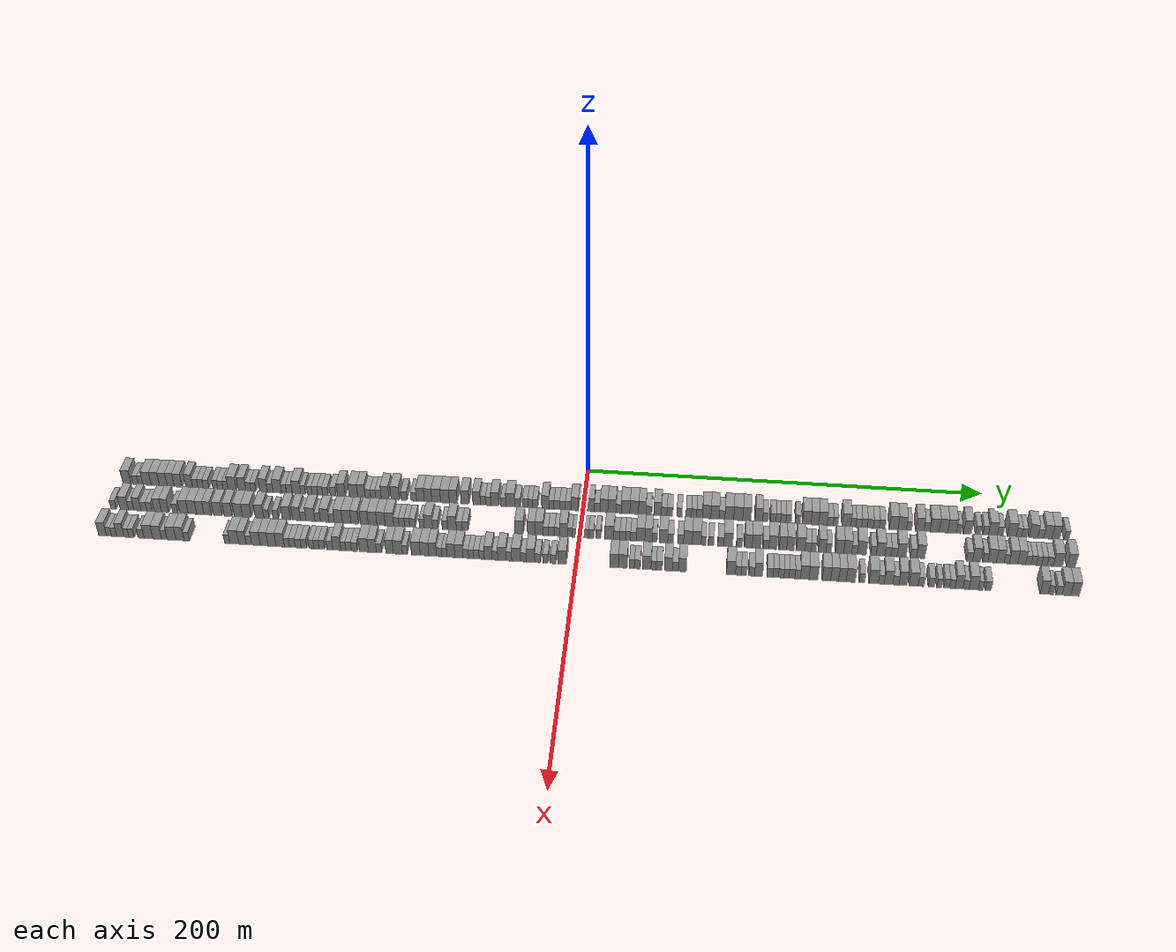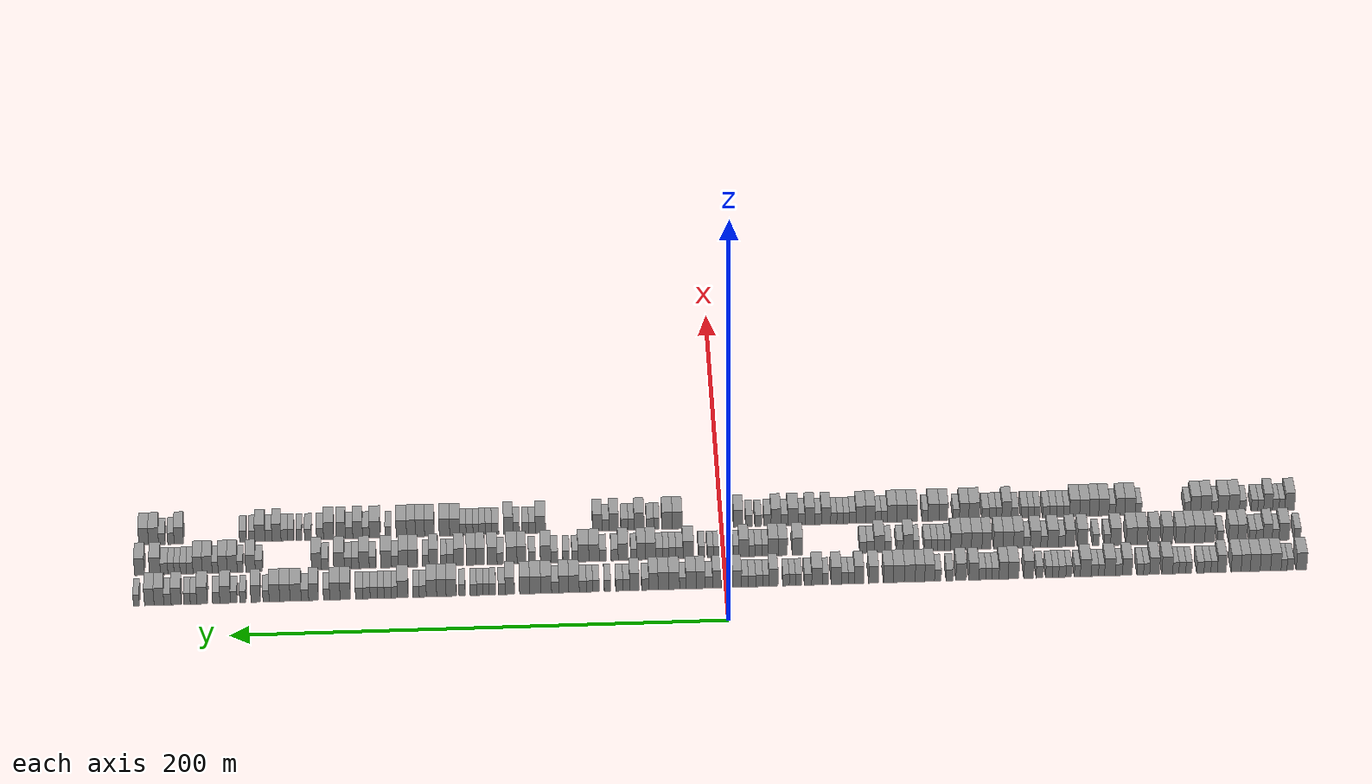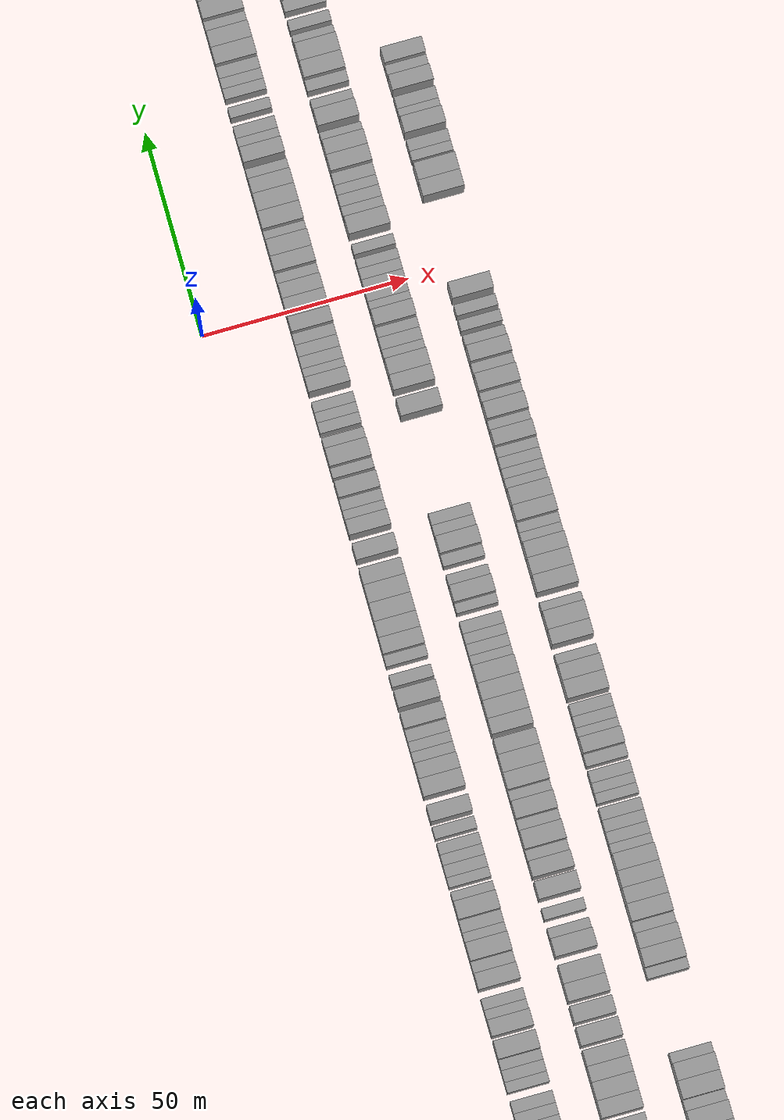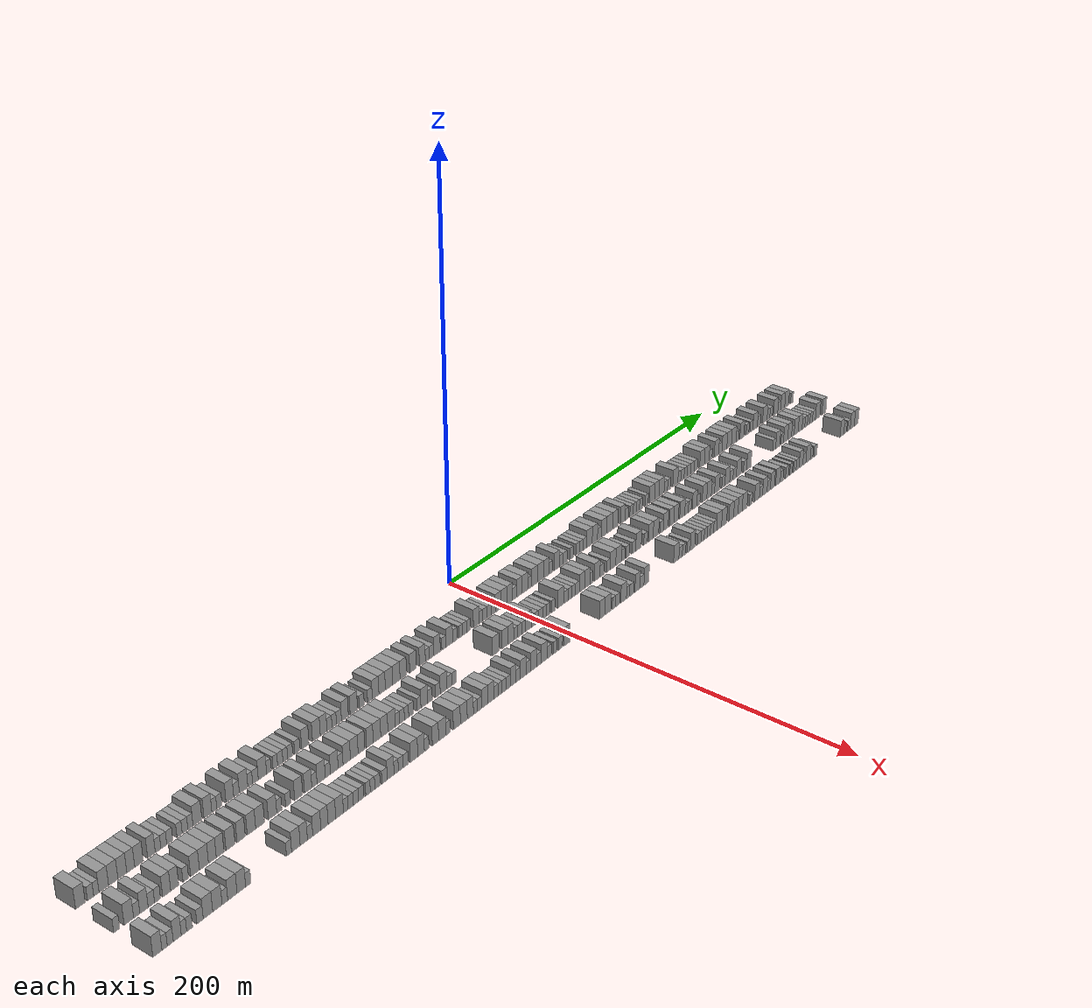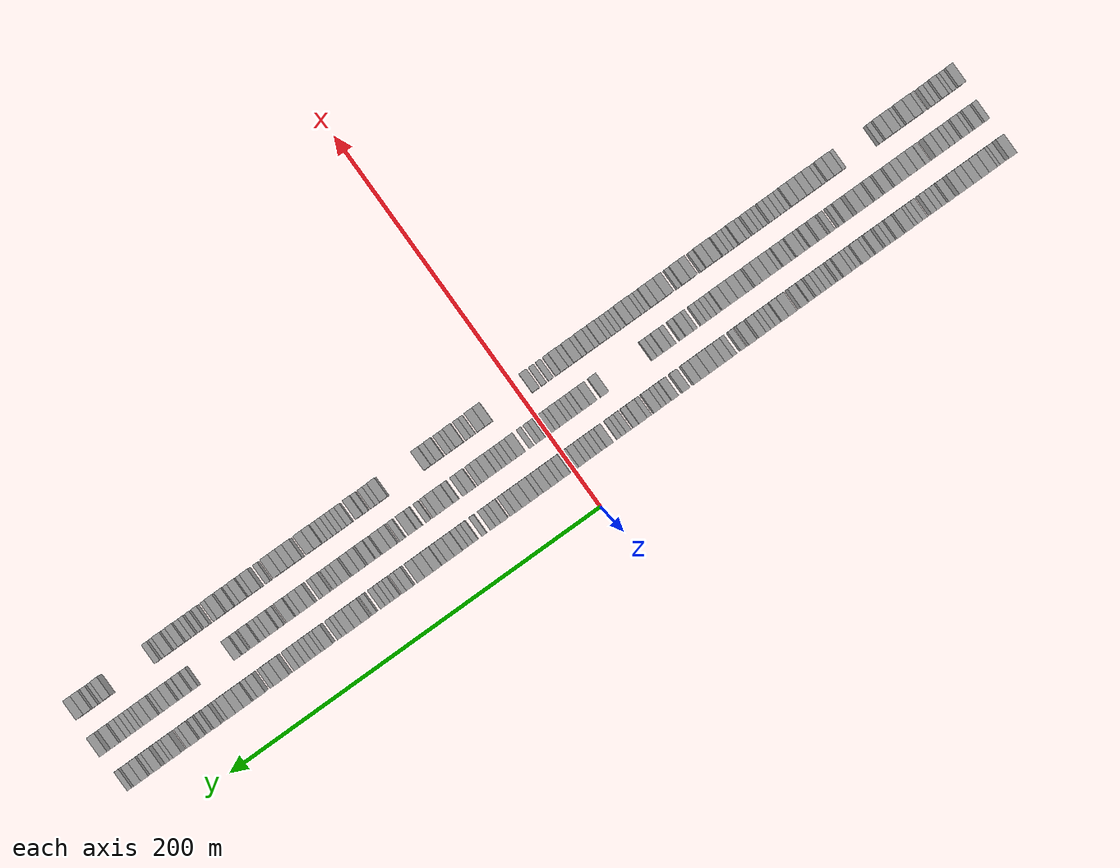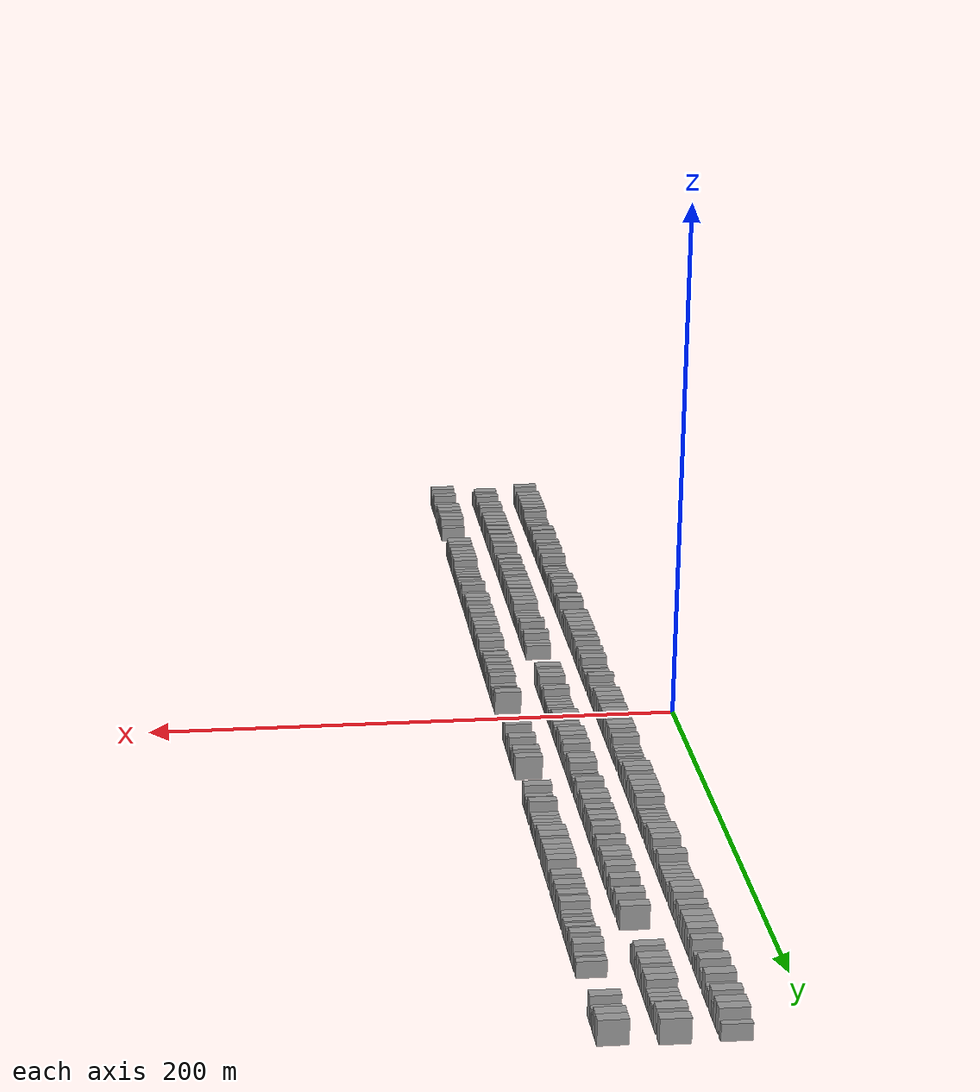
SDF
<sdf version="1.6">
 <world name="default">
  <scene>
   <sky><clouds><speed>12</speed></clouds></sky>
   <ambient>0.4 0.4 0.4 1</ambient>
   <background>0.7 0.7 0.7 1</background>
   <shadows>1</shadows>
  </scene>
  <gravity>0 0 -9.8066</gravity>
  <magnetic_field>6e-06 2.3e-05 -4.2e-05</magnetic_field>
  <physics default="0" name="default_physics" type="ode">
   <ode>
    <solver>
     <type>quick</type>
     <iters>10</iters>
     <sor>1.0</sor>
     <use_dynamic_moi_rescaling>0</use_dynamic_moi_rescaling>
    </solver>
    <constraints>
     <cfm>0</cfm>
     <erp>0.2</erp>
     <contact_max_correcting_vel>100</contact_max_correcting_vel>
     <contact_surface_layer>0.001</contact_surface_layer>
    </constraints>
   </ode>
   <max_step_size>0.004</max_step_size>
   <real_time_factor>1</real_time_factor>
   <real_time_update_rate>250</real_time_update_rate>
  </physics>
  <light name="sun" type="directional">
   <pose>0 0 10 0 0 0</pose>
   <diffuse>0.8 0.8 0.8 1</diffuse>
   <specular>0.2 0.2 0.2 1</specular>
   <attenuation>
    <range>1000</range>
    <constant>0.9</constant>
    <linear>0.01</linear>
    <quadratic>0.001</quadratic>
   </attenuation>
   <direction>-0.5 0.1 -0.9</direction>
  </light>
  <model name="building_1">
   <static>1</static>
   <pose>25.0000 -233.8589 0 0.000000 0.000000 0.000000</pose>
   <link name="link">
    <pose>0 0 4.50 0 0 0</pose>
    <collision name="collision"><geometry><box><size>10.0000 4.2823 9.0000</size></box></geometry></collision>
    <visual name="visual">
     <cast_shadows>0</cast_shadows>
     <geometry><box><size>10.0000 4.2823 9.0000</size></box></geometry>
     <material>
      <script>
       <uri>model://grey_wall/materials/scripts</uri>
       <uri>model://grey_wall/materials/textures</uri>
       <name>vrc/grey_wall</name>
      </script>
     </material>
    </visual>
   </link>
  </model>
  <model name="building_2">
   <static>1</static>
   <pose>25.0000 -229.3313 0 0.000000 0.000000 0.000000</pose>
   <link name="link">
    <pose>0 0 3.00 0 0 0</pose>
    <collision name="collision"><geometry><box><size>10.0000 2.7728 6.0000</size></box></geometry></collision>
    <visual name="visual">
     <cast_shadows>0</cast_shadows>
     <geometry><box><size>10.0000 2.7728 6.0000</size></box></geometry>
     <material>
      <script>
       <uri>model://grey_wall/materials/scripts</uri>
       <uri>model://grey_wall/materials/textures</uri>
       <name>vrc/grey_wall</name>
      </script>
     </material>
    </visual>
   </link>
  </model>
  <model name="building_3">
   <static>1</static>
   <pose>25.0000 -226.7436 0 0.000000 0.000000 0.000000</pose>
   <link name="link">
    <pose>0 0 3.00 0 0 0</pose>
    <collision name="collision"><geometry><box><size>10.0000 2.4027 6.0000</size></box></geometry></collision>
    <visual name="visual">
     <cast_shadows>0</cast_shadows>
     <geometry><box><size>10.0000 2.4027 6.0000</size></box></geometry>
     <material>
      <script>
       <uri>model://grey_wall/materials/scripts</uri>
       <uri>model://grey_wall/materials/textures</uri>
       <name>vrc/grey_wall</name>
      </script>
     </material>
    </visual>
   </link>
  </model>
  <model name="building_4">
   <static>1</static>
   <pose>25.0000 -223.3884 0 0.000000 0.000000 0.000000</pose>
   <link name="link">
    <pose>0 0 4.50 0 0 0</pose>
    <collision name="collision"><geometry><box><size>10.0000 4.3077 9.0000</size></box></geometry></collision>
    <visual name="visual">
     <cast_shadows>0</cast_shadows>
     <geometry><box><size>10.0000 4.3077 9.0000</size></box></geometry>
     <material>
      <script>
       <uri>model://grey_wall/materials/scripts</uri>
       <uri>model://grey_wall/materials/textures</uri>
       <name>vrc/grey_wall</name>
      </script>
     </material>
    </visual>
   </link>
  </model>
  <model name="building_5">
   <static>1</static>
   <pose>25.0000 -219.1141 0 0.000000 0.000000 0.000000</pose>
   <link name="link">
    <pose>0 0 4.50 0 0 0</pose>
    <collision name="collision"><geometry><box><size>10.0000 4.2409 9.0000</size></box></geometry></collision>
    <visual name="visual">
     <cast_shadows>0</cast_shadows>
     <geometry><box><size>10.0000 4.2409 9.0000</size></box></geometry>
     <material>
      <script>
       <uri>model://grey_wall/materials/scripts</uri>
       <uri>model://grey_wall/materials/textures</uri>
       <name>vrc/grey_wall</name>
      </script>
     </material>
    </visual>
   </link>
  </model>
  <model name="building_6">
   <static>1</static>
   <pose>25.0000 -214.9494 0 0.000000 0.000000 0.000000</pose>
   <link name="link">
    <pose>0 0 4.50 0 0 0</pose>
    <collision name="collision"><geometry><box><size>10.0000 4.0884 9.0000</size></box></geometry></collision>
    <visual name="visual">
     <cast_shadows>0</cast_shadows>
     <geometry><box><size>10.0000 4.0884 9.0000</size></box></geometry>
     <material>
      <script>
       <uri>model://grey_wall/materials/scripts</uri>
       <uri>model://grey_wall/materials/textures</uri>
       <name>vrc/grey_wall</name>
      </script>
     </material>
    </visual>
   </link>
  </model>
  <model name="building_7">
   <static>1</static>
   <pose>25.0000 -211.0635 0 0.000000 0.000000 0.000000</pose>
   <link name="link">
    <pose>0 0 4.50 0 0 0</pose>
    <collision name="collision"><geometry><box><size>10.0000 3.6835 9.0000</size></box></geometry></collision>
    <visual name="visual">
     <cast_shadows>0</cast_shadows>
     <geometry><box><size>10.0000 3.6835 9.0000</size></box></geometry>
     <material>
      <script>
       <uri>model://grey_wall/materials/scripts</uri>
       <uri>model://grey_wall/materials/textures</uri>
       <name>vrc/grey_wall</name>
      </script>
     </material>
    </visual>
   </link>
  </model>
  <model name="building_8">
   <static>1</static>
   <pose>25.0000 -207.2056 0 0.000000 0.000000 0.000000</pose>
   <link name="link">
    <pose>0 0 4.50 0 0 0</pose>
    <collision name="collision"><geometry><box><size>10.0000 4.0324 9.0000</size></box></geometry></collision>
    <visual name="visual">
     <cast_shadows>0</cast_shadows>
     <geometry><box><size>10.0000 4.0324 9.0000</size></box></geometry>
     <material>
      <script>
       <uri>model://grey_wall/materials/scripts</uri>
       <uri>model://grey_wall/materials/textures</uri>
       <name>vrc/grey_wall</name>
      </script>
     </material>
    </visual>
   </link>
  </model>
  <model name="building_9">
   <static>1</static>
   <pose>25.0000 -201.3807 0 0.000000 0.000000 0.000000</pose>
   <link name="link">
    <pose>0 0 4.50 0 0 0</pose>
    <collision name="collision"><geometry><box><size>10.0000 3.6173 9.0000</size></box></geometry></collision>
    <visual name="visual">
     <cast_shadows>0</cast_shadows>
     <geometry><box><size>10.0000 3.6173 9.0000</size></box></geometry>
     <material>
      <script>
       <uri>model://grey_wall/materials/scripts</uri>
       <uri>model://grey_wall/materials/textures</uri>
       <name>vrc/grey_wall</name>
      </script>
     </material>
    </visual>
   </link>
  </model>
  <model name="building_10">
   <static>1</static>
   <pose>25.0000 -198.2366 0 0.000000 0.000000 0.000000</pose>
   <link name="link">
    <pose>0 0 3.00 0 0 0</pose>
    <collision name="collision"><geometry><box><size>10.0000 2.6708 6.0000</size></box></geometry></collision>
    <visual name="visual">
     <cast_shadows>0</cast_shadows>
     <geometry><box><size>10.0000 2.6708 6.0000</size></box></geometry>
     <material>
      <script>
       <uri>model://grey_wall/materials/scripts</uri>
       <uri>model://grey_wall/materials/textures</uri>
       <name>vrc/grey_wall</name>
      </script>
     </material>
    </visual>
   </link>
  </model>
  <model name="building_11">
   <static>1</static>
   <pose>25.0000 -195.4978 0 0.000000 0.000000 0.000000</pose>
   <link name="link">
    <pose>0 0 3.00 0 0 0</pose>
    <collision name="collision"><geometry><box><size>10.0000 2.8070 6.0000</size></box></geometry></collision>
    <visual name="visual">
     <cast_shadows>0</cast_shadows>
     <geometry><box><size>10.0000 2.8070 6.0000</size></box></geometry>
     <material>
      <script>
       <uri>model://grey_wall/materials/scripts</uri>
       <uri>model://grey_wall/materials/textures</uri>
       <name>vrc/grey_wall</name>
      </script>
     </material>
    </visual>
   </link>
  </model>
  <model name="building_12">
   <static>1</static>
   <pose>25.0000 -192.6402 0 0.000000 0.000000 0.000000</pose>
   <link name="link">
    <pose>0 0 3.00 0 0 0</pose>
    <collision name="collision"><geometry><box><size>10.0000 2.9082 6.0000</size></box></geometry></collision>
    <visual name="visual">
     <cast_shadows>0</cast_shadows>
     <geometry><box><size>10.0000 2.9082 6.0000</size></box></geometry>
     <material>
      <script>
       <uri>model://grey_wall/materials/scripts</uri>
       <uri>model://grey_wall/materials/textures</uri>
       <name>vrc/grey_wall</name>
      </script>
     </material>
    </visual>
   </link>
  </model>
  <model name="building_13">
   <static>1</static>
   <pose>25.0000 -187.9117 0 0.000000 0.000000 0.000000</pose>
   <link name="link">
    <pose>0 0 3.00 0 0 0</pose>
    <collision name="collision"><geometry><box><size>10.0000 2.5488 6.0000</size></box></geometry></collision>
    <visual name="visual">
     <cast_shadows>0</cast_shadows>
     <geometry><box><size>10.0000 2.5488 6.0000</size></box></geometry>
     <material>
      <script>
       <uri>model://grey_wall/materials/scripts</uri>
       <uri>model://grey_wall/materials/textures</uri>
       <name>vrc/grey_wall</name>
      </script>
     </material>
    </visual>
   </link>
  </model>
  <model name="building_14">
   <static>1</static>
   <pose>25.0000 -185.2370 0 0.000000 0.000000 0.000000</pose>
   <link name="link">
    <pose>0 0 3.00 0 0 0</pose>
    <collision name="collision"><geometry><box><size>10.0000 2.8006 6.0000</size></box></geometry></collision>
    <visual name="visual">
     <cast_shadows>0</cast_shadows>
     <geometry><box><size>10.0000 2.8006 6.0000</size></box></geometry>
     <material>
      <script>
       <uri>model://grey_wall/materials/scripts</uri>
       <uri>model://grey_wall/materials/textures</uri>
       <name>vrc/grey_wall</name>
      </script>
     </material>
    </visual>
   </link>
  </model>
  <model name="building_15">
   <static>1</static>
   <pose>25.0000 -182.5791 0 0.000000 0.000000 0.000000</pose>
   <link name="link">
    <pose>0 0 3.00 0 0 0</pose>
    <collision name="collision"><geometry><box><size>10.0000 2.5152 6.0000</size></box></geometry></collision>
    <visual name="visual">
     <cast_shadows>0</cast_shadows>
     <geometry><box><size>10.0000 2.5152 6.0000</size></box></geometry>
     <material>
      <script>
       <uri>model://grey_wall/materials/scripts</uri>
       <uri>model://grey_wall/materials/textures</uri>
       <name>vrc/grey_wall</name>
      </script>
     </material>
    </visual>
   </link>
  </model>
  <model name="building_16">
   <static>1</static>
   <pose>25.0000 -179.1273 0 0.000000 0.000000 0.000000</pose>
   <link name="link">
    <pose>0 0 4.50 0 0 0</pose>
    <collision name="collision"><geometry><box><size>10.0000 4.3885 9.0000</size></box></geometry></collision>
    <visual name="visual">
     <cast_shadows>0</cast_shadows>
     <geometry><box><size>10.0000 4.3885 9.0000</size></box></geometry>
     <material>
      <script>
       <uri>model://grey_wall/materials/scripts</uri>
       <uri>model://grey_wall/materials/textures</uri>
       <name>vrc/grey_wall</name>
      </script>
     </material>
    </visual>
   </link>
  </model>
  <model name="building_17">
   <static>1</static>
   <pose>25.0000 -173.9559 0 0.000000 0.000000 0.000000</pose>
   <link name="link">
    <pose>0 0 4.50 0 0 0</pose>
    <collision name="collision"><geometry><box><size>10.0000 3.9544 9.0000</size></box></geometry></collision>
    <visual name="visual">
     <cast_shadows>0</cast_shadows>
     <geometry><box><size>10.0000 3.9544 9.0000</size></box></geometry>
     <material>
      <script>
       <uri>model://grey_wall/materials/scripts</uri>
       <uri>model://grey_wall/materials/textures</uri>
       <name>vrc/grey_wall</name>
      </script>
     </material>
    </visual>
   </link>
  </model>
  <model name="building_18">
   <static>1</static>
   <pose>25.0000 -170.7183 0 0.000000 0.000000 0.000000</pose>
   <link name="link">
    <pose>0 0 3.00 0 0 0</pose>
    <collision name="collision"><geometry><box><size>10.0000 2.5207 6.0000</size></box></geometry></collision>
    <visual name="visual">
     <cast_shadows>0</cast_shadows>
     <geometry><box><size>10.0000 2.5207 6.0000</size></box></geometry>
     <material>
      <script>
       <uri>model://grey_wall/materials/scripts</uri>
       <uri>model://grey_wall/materials/textures</uri>
       <name>vrc/grey_wall</name>
      </script>
     </material>
    </visual>
   </link>
  </model>
  <model name="building_19">
   <static>1</static>
   <pose>25.0000 -168.1359 0 0.000000 0.000000 0.000000</pose>
   <link name="link">
    <pose>0 0 3.00 0 0 0</pose>
    <collision name="collision"><geometry><box><size>10.0000 2.6441 6.0000</size></box></geometry></collision>
    <visual name="visual">
     <cast_shadows>0</cast_shadows>
     <geometry><box><size>10.0000 2.6441 6.0000</size></box></geometry>
     <material>
      <script>
       <uri>model://grey_wall/materials/scripts</uri>
       <uri>model://grey_wall/materials/textures</uri>
       <name>vrc/grey_wall</name>
      </script>
     </material>
    </visual>
   </link>
  </model>
  <model name="building_20">
   <static>1</static>
   <pose>25.0000 -162.8508 0 0.000000 0.000000 0.000000</pose>
   <link name="link">
    <pose>0 0 4.50 0 0 0</pose>
    <collision name="collision"><geometry><box><size>10.0000 3.9261 9.0000</size></box></geometry></collision>
    <visual name="visual">
     <cast_shadows>0</cast_shadows>
     <geometry><box><size>10.0000 3.9261 9.0000</size></box></geometry>
     <material>
      <script>
       <uri>model://grey_wall/materials/scripts</uri>
       <uri>model://grey_wall/materials/textures</uri>
       <name>vrc/grey_wall</name>
      </script>
     </material>
    </visual>
   </link>
  </model>
  <model name="building_21">
   <static>1</static>
   <pose>25.0000 -159.4385 0 0.000000 0.000000 0.000000</pose>
   <link name="link">
    <pose>0 0 3.00 0 0 0</pose>
    <collision name="collision"><geometry><box><size>10.0000 2.8985 6.0000</size></box></geometry></collision>
    <visual name="visual">
     <cast_shadows>0</cast_shadows>
     <geometry><box><size>10.0000 2.8985 6.0000</size></box></geometry>
     <material>
      <script>
       <uri>model://grey_wall/materials/scripts</uri>
       <uri>model://grey_wall/materials/textures</uri>
       <name>vrc/grey_wall</name>
      </script>
     </material>
    </visual>
   </link>
  </model>
  <model name="building_22">
   <static>1</static>
   <pose>25.0000 -155.7770 0 0.000000 0.000000 0.000000</pose>
   <link name="link">
    <pose>0 0 4.50 0 0 0</pose>
    <collision name="collision"><geometry><box><size>10.0000 4.4245 9.0000</size></box></geometry></collision>
    <visual name="visual">
     <cast_shadows>0</cast_shadows>
     <geometry><box><size>10.0000 4.4245 9.0000</size></box></geometry>
     <material>
      <script>
       <uri>model://grey_wall/materials/scripts</uri>
       <uri>model://grey_wall/materials/textures</uri>
       <name>vrc/grey_wall</name>
      </script>
     </material>
    </visual>
   </link>
  </model>
  <model name="building_23">
   <static>1</static>
   <pose>25.0000 -152.3275 0 0.000000 0.000000 0.000000</pose>
   <link name="link">
    <pose>0 0 3.00 0 0 0</pose>
    <collision name="collision"><geometry><box><size>10.0000 2.4743 6.0000</size></box></geometry></collision>
    <visual name="visual">
     <cast_shadows>0</cast_shadows>
     <geometry><box><size>10.0000 2.4743 6.0000</size></box></geometry>
     <material>
      <script>
       <uri>model://grey_wall/materials/scripts</uri>
       <uri>model://grey_wall/materials/textures</uri>
       <name>vrc/grey_wall</name>
      </script>
     </material>
    </visual>
   </link>
  </model>
  <model name="building_24">
   <static>1</static>
   <pose>25.0000 -149.5923 0 0.000000 0.000000 0.000000</pose>
   <link name="link">
    <pose>0 0 3.00 0 0 0</pose>
    <collision name="collision"><geometry><box><size>10.0000 2.9961 6.0000</size></box></geometry></collision>
    <visual name="visual">
     <cast_shadows>0</cast_shadows>
     <geometry><box><size>10.0000 2.9961 6.0000</size></box></geometry>
     <material>
      <script>
       <uri>model://grey_wall/materials/scripts</uri>
       <uri>model://grey_wall/materials/textures</uri>
       <name>vrc/grey_wall</name>
      </script>
     </material>
    </visual>
   </link>
  </model>
  <model name="building_25">
   <static>1</static>
   <pose>25.0000 -145.9034 0 0.000000 0.000000 0.000000</pose>
   <link name="link">
    <pose>0 0 4.50 0 0 0</pose>
    <collision name="collision"><geometry><box><size>10.0000 4.3817 9.0000</size></box></geometry></collision>
    <visual name="visual">
     <cast_shadows>0</cast_shadows>
     <geometry><box><size>10.0000 4.3817 9.0000</size></box></geometry>
     <material>
      <script>
       <uri>model://grey_wall/materials/scripts</uri>
       <uri>model://grey_wall/materials/textures</uri>
       <name>vrc/grey_wall</name>
      </script>
     </material>
    </visual>
   </link>
  </model>
  <model name="building_26">
   <static>1</static>
   <pose>25.0000 -142.4988 0 0.000000 0.000000 0.000000</pose>
   <link name="link">
    <pose>0 0 3.00 0 0 0</pose>
    <collision name="collision"><geometry><box><size>10.0000 2.4275 6.0000</size></box></geometry></collision>
    <visual name="visual">
     <cast_shadows>0</cast_shadows>
     <geometry><box><size>10.0000 2.4275 6.0000</size></box></geometry>
     <material>
      <script>
       <uri>model://grey_wall/materials/scripts</uri>
       <uri>model://grey_wall/materials/textures</uri>
       <name>vrc/grey_wall</name>
      </script>
     </material>
    </visual>
   </link>
  </model>
  <model name="building_27">
   <static>1</static>
   <pose>25.0000 -139.0678 0 0.000000 0.000000 0.000000</pose>
   <link name="link">
    <pose>0 0 3.00 0 0 0</pose>
    <collision name="collision"><geometry><box><size>10.0000 2.4345 6.0000</size></box></geometry></collision>
    <visual name="visual">
     <cast_shadows>0</cast_shadows>
     <geometry><box><size>10.0000 2.4345 6.0000</size></box></geometry>
     <material>
      <script>
       <uri>model://grey_wall/materials/scripts</uri>
       <uri>model://grey_wall/materials/textures</uri>
       <name>vrc/grey_wall</name>
      </script>
     </material>
    </visual>
   </link>
  </model>
  <model name="building_28">
   <static>1</static>
   <pose>25.0000 -136.3945 0 0.000000 0.000000 0.000000</pose>
   <link name="link">
    <pose>0 0 3.00 0 0 0</pose>
    <collision name="collision"><geometry><box><size>10.0000 2.9121 6.0000</size></box></geometry></collision>
    <visual name="visual">
     <cast_shadows>0</cast_shadows>
     <geometry><box><size>10.0000 2.9121 6.0000</size></box></geometry>
     <material>
      <script>
       <uri>model://grey_wall/materials/scripts</uri>
       <uri>model://grey_wall/materials/textures</uri>
       <name>vrc/grey_wall</name>
      </script>
     </material>
    </visual>
   </link>
  </model>
  <model name="building_29">
   <static>1</static>
   <pose>25.0000 -133.6613 0 0.000000 0.000000 0.000000</pose>
   <link name="link">
    <pose>0 0 3.00 0 0 0</pose>
    <collision name="collision"><geometry><box><size>10.0000 2.5542 6.0000</size></box></geometry></collision>
    <visual name="visual">
     <cast_shadows>0</cast_shadows>
     <geometry><box><size>10.0000 2.5542 6.0000</size></box></geometry>
     <material>
      <script>
       <uri>model://grey_wall/materials/scripts</uri>
       <uri>model://grey_wall/materials/textures</uri>
       <name>vrc/grey_wall</name>
      </script>
     </material>
    </visual>
   </link>
  </model>
  <model name="building_30">
   <static>1</static>
   <pose>25.0000 -131.0074 0 0.000000 0.000000 0.000000</pose>
   <link name="link">
    <pose>0 0 3.00 0 0 0</pose>
    <collision name="collision"><geometry><box><size>10.0000 2.7537 6.0000</size></box></geometry></collision>
    <visual name="visual">
     <cast_shadows>0</cast_shadows>
     <geometry><box><size>10.0000 2.7537 6.0000</size></box></geometry>
     <material>
      <script>
       <uri>model://grey_wall/materials/scripts</uri>
       <uri>model://grey_wall/materials/textures</uri>
       <name>vrc/grey_wall</name>
      </script>
     </material>
    </visual>
   </link>
  </model>
  <model name="building_31">
   <static>1</static>
   <pose>25.0000 -127.1895 0 0.000000 0.000000 0.000000</pose>
   <link name="link">
    <pose>0 0 3.00 0 0 0</pose>
    <collision name="collision"><geometry><box><size>10.0000 2.8820 6.0000</size></box></geometry></collision>
    <visual name="visual">
     <cast_shadows>0</cast_shadows>
     <geometry><box><size>10.0000 2.8820 6.0000</size></box></geometry>
     <material>
      <script>
       <uri>model://grey_wall/materials/scripts</uri>
       <uri>model://grey_wall/materials/textures</uri>
       <name>vrc/grey_wall</name>
      </script>
     </material>
    </visual>
   </link>
  </model>
  <model name="building_32">
   <static>1</static>
   <pose>25.0000 -122.7616 0 0.000000 0.000000 0.000000</pose>
   <link name="link">
    <pose>0 0 4.50 0 0 0</pose>
    <collision name="collision"><geometry><box><size>10.0000 3.9737 9.0000</size></box></geometry></collision>
    <visual name="visual">
     <cast_shadows>0</cast_shadows>
     <geometry><box><size>10.0000 3.9737 9.0000</size></box></geometry>
     <material>
      <script>
       <uri>model://grey_wall/materials/scripts</uri>
       <uri>model://grey_wall/materials/textures</uri>
       <name>vrc/grey_wall</name>
      </script>
     </material>
    </visual>
   </link>
  </model>
  <model name="building_33">
   <static>1</static>
   <pose>25.0000 -116.5971 0 0.000000 0.000000 0.000000</pose>
   <link name="link">
    <pose>0 0 4.50 0 0 0</pose>
    <collision name="collision"><geometry><box><size>10.0000 4.3553 9.0000</size></box></geometry></collision>
    <visual name="visual">
     <cast_shadows>0</cast_shadows>
     <geometry><box><size>10.0000 4.3553 9.0000</size></box></geometry>
     <material>
      <script>
       <uri>model://grey_wall/materials/scripts</uri>
       <uri>model://grey_wall/materials/textures</uri>
       <name>vrc/grey_wall</name>
      </script>
     </material>
    </visual>
   </link>
  </model>
  <model name="building_34">
   <static>1</static>
   <pose>25.0000 -112.5437 0 0.000000 0.000000 0.000000</pose>
   <link name="link">
    <pose>0 0 4.50 0 0 0</pose>
    <collision name="collision"><geometry><box><size>10.0000 3.7516 9.0000</size></box></geometry></collision>
    <visual name="visual">
     <cast_shadows>0</cast_shadows>
     <geometry><box><size>10.0000 3.7516 9.0000</size></box></geometry>
     <material>
      <script>
       <uri>model://grey_wall/materials/scripts</uri>
       <uri>model://grey_wall/materials/textures</uri>
       <name>vrc/grey_wall</name>
      </script>
     </material>
    </visual>
   </link>
  </model>
  <model name="building_35">
   <static>1</static>
   <pose>25.0000 -109.2309 0 0.000000 0.000000 0.000000</pose>
   <link name="link">
    <pose>0 0 3.00 0 0 0</pose>
    <collision name="collision"><geometry><box><size>10.0000 2.8741 6.0000</size></box></geometry></collision>
    <visual name="visual">
     <cast_shadows>0</cast_shadows>
     <geometry><box><size>10.0000 2.8741 6.0000</size></box></geometry>
     <material>
      <script>
       <uri>model://grey_wall/materials/scripts</uri>
       <uri>model://grey_wall/materials/textures</uri>
       <name>vrc/grey_wall</name>
      </script>
     </material>
    </visual>
   </link>
  </model>
  <model name="building_36">
   <static>1</static>
   <pose>25.0000 -106.5407 0 0.000000 0.000000 0.000000</pose>
   <link name="link">
    <pose>0 0 3.00 0 0 0</pose>
    <collision name="collision"><geometry><box><size>10.0000 2.5064 6.0000</size></box></geometry></collision>
    <visual name="visual">
     <cast_shadows>0</cast_shadows>
     <geometry><box><size>10.0000 2.5064 6.0000</size></box></geometry>
     <material>
      <script>
       <uri>model://grey_wall/materials/scripts</uri>
       <uri>model://grey_wall/materials/textures</uri>
       <name>vrc/grey_wall</name>
      </script>
     </material>
    </visual>
   </link>
  </model>
  <model name="building_37">
   <static>1</static>
   <pose>25.0000 -103.8382 0 0.000000 0.000000 0.000000</pose>
   <link name="link">
    <pose>0 0 3.00 0 0 0</pose>
    <collision name="collision"><geometry><box><size>10.0000 2.8986 6.0000</size></box></geometry></collision>
    <visual name="visual">
     <cast_shadows>0</cast_shadows>
     <geometry><box><size>10.0000 2.8986 6.0000</size></box></geometry>
     <material>
      <script>
       <uri>model://grey_wall/materials/scripts</uri>
       <uri>model://grey_wall/materials/textures</uri>
       <name>vrc/grey_wall</name>
      </script>
     </material>
    </visual>
   </link>
  </model>
  <model name="building_38">
   <static>1</static>
   <pose>25.0000 -100.4034 0 0.000000 0.000000 0.000000</pose>
   <link name="link">
    <pose>0 0 4.50 0 0 0</pose>
    <collision name="collision"><geometry><box><size>10.0000 3.9711 9.0000</size></box></geometry></collision>
    <visual name="visual">
     <cast_shadows>0</cast_shadows>
     <geometry><box><size>10.0000 3.9711 9.0000</size></box></geometry>
     <material>
      <script>
       <uri>model://grey_wall/materials/scripts</uri>
       <uri>model://grey_wall/materials/textures</uri>
       <name>vrc/grey_wall</name>
      </script>
     </material>
    </visual>
   </link>
  </model>
  <model name="building_39">
   <static>1</static>
   <pose>25.0000 -95.2755 0 0.000000 0.000000 0.000000</pose>
   <link name="link">
    <pose>0 0 4.50 0 0 0</pose>
    <collision name="collision"><geometry><box><size>10.0000 4.2846 9.0000</size></box></geometry></collision>
    <visual name="visual">
     <cast_shadows>0</cast_shadows>
     <geometry><box><size>10.0000 4.2846 9.0000</size></box></geometry>
     <material>
      <script>
       <uri>model://grey_wall/materials/scripts</uri>
       <uri>model://grey_wall/materials/textures</uri>
       <name>vrc/grey_wall</name>
      </script>
     </material>
    </visual>
   </link>
  </model>
  <model name="building_40">
   <static>1</static>
   <pose>25.0000 -90.6604 0 0.000000 0.000000 0.000000</pose>
   <link name="link">
    <pose>0 0 3.00 0 0 0</pose>
    <collision name="collision"><geometry><box><size>10.0000 2.9457 6.0000</size></box></geometry></collision>
    <visual name="visual">
     <cast_shadows>0</cast_shadows>
     <geometry><box><size>10.0000 2.9457 6.0000</size></box></geometry>
     <material>
      <script>
       <uri>model://grey_wall/materials/scripts</uri>
       <uri>model://grey_wall/materials/textures</uri>
       <name>vrc/grey_wall</name>
      </script>
     </material>
    </visual>
   </link>
  </model>
  <model name="building_41">
   <static>1</static>
   <pose>25.0000 -85.8141 0 0.000000 0.000000 0.000000</pose>
   <link name="link">
    <pose>0 0 3.00 0 0 0</pose>
    <collision name="collision"><geometry><box><size>10.0000 2.7468 6.0000</size></box></geometry></collision>
    <visual name="visual">
     <cast_shadows>0</cast_shadows>
     <geometry><box><size>10.0000 2.7468 6.0000</size></box></geometry>
     <material>
      <script>
       <uri>model://grey_wall/materials/scripts</uri>
       <uri>model://grey_wall/materials/textures</uri>
       <name>vrc/grey_wall</name>
      </script>
     </material>
    </visual>
   </link>
  </model>
  <model name="building_42">
   <static>1</static>
   <pose>25.0000 -82.4574 0 0.000000 0.000000 0.000000</pose>
   <link name="link">
    <pose>0 0 4.50 0 0 0</pose>
    <collision name="collision"><geometry><box><size>10.0000 3.9666 9.0000</size></box></geometry></collision>
    <visual name="visual">
     <cast_shadows>0</cast_shadows>
     <geometry><box><size>10.0000 3.9666 9.0000</size></box></geometry>
     <material>
      <script>
       <uri>model://grey_wall/materials/scripts</uri>
       <uri>model://grey_wall/materials/textures</uri>
       <name>vrc/grey_wall</name>
      </script>
     </material>
    </visual>
   </link>
  </model>
  <model name="building_43">
   <static>1</static>
   <pose>25.0000 -78.5369 0 0.000000 0.000000 0.000000</pose>
   <link name="link">
    <pose>0 0 4.50 0 0 0</pose>
    <collision name="collision"><geometry><box><size>10.0000 3.8744 9.0000</size></box></geometry></collision>
    <visual name="visual">
     <cast_shadows>0</cast_shadows>
     <geometry><box><size>10.0000 3.8744 9.0000</size></box></geometry>
     <material>
      <script>
       <uri>model://grey_wall/materials/scripts</uri>
       <uri>model://grey_wall/materials/textures</uri>
       <name>vrc/grey_wall</name>
      </script>
     </material>
    </visual>
   </link>
  </model>
  <model name="building_44">
   <static>1</static>
   <pose>25.0000 -74.3791 0 0.000000 0.000000 0.000000</pose>
   <link name="link">
    <pose>0 0 4.50 0 0 0</pose>
    <collision name="collision"><geometry><box><size>10.0000 4.4412 9.0000</size></box></geometry></collision>
    <visual name="visual">
     <cast_shadows>0</cast_shadows>
     <geometry><box><size>10.0000 4.4412 9.0000</size></box></geometry>
     <material>
      <script>
       <uri>model://grey_wall/materials/scripts</uri>
       <uri>model://grey_wall/materials/textures</uri>
       <name>vrc/grey_wall</name>
      </script>
     </material>
    </visual>
   </link>
  </model>
  <model name="building_45">
   <static>1</static>
   <pose>25.0000 -69.9395 0 0.000000 0.000000 0.000000</pose>
   <link name="link">
    <pose>0 0 4.50 0 0 0</pose>
    <collision name="collision"><geometry><box><size>10.0000 4.4379 9.0000</size></box></geometry></collision>
    <visual name="visual">
     <cast_shadows>0</cast_shadows>
     <geometry><box><size>10.0000 4.4379 9.0000</size></box></geometry>
     <material>
      <script>
       <uri>model://grey_wall/materials/scripts</uri>
       <uri>model://grey_wall/materials/textures</uri>
       <name>vrc/grey_wall</name>
      </script>
     </material>
    </visual>
   </link>
  </model>
  <model name="building_46">
   <static>1</static>
   <pose>25.0000 -65.7324 0 0.000000 0.000000 0.000000</pose>
   <link name="link">
    <pose>0 0 4.50 0 0 0</pose>
    <collision name="collision"><geometry><box><size>10.0000 3.9764 9.0000</size></box></geometry></collision>
    <visual name="visual">
     <cast_shadows>0</cast_shadows>
     <geometry><box><size>10.0000 3.9764 9.0000</size></box></geometry>
     <material>
      <script>
       <uri>model://grey_wall/materials/scripts</uri>
       <uri>model://grey_wall/materials/textures</uri>
       <name>vrc/grey_wall</name>
      </script>
     </material>
    </visual>
   </link>
  </model>
  <model name="building_47">
   <static>1</static>
   <pose>25.0000 -59.7386 0 0.000000 0.000000 0.000000</pose>
   <link name="link">
    <pose>0 0 4.50 0 0 0</pose>
    <collision name="collision"><geometry><box><size>10.0000 4.0110 9.0000</size></box></geometry></collision>
    <visual name="visual">
     <cast_shadows>0</cast_shadows>
     <geometry><box><size>10.0000 4.0110 9.0000</size></box></geometry>
     <material>
      <script>
       <uri>model://grey_wall/materials/scripts</uri>
       <uri>model://grey_wall/materials/textures</uri>
       <name>vrc/grey_wall</name>
      </script>
     </material>
    </visual>
   </link>
  </model>
  <model name="building_48">
   <static>1</static>
   <pose>25.0000 -53.8693 0 0.000000 0.000000 0.000000</pose>
   <link name="link">
    <pose>0 0 4.50 0 0 0</pose>
    <collision name="collision"><geometry><box><size>10.0000 3.7276 9.0000</size></box></geometry></collision>
    <visual name="visual">
     <cast_shadows>0</cast_shadows>
     <geometry><box><size>10.0000 3.7276 9.0000</size></box></geometry>
     <material>
      <script>
       <uri>model://grey_wall/materials/scripts</uri>
       <uri>model://grey_wall/materials/textures</uri>
       <name>vrc/grey_wall</name>
      </script>
     </material>
    </visual>
   </link>
  </model>
  <model name="building_49">
   <static>1</static>
   <pose>25.0000 -50.6906 0 0.000000 0.000000 0.000000</pose>
   <link name="link">
    <pose>0 0 3.00 0 0 0</pose>
    <collision name="collision"><geometry><box><size>10.0000 2.6298 6.0000</size></box></geometry></collision>
    <visual name="visual">
     <cast_shadows>0</cast_shadows>
     <geometry><box><size>10.0000 2.6298 6.0000</size></box></geometry>
     <material>
      <script>
       <uri>model://grey_wall/materials/scripts</uri>
       <uri>model://grey_wall/materials/textures</uri>
       <name>vrc/grey_wall</name>
      </script>
     </material>
    </visual>
   </link>
  </model>
  <model name="building_50">
   <static>1</static>
   <pose>25.0000 -47.9976 0 0.000000 0.000000 0.000000</pose>
   <link name="link">
    <pose>0 0 3.00 0 0 0</pose>
    <collision name="collision"><geometry><box><size>10.0000 2.7562 6.0000</size></box></geometry></collision>
    <visual name="visual">
     <cast_shadows>0</cast_shadows>
     <geometry><box><size>10.0000 2.7562 6.0000</size></box></geometry>
     <material>
      <script>
       <uri>model://grey_wall/materials/scripts</uri>
       <uri>model://grey_wall/materials/textures</uri>
       <name>vrc/grey_wall</name>
      </script>
     </material>
    </visual>
   </link>
  </model>
  <model name="building_51">
   <static>1</static>
   <pose>25.0000 -44.5870 0 0.000000 0.000000 0.000000</pose>
   <link name="link">
    <pose>0 0 4.50 0 0 0</pose>
    <collision name="collision"><geometry><box><size>10.0000 4.0649 9.0000</size></box></geometry></collision>
    <visual name="visual">
     <cast_shadows>0</cast_shadows>
     <geometry><box><size>10.0000 4.0649 9.0000</size></box></geometry>
     <material>
      <script>
       <uri>model://grey_wall/materials/scripts</uri>
       <uri>model://grey_wall/materials/textures</uri>
       <name>vrc/grey_wall</name>
      </script>
     </material>
    </visual>
   </link>
  </model>
  <model name="building_52">
   <static>1</static>
   <pose>25.0000 -40.2904 0 0.000000 0.000000 0.000000</pose>
   <link name="link">
    <pose>0 0 3.00 0 0 0</pose>
    <collision name="collision"><geometry><box><size>10.0000 2.5285 6.0000</size></box></geometry></collision>
    <visual name="visual">
     <cast_shadows>0</cast_shadows>
     <geometry><box><size>10.0000 2.5285 6.0000</size></box></geometry>
     <material>
      <script>
       <uri>model://grey_wall/materials/scripts</uri>
       <uri>model://grey_wall/materials/textures</uri>
       <name>vrc/grey_wall</name>
      </script>
     </material>
    </visual>
   </link>
  </model>
  <model name="building_53">
   <static>1</static>
   <pose>25.0000 -36.8158 0 0.000000 0.000000 0.000000</pose>
   <link name="link">
    <pose>0 0 4.50 0 0 0</pose>
    <collision name="collision"><geometry><box><size>10.0000 4.4206 9.0000</size></box></geometry></collision>
    <visual name="visual">
     <cast_shadows>0</cast_shadows>
     <geometry><box><size>10.0000 4.4206 9.0000</size></box></geometry>
     <material>
      <script>
       <uri>model://grey_wall/materials/scripts</uri>
       <uri>model://grey_wall/materials/textures</uri>
       <name>vrc/grey_wall</name>
      </script>
     </material>
    </visual>
   </link>
  </model>
  <model name="building_54">
   <static>1</static>
   <pose>25.0000 -33.1244 0 0.000000 0.000000 0.000000</pose>
   <link name="link">
    <pose>0 0 3.00 0 0 0</pose>
    <collision name="collision"><geometry><box><size>10.0000 2.9623 6.0000</size></box></geometry></collision>
    <visual name="visual">
     <cast_shadows>0</cast_shadows>
     <geometry><box><size>10.0000 2.9623 6.0000</size></box></geometry>
     <material>
      <script>
       <uri>model://grey_wall/materials/scripts</uri>
       <uri>model://grey_wall/materials/textures</uri>
       <name>vrc/grey_wall</name>
      </script>
     </material>
    </visual>
   </link>
  </model>
  <model name="building_55">
   <static>1</static>
   <pose>25.0000 -29.3102 0 0.000000 0.000000 0.000000</pose>
   <link name="link">
    <pose>0 0 3.00 0 0 0</pose>
    <collision name="collision"><geometry><box><size>10.0000 2.6660 6.0000</size></box></geometry></collision>
    <visual name="visual">
     <cast_shadows>0</cast_shadows>
     <geometry><box><size>10.0000 2.6660 6.0000</size></box></geometry>
     <material>
      <script>
       <uri>model://grey_wall/materials/scripts</uri>
       <uri>model://grey_wall/materials/textures</uri>
       <name>vrc/grey_wall</name>
      </script>
     </material>
    </visual>
   </link>
  </model>
  <model name="building_56">
   <static>1</static>
   <pose>25.0000 -26.7451 0 0.000000 0.000000 0.000000</pose>
   <link name="link">
    <pose>0 0 3.00 0 0 0</pose>
    <collision name="collision"><geometry><box><size>10.0000 2.4643 6.0000</size></box></geometry></collision>
    <visual name="visual">
     <cast_shadows>0</cast_shadows>
     <geometry><box><size>10.0000 2.4643 6.0000</size></box></geometry>
     <material>
      <script>
       <uri>model://grey_wall/materials/scripts</uri>
       <uri>model://grey_wall/materials/textures</uri>
       <name>vrc/grey_wall</name>
      </script>
     </material>
    </visual>
   </link>
  </model>
  <model name="building_57">
   <static>1</static>
   <pose>25.0000 -24.2357 0 0.000000 0.000000 0.000000</pose>
   <link name="link">
    <pose>0 0 3.00 0 0 0</pose>
    <collision name="collision"><geometry><box><size>10.0000 2.5545 6.0000</size></box></geometry></collision>
    <visual name="visual">
     <cast_shadows>0</cast_shadows>
     <geometry><box><size>10.0000 2.5545 6.0000</size></box></geometry>
     <material>
      <script>
       <uri>model://grey_wall/materials/scripts</uri>
       <uri>model://grey_wall/materials/textures</uri>
       <name>vrc/grey_wall</name>
      </script>
     </material>
    </visual>
   </link>
  </model>
  <model name="building_58">
   <static>1</static>
   <pose>25.0000 -19.1254 0 0.000000 0.000000 0.000000</pose>
   <link name="link">
    <pose>0 0 4.50 0 0 0</pose>
    <collision name="collision"><geometry><box><size>10.0000 3.6661 9.0000</size></box></geometry></collision>
    <visual name="visual">
     <cast_shadows>0</cast_shadows>
     <geometry><box><size>10.0000 3.6661 9.0000</size></box></geometry>
     <material>
      <script>
       <uri>model://grey_wall/materials/scripts</uri>
       <uri>model://grey_wall/materials/textures</uri>
       <name>vrc/grey_wall</name>
      </script>
     </material>
    </visual>
   </link>
  </model>
  <model name="building_59">
   <static>1</static>
   <pose>25.0000 -16.0297 0 0.000000 0.000000 0.000000</pose>
   <link name="link">
    <pose>0 0 3.00 0 0 0</pose>
    <collision name="collision"><geometry><box><size>10.0000 2.5253 6.0000</size></box></geometry></collision>
    <visual name="visual">
     <cast_shadows>0</cast_shadows>
     <geometry><box><size>10.0000 2.5253 6.0000</size></box></geometry>
     <material>
      <script>
       <uri>model://grey_wall/materials/scripts</uri>
       <uri>model://grey_wall/materials/textures</uri>
       <name>vrc/grey_wall</name>
      </script>
     </material>
    </visual>
   </link>
  </model>
  <model name="building_60">
   <static>1</static>
   <pose>25.0000 -13.3281 0 0.000000 0.000000 0.000000</pose>
   <link name="link">
    <pose>0 0 3.00 0 0 0</pose>
    <collision name="collision"><geometry><box><size>10.0000 2.8779 6.0000</size></box></geometry></collision>
    <visual name="visual">
     <cast_shadows>0</cast_shadows>
     <geometry><box><size>10.0000 2.8779 6.0000</size></box></geometry>
     <material>
      <script>
       <uri>model://grey_wall/materials/scripts</uri>
       <uri>model://grey_wall/materials/textures</uri>
       <name>vrc/grey_wall</name>
      </script>
     </material>
    </visual>
   </link>
  </model>
  <model name="building_61">
   <static>1</static>
   <pose>25.0000 -10.4419 0 0.000000 0.000000 0.000000</pose>
   <link name="link">
    <pose>0 0 3.00 0 0 0</pose>
    <collision name="collision"><geometry><box><size>10.0000 2.8945 6.0000</size></box></geometry></collision>
    <visual name="visual">
     <cast_shadows>0</cast_shadows>
     <geometry><box><size>10.0000 2.8945 6.0000</size></box></geometry>
     <material>
      <script>
       <uri>model://grey_wall/materials/scripts</uri>
       <uri>model://grey_wall/materials/textures</uri>
       <name>vrc/grey_wall</name>
      </script>
     </material>
    </visual>
   </link>
  </model>
  <model name="building_62">
   <static>1</static>
   <pose>25.0000 -7.6137 0 0.000000 0.000000 0.000000</pose>
   <link name="link">
    <pose>0 0 3.00 0 0 0</pose>
    <collision name="collision"><geometry><box><size>10.0000 2.7620 6.0000</size></box></geometry></collision>
    <visual name="visual">
     <cast_shadows>0</cast_shadows>
     <geometry><box><size>10.0000 2.7620 6.0000</size></box></geometry>
     <material>
      <script>
       <uri>model://grey_wall/materials/scripts</uri>
       <uri>model://grey_wall/materials/textures</uri>
       <name>vrc/grey_wall</name>
      </script>
     </material>
    </visual>
   </link>
  </model>
  <model name="building_63">
   <static>1</static>
   <pose>25.0000 -4.3814 0 0.000000 0.000000 0.000000</pose>
   <link name="link">
    <pose>0 0 4.50 0 0 0</pose>
    <collision name="collision"><geometry><box><size>10.0000 3.7026 9.0000</size></box></geometry></collision>
    <visual name="visual">
     <cast_shadows>0</cast_shadows>
     <geometry><box><size>10.0000 3.7026 9.0000</size></box></geometry>
     <material>
      <script>
       <uri>model://grey_wall/materials/scripts</uri>
       <uri>model://grey_wall/materials/textures</uri>
       <name>vrc/grey_wall</name>
      </script>
     </material>
    </visual>
   </link>
  </model>
  <model name="building_64">
   <static>1</static>
   <pose>25.0000 -0.3023 0 0.000000 0.000000 0.000000</pose>
   <link name="link">
    <pose>0 0 4.50 0 0 0</pose>
    <collision name="collision"><geometry><box><size>10.0000 4.4557 9.0000</size></box></geometry></collision>
    <visual name="visual">
     <cast_shadows>0</cast_shadows>
     <geometry><box><size>10.0000 4.4557 9.0000</size></box></geometry>
     <material>
      <script>
       <uri>model://grey_wall/materials/scripts</uri>
       <uri>model://grey_wall/materials/textures</uri>
       <name>vrc/grey_wall</name>
      </script>
     </material>
    </visual>
   </link>
  </model>
  <model name="building_65">
   <static>1</static>
   <pose>25.0000 3.7389 0 0.000000 0.000000 0.000000</pose>
   <link name="link">
    <pose>0 0 4.50 0 0 0</pose>
    <collision name="collision"><geometry><box><size>10.0000 3.6267 9.0000</size></box></geometry></collision>
    <visual name="visual">
     <cast_shadows>0</cast_shadows>
     <geometry><box><size>10.0000 3.6267 9.0000</size></box></geometry>
     <material>
      <script>
       <uri>model://grey_wall/materials/scripts</uri>
       <uri>model://grey_wall/materials/textures</uri>
       <name>vrc/grey_wall</name>
      </script>
     </material>
    </visual>
   </link>
  </model>
  <model name="building_66">
   <static>1</static>
   <pose>25.0000 7.0248 0 0.000000 0.000000 0.000000</pose>
   <link name="link">
    <pose>0 0 3.00 0 0 0</pose>
    <collision name="collision"><geometry><box><size>10.0000 2.9451 6.0000</size></box></geometry></collision>
    <visual name="visual">
     <cast_shadows>0</cast_shadows>
     <geometry><box><size>10.0000 2.9451 6.0000</size></box></geometry>
     <material>
      <script>
       <uri>model://grey_wall/materials/scripts</uri>
       <uri>model://grey_wall/materials/textures</uri>
       <name>vrc/grey_wall</name>
      </script>
     </material>
    </visual>
   </link>
  </model>
  <model name="building_67">
   <static>1</static>
   <pose>25.0000 10.3840 0 0.000000 0.000000 0.000000</pose>
   <link name="link">
    <pose>0 0 4.50 0 0 0</pose>
    <collision name="collision"><geometry><box><size>10.0000 3.7734 9.0000</size></box></geometry></collision>
    <visual name="visual">
     <cast_shadows>0</cast_shadows>
     <geometry><box><size>10.0000 3.7734 9.0000</size></box></geometry>
     <material>
      <script>
       <uri>model://grey_wall/materials/scripts</uri>
       <uri>model://grey_wall/materials/textures</uri>
       <name>vrc/grey_wall</name>
      </script>
     </material>
    </visual>
   </link>
  </model>
  <model name="building_68">
   <static>1</static>
   <pose>25.0000 14.3235 0 0.000000 0.000000 0.000000</pose>
   <link name="link">
    <pose>0 0 4.50 0 0 0</pose>
    <collision name="collision"><geometry><box><size>10.0000 4.1055 9.0000</size></box></geometry></collision>
    <visual name="visual">
     <cast_shadows>0</cast_shadows>
     <geometry><box><size>10.0000 4.1055 9.0000</size></box></geometry>
     <material>
      <script>
       <uri>model://grey_wall/materials/scripts</uri>
       <uri>model://grey_wall/materials/textures</uri>
       <name>vrc/grey_wall</name>
      </script>
     </material>
    </visual>
   </link>
  </model>
  <model name="building_69">
   <static>1</static>
   <pose>25.0000 17.6575 0 0.000000 0.000000 0.000000</pose>
   <link name="link">
    <pose>0 0 3.00 0 0 0</pose>
    <collision name="collision"><geometry><box><size>10.0000 2.5625 6.0000</size></box></geometry></collision>
    <visual name="visual">
     <cast_shadows>0</cast_shadows>
     <geometry><box><size>10.0000 2.5625 6.0000</size></box></geometry>
     <material>
      <script>
       <uri>model://grey_wall/materials/scripts</uri>
       <uri>model://grey_wall/materials/textures</uri>
       <name>vrc/grey_wall</name>
      </script>
     </material>
    </visual>
   </link>
  </model>
  <model name="building_70">
   <static>1</static>
   <pose>25.0000 21.1215 0 0.000000 0.000000 0.000000</pose>
   <link name="link">
    <pose>0 0 4.50 0 0 0</pose>
    <collision name="collision"><geometry><box><size>10.0000 4.3653 9.0000</size></box></geometry></collision>
    <visual name="visual">
     <cast_shadows>0</cast_shadows>
     <geometry><box><size>10.0000 4.3653 9.0000</size></box></geometry>
     <material>
      <script>
       <uri>model://grey_wall/materials/scripts</uri>
       <uri>model://grey_wall/materials/textures</uri>
       <name>vrc/grey_wall</name>
      </script>
     </material>
    </visual>
   </link>
  </model>
  <model name="building_71">
   <static>1</static>
   <pose>25.0000 25.4780 0 0.000000 0.000000 0.000000</pose>
   <link name="link">
    <pose>0 0 4.50 0 0 0</pose>
    <collision name="collision"><geometry><box><size>10.0000 4.3476 9.0000</size></box></geometry></collision>
    <visual name="visual">
     <cast_shadows>0</cast_shadows>
     <geometry><box><size>10.0000 4.3476 9.0000</size></box></geometry>
     <material>
      <script>
       <uri>model://grey_wall/materials/scripts</uri>
       <uri>model://grey_wall/materials/textures</uri>
       <name>vrc/grey_wall</name>
      </script>
     </material>
    </visual>
   </link>
  </model>
  <model name="building_72">
   <static>1</static>
   <pose>25.0000 29.4910 0 0.000000 0.000000 0.000000</pose>
   <link name="link">
    <pose>0 0 4.50 0 0 0</pose>
    <collision name="collision"><geometry><box><size>10.0000 3.6784 9.0000</size></box></geometry></collision>
    <visual name="visual">
     <cast_shadows>0</cast_shadows>
     <geometry><box><size>10.0000 3.6784 9.0000</size></box></geometry>
     <material>
      <script>
       <uri>model://grey_wall/materials/scripts</uri>
       <uri>model://grey_wall/materials/textures</uri>
       <name>vrc/grey_wall</name>
      </script>
     </material>
    </visual>
   </link>
  </model>
  <model name="building_73">
   <static>1</static>
   <pose>25.0000 32.7859 0 0.000000 0.000000 0.000000</pose>
   <link name="link">
    <pose>0 0 3.00 0 0 0</pose>
    <collision name="collision"><geometry><box><size>10.0000 2.9114 6.0000</size></box></geometry></collision>
    <visual name="visual">
     <cast_shadows>0</cast_shadows>
     <geometry><box><size>10.0000 2.9114 6.0000</size></box></geometry>
     <material>
      <script>
       <uri>model://grey_wall/materials/scripts</uri>
       <uri>model://grey_wall/materials/textures</uri>
       <name>vrc/grey_wall</name>
      </script>
     </material>
    </visual>
   </link>
  </model>
  <model name="building_74">
   <static>1</static>
   <pose>25.0000 37.1558 0 0.000000 0.000000 0.000000</pose>
   <link name="link">
    <pose>0 0 4.50 0 0 0</pose>
    <collision name="collision"><geometry><box><size>10.0000 3.8284 9.0000</size></box></geometry></collision>
    <visual name="visual">
     <cast_shadows>0</cast_shadows>
     <geometry><box><size>10.0000 3.8284 9.0000</size></box></geometry>
     <material>
      <script>
       <uri>model://grey_wall/materials/scripts</uri>
       <uri>model://grey_wall/materials/textures</uri>
       <name>vrc/grey_wall</name>
      </script>
     </material>
    </visual>
   </link>
  </model>
  <model name="building_75">
   <static>1</static>
   <pose>25.0000 40.4386 0 0.000000 0.000000 0.000000</pose>
   <link name="link">
    <pose>0 0 3.00 0 0 0</pose>
    <collision name="collision"><geometry><box><size>10.0000 2.7372 6.0000</size></box></geometry></collision>
    <visual name="visual">
     <cast_shadows>0</cast_shadows>
     <geometry><box><size>10.0000 2.7372 6.0000</size></box></geometry>
     <material>
      <script>
       <uri>model://grey_wall/materials/scripts</uri>
       <uri>model://grey_wall/materials/textures</uri>
       <name>vrc/grey_wall</name>
      </script>
     </material>
    </visual>
   </link>
  </model>
  <model name="building_76">
   <static>1</static>
   <pose>25.0000 43.2777 0 0.000000 0.000000 0.000000</pose>
   <link name="link">
    <pose>0 0 3.00 0 0 0</pose>
    <collision name="collision"><geometry><box><size>10.0000 2.9411 6.0000</size></box></geometry></collision>
    <visual name="visual">
     <cast_shadows>0</cast_shadows>
     <geometry><box><size>10.0000 2.9411 6.0000</size></box></geometry>
     <material>
      <script>
       <uri>model://grey_wall/materials/scripts</uri>
       <uri>model://grey_wall/materials/textures</uri>
       <name>vrc/grey_wall</name>
      </script>
     </material>
    </visual>
   </link>
  </model>
  <model name="building_77">
   <static>1</static>
   <pose>25.0000 48.0577 0 0.000000 0.000000 0.000000</pose>
   <link name="link">
    <pose>0 0 3.00 0 0 0</pose>
    <collision name="collision"><geometry><box><size>10.0000 2.6188 6.0000</size></box></geometry></collision>
    <visual name="visual">
     <cast_shadows>0</cast_shadows>
     <geometry><box><size>10.0000 2.6188 6.0000</size></box></geometry>
     <material>
      <script>
       <uri>model://grey_wall/materials/scripts</uri>
       <uri>model://grey_wall/materials/textures</uri>
       <name>vrc/grey_wall</name>
      </script>
     </material>
    </visual>
   </link>
  </model>
  <model name="building_78">
   <static>1</static>
   <pose>25.0000 52.6957 0 0.000000 0.000000 0.000000</pose>
   <link name="link">
    <pose>0 0 3.00 0 0 0</pose>
    <collision name="collision"><geometry><box><size>10.0000 2.6572 6.0000</size></box></geometry></collision>
    <visual name="visual">
     <cast_shadows>0</cast_shadows>
     <geometry><box><size>10.0000 2.6572 6.0000</size></box></geometry>
     <material>
      <script>
       <uri>model://grey_wall/materials/scripts</uri>
       <uri>model://grey_wall/materials/textures</uri>
       <name>vrc/grey_wall</name>
      </script>
     </material>
    </visual>
   </link>
  </model>
  <model name="building_79">
   <static>1</static>
   <pose>25.0000 55.3002 0 0.000000 0.000000 0.000000</pose>
   <link name="link">
    <pose>0 0 3.00 0 0 0</pose>
    <collision name="collision"><geometry><box><size>10.0000 2.5519 6.0000</size></box></geometry></collision>
    <visual name="visual">
     <cast_shadows>0</cast_shadows>
     <geometry><box><size>10.0000 2.5519 6.0000</size></box></geometry>
     <material>
      <script>
       <uri>model://grey_wall/materials/scripts</uri>
       <uri>model://grey_wall/materials/textures</uri>
       <name>vrc/grey_wall</name>
      </script>
     </material>
    </visual>
   </link>
  </model>
  <model name="building_80">
   <static>1</static>
   <pose>25.0000 58.0288 0 0.000000 0.000000 0.000000</pose>
   <link name="link">
    <pose>0 0 3.00 0 0 0</pose>
    <collision name="collision"><geometry><box><size>10.0000 2.9053 6.0000</size></box></geometry></collision>
    <visual name="visual">
     <cast_shadows>0</cast_shadows>
     <geometry><box><size>10.0000 2.9053 6.0000</size></box></geometry>
     <material>
      <script>
       <uri>model://grey_wall/materials/scripts</uri>
       <uri>model://grey_wall/materials/textures</uri>
       <name>vrc/grey_wall</name>
      </script>
     </material>
    </visual>
   </link>
  </model>
  <model name="building_81">
   <static>1</static>
   <pose>25.0000 61.5949 0 0.000000 0.000000 0.000000</pose>
   <link name="link">
    <pose>0 0 4.50 0 0 0</pose>
    <collision name="collision"><geometry><box><size>10.0000 4.2269 9.0000</size></box></geometry></collision>
    <visual name="visual">
     <cast_shadows>0</cast_shadows>
     <geometry><box><size>10.0000 4.2269 9.0000</size></box></geometry>
     <material>
      <script>
       <uri>model://grey_wall/materials/scripts</uri>
       <uri>model://grey_wall/materials/textures</uri>
       <name>vrc/grey_wall</name>
      </script>
     </material>
    </visual>
   </link>
  </model>
  <model name="building_82">
   <static>1</static>
   <pose>25.0000 65.7298 0 0.000000 0.000000 0.000000</pose>
   <link name="link">
    <pose>0 0 4.50 0 0 0</pose>
    <collision name="collision"><geometry><box><size>10.0000 4.0429 9.0000</size></box></geometry></collision>
    <visual name="visual">
     <cast_shadows>0</cast_shadows>
     <geometry><box><size>10.0000 4.0429 9.0000</size></box></geometry>
     <material>
      <script>
       <uri>model://grey_wall/materials/scripts</uri>
       <uri>model://grey_wall/materials/textures</uri>
       <name>vrc/grey_wall</name>
      </script>
     </material>
    </visual>
   </link>
  </model>
  <model name="building_83">
   <static>1</static>
   <pose>25.0000 69.2131 0 0.000000 0.000000 0.000000</pose>
   <link name="link">
    <pose>0 0 3.00 0 0 0</pose>
    <collision name="collision"><geometry><box><size>10.0000 2.9238 6.0000</size></box></geometry></collision>
    <visual name="visual">
     <cast_shadows>0</cast_shadows>
     <geometry><box><size>10.0000 2.9238 6.0000</size></box></geometry>
     <material>
      <script>
       <uri>model://grey_wall/materials/scripts</uri>
       <uri>model://grey_wall/materials/textures</uri>
       <name>vrc/grey_wall</name>
      </script>
     </material>
    </visual>
   </link>
  </model>
  <model name="building_84">
   <static>1</static>
   <pose>25.0000 72.8474 0 0.000000 0.000000 0.000000</pose>
   <link name="link">
    <pose>0 0 4.50 0 0 0</pose>
    <collision name="collision"><geometry><box><size>10.0000 4.3449 9.0000</size></box></geometry></collision>
    <visual name="visual">
     <cast_shadows>0</cast_shadows>
     <geometry><box><size>10.0000 4.3449 9.0000</size></box></geometry>
     <material>
      <script>
       <uri>model://grey_wall/materials/scripts</uri>
       <uri>model://grey_wall/materials/textures</uri>
       <name>vrc/grey_wall</name>
      </script>
     </material>
    </visual>
   </link>
  </model>
  <model name="building_85">
   <static>1</static>
   <pose>25.0000 77.2461 0 0.000000 0.000000 0.000000</pose>
   <link name="link">
    <pose>0 0 4.50 0 0 0</pose>
    <collision name="collision"><geometry><box><size>10.0000 4.4524 9.0000</size></box></geometry></collision>
    <visual name="visual">
     <cast_shadows>0</cast_shadows>
     <geometry><box><size>10.0000 4.4524 9.0000</size></box></geometry>
     <material>
      <script>
       <uri>model://grey_wall/materials/scripts</uri>
       <uri>model://grey_wall/materials/textures</uri>
       <name>vrc/grey_wall</name>
      </script>
     </material>
    </visual>
   </link>
  </model>
  <model name="building_86">
   <static>1</static>
   <pose>25.0000 81.5378 0 0.000000 0.000000 0.000000</pose>
   <link name="link">
    <pose>0 0 4.50 0 0 0</pose>
    <collision name="collision"><geometry><box><size>10.0000 4.1309 9.0000</size></box></geometry></collision>
    <visual name="visual">
     <cast_shadows>0</cast_shadows>
     <geometry><box><size>10.0000 4.1309 9.0000</size></box></geometry>
     <material>
      <script>
       <uri>model://grey_wall/materials/scripts</uri>
       <uri>model://grey_wall/materials/textures</uri>
       <name>vrc/grey_wall</name>
      </script>
     </material>
    </visual>
   </link>
  </model>
  <model name="building_87">
   <static>1</static>
   <pose>25.0000 87.4929 0 0.000000 0.000000 0.000000</pose>
   <link name="link">
    <pose>0 0 4.50 0 0 0</pose>
    <collision name="collision"><geometry><box><size>10.0000 3.7794 9.0000</size></box></geometry></collision>
    <visual name="visual">
     <cast_shadows>0</cast_shadows>
     <geometry><box><size>10.0000 3.7794 9.0000</size></box></geometry>
     <material>
      <script>
       <uri>model://grey_wall/materials/scripts</uri>
       <uri>model://grey_wall/materials/textures</uri>
       <name>vrc/grey_wall</name>
      </script>
     </material>
    </visual>
   </link>
  </model>
  <model name="building_88">
   <static>1</static>
   <pose>25.0000 90.7781 0 0.000000 0.000000 0.000000</pose>
   <link name="link">
    <pose>0 0 3.00 0 0 0</pose>
    <collision name="collision"><geometry><box><size>10.0000 2.7909 6.0000</size></box></geometry></collision>
    <visual name="visual">
     <cast_shadows>0</cast_shadows>
     <geometry><box><size>10.0000 2.7909 6.0000</size></box></geometry>
     <material>
      <script>
       <uri>model://grey_wall/materials/scripts</uri>
       <uri>model://grey_wall/materials/textures</uri>
       <name>vrc/grey_wall</name>
      </script>
     </material>
    </visual>
   </link>
  </model>
  <model name="building_89">
   <static>1</static>
   <pose>25.0000 94.5362 0 0.000000 0.000000 0.000000</pose>
   <link name="link">
    <pose>0 0 3.00 0 0 0</pose>
    <collision name="collision"><geometry><box><size>10.0000 2.7254 6.0000</size></box></geometry></collision>
    <visual name="visual">
     <cast_shadows>0</cast_shadows>
     <geometry><box><size>10.0000 2.7254 6.0000</size></box></geometry>
     <material>
      <script>
       <uri>model://grey_wall/materials/scripts</uri>
       <uri>model://grey_wall/materials/textures</uri>
       <name>vrc/grey_wall</name>
      </script>
     </material>
    </visual>
   </link>
  </model>
  <model name="building_90">
   <static>1</static>
   <pose>25.0000 97.1035 0 0.000000 0.000000 0.000000</pose>
   <link name="link">
    <pose>0 0 3.00 0 0 0</pose>
    <collision name="collision"><geometry><box><size>10.0000 2.4094 6.0000</size></box></geometry></collision>
    <visual name="visual">
     <cast_shadows>0</cast_shadows>
     <geometry><box><size>10.0000 2.4094 6.0000</size></box></geometry>
     <material>
      <script>
       <uri>model://grey_wall/materials/scripts</uri>
       <uri>model://grey_wall/materials/textures</uri>
       <name>vrc/grey_wall</name>
      </script>
     </material>
    </visual>
   </link>
  </model>
  <model name="building_91">
   <static>1</static>
   <pose>25.0000 99.6021 0 0.000000 0.000000 0.000000</pose>
   <link name="link">
    <pose>0 0 3.00 0 0 0</pose>
    <collision name="collision"><geometry><box><size>10.0000 2.5877 6.0000</size></box></geometry></collision>
    <visual name="visual">
     <cast_shadows>0</cast_shadows>
     <geometry><box><size>10.0000 2.5877 6.0000</size></box></geometry>
     <material>
      <script>
       <uri>model://grey_wall/materials/scripts</uri>
       <uri>model://grey_wall/materials/textures</uri>
       <name>vrc/grey_wall</name>
      </script>
     </material>
    </visual>
   </link>
  </model>
  <model name="building_92">
   <static>1</static>
   <pose>25.0000 102.2067 0 0.000000 0.000000 0.000000</pose>
   <link name="link">
    <pose>0 0 3.00 0 0 0</pose>
    <collision name="collision"><geometry><box><size>10.0000 2.6216 6.0000</size></box></geometry></collision>
    <visual name="visual">
     <cast_shadows>0</cast_shadows>
     <geometry><box><size>10.0000 2.6216 6.0000</size></box></geometry>
     <material>
      <script>
       <uri>model://grey_wall/materials/scripts</uri>
       <uri>model://grey_wall/materials/textures</uri>
       <name>vrc/grey_wall</name>
      </script>
     </material>
    </visual>
   </link>
  </model>
  <model name="building_93">
   <static>1</static>
   <pose>25.0000 106.7797 0 0.000000 0.000000 0.000000</pose>
   <link name="link">
    <pose>0 0 3.00 0 0 0</pose>
    <collision name="collision"><geometry><box><size>10.0000 2.5244 6.0000</size></box></geometry></collision>
    <visual name="visual">
     <cast_shadows>0</cast_shadows>
     <geometry><box><size>10.0000 2.5244 6.0000</size></box></geometry>
     <material>
      <script>
       <uri>model://grey_wall/materials/scripts</uri>
       <uri>model://grey_wall/materials/textures</uri>
       <name>vrc/grey_wall</name>
      </script>
     </material>
    </visual>
   </link>
  </model>
  <model name="building_94">
   <static>1</static>
   <pose>25.0000 111.1509 0 0.000000 0.000000 0.000000</pose>
   <link name="link">
    <pose>0 0 4.50 0 0 0</pose>
    <collision name="collision"><geometry><box><size>10.0000 4.2179 9.0000</size></box></geometry></collision>
    <visual name="visual">
     <cast_shadows>0</cast_shadows>
     <geometry><box><size>10.0000 4.2179 9.0000</size></box></geometry>
     <material>
      <script>
       <uri>model://grey_wall/materials/scripts</uri>
       <uri>model://grey_wall/materials/textures</uri>
       <name>vrc/grey_wall</name>
      </script>
     </material>
    </visual>
   </link>
  </model>
  <model name="building_95">
   <static>1</static>
   <pose>25.0000 115.1524 0 0.000000 0.000000 0.000000</pose>
   <link name="link">
    <pose>0 0 4.50 0 0 0</pose>
    <collision name="collision"><geometry><box><size>10.0000 3.7852 9.0000</size></box></geometry></collision>
    <visual name="visual">
     <cast_shadows>0</cast_shadows>
     <geometry><box><size>10.0000 3.7852 9.0000</size></box></geometry>
     <material>
      <script>
       <uri>model://grey_wall/materials/scripts</uri>
       <uri>model://grey_wall/materials/textures</uri>
       <name>vrc/grey_wall</name>
      </script>
     </material>
    </visual>
   </link>
  </model>
  <model name="building_96">
   <static>1</static>
   <pose>25.0000 119.1330 0 0.000000 0.000000 0.000000</pose>
   <link name="link">
    <pose>0 0 4.50 0 0 0</pose>
    <collision name="collision"><geometry><box><size>10.0000 4.1760 9.0000</size></box></geometry></collision>
    <visual name="visual">
     <cast_shadows>0</cast_shadows>
     <geometry><box><size>10.0000 4.1760 9.0000</size></box></geometry>
     <material>
      <script>
       <uri>model://grey_wall/materials/scripts</uri>
       <uri>model://grey_wall/materials/textures</uri>
       <name>vrc/grey_wall</name>
      </script>
     </material>
    </visual>
   </link>
  </model>
  <model name="building_97">
   <static>1</static>
   <pose>25.0000 122.6545 0 0.000000 0.000000 0.000000</pose>
   <link name="link">
    <pose>0 0 3.00 0 0 0</pose>
    <collision name="collision"><geometry><box><size>10.0000 2.8671 6.0000</size></box></geometry></collision>
    <visual name="visual">
     <cast_shadows>0</cast_shadows>
     <geometry><box><size>10.0000 2.8671 6.0000</size></box></geometry>
     <material>
      <script>
       <uri>model://grey_wall/materials/scripts</uri>
       <uri>model://grey_wall/materials/textures</uri>
       <name>vrc/grey_wall</name>
      </script>
     </material>
    </visual>
   </link>
  </model>
  <model name="building_98">
   <static>1</static>
   <pose>25.0000 125.3244 0 0.000000 0.000000 0.000000</pose>
   <link name="link">
    <pose>0 0 3.00 0 0 0</pose>
    <collision name="collision"><geometry><box><size>10.0000 2.4727 6.0000</size></box></geometry></collision>
    <visual name="visual">
     <cast_shadows>0</cast_shadows>
     <geometry><box><size>10.0000 2.4727 6.0000</size></box></geometry>
     <material>
      <script>
       <uri>model://grey_wall/materials/scripts</uri>
       <uri>model://grey_wall/materials/textures</uri>
       <name>vrc/grey_wall</name>
      </script>
     </material>
    </visual>
   </link>
  </model>
  <model name="building_99">
   <static>1</static>
   <pose>25.0000 130.7162 0 0.000000 0.000000 0.000000</pose>
   <link name="link">
    <pose>0 0 4.50 0 0 0</pose>
    <collision name="collision"><geometry><box><size>10.0000 4.3109 9.0000</size></box></geometry></collision>
    <visual name="visual">
     <cast_shadows>0</cast_shadows>
     <geometry><box><size>10.0000 4.3109 9.0000</size></box></geometry>
     <material>
      <script>
       <uri>model://grey_wall/materials/scripts</uri>
       <uri>model://grey_wall/materials/textures</uri>
       <name>vrc/grey_wall</name>
      </script>
     </material>
    </visual>
   </link>
  </model>
  <model name="building_100">
   <static>1</static>
   <pose>25.0000 134.0895 0 0.000000 0.000000 0.000000</pose>
   <link name="link">
    <pose>0 0 3.00 0 0 0</pose>
    <collision name="collision"><geometry><box><size>10.0000 2.4358 6.0000</size></box></geometry></collision>
    <visual name="visual">
     <cast_shadows>0</cast_shadows>
     <geometry><box><size>10.0000 2.4358 6.0000</size></box></geometry>
     <material>
      <script>
       <uri>model://grey_wall/materials/scripts</uri>
       <uri>model://grey_wall/materials/textures</uri>
       <name>vrc/grey_wall</name>
      </script>
     </material>
    </visual>
   </link>
  </model>
  <model name="building_101">
   <static>1</static>
   <pose>25.0000 136.7493 0 0.000000 0.000000 0.000000</pose>
   <link name="link">
    <pose>0 0 3.00 0 0 0</pose>
    <collision name="collision"><geometry><box><size>10.0000 2.8837 6.0000</size></box></geometry></collision>
    <visual name="visual">
     <cast_shadows>0</cast_shadows>
     <geometry><box><size>10.0000 2.8837 6.0000</size></box></geometry>
     <material>
      <script>
       <uri>model://grey_wall/materials/scripts</uri>
       <uri>model://grey_wall/materials/textures</uri>
       <name>vrc/grey_wall</name>
      </script>
     </material>
    </visual>
   </link>
  </model>
  <model name="building_102">
   <static>1</static>
   <pose>25.0000 139.5707 0 0.000000 0.000000 0.000000</pose>
   <link name="link">
    <pose>0 0 3.00 0 0 0</pose>
    <collision name="collision"><geometry><box><size>10.0000 2.7591 6.0000</size></box></geometry></collision>
    <visual name="visual">
     <cast_shadows>0</cast_shadows>
     <geometry><box><size>10.0000 2.7591 6.0000</size></box></geometry>
     <material>
      <script>
       <uri>model://grey_wall/materials/scripts</uri>
       <uri>model://grey_wall/materials/textures</uri>
       <name>vrc/grey_wall</name>
      </script>
     </material>
    </visual>
   </link>
  </model>
  <model name="building_103">
   <static>1</static>
   <pose>25.0000 142.3990 0 0.000000 0.000000 0.000000</pose>
   <link name="link">
    <pose>0 0 3.00 0 0 0</pose>
    <collision name="collision"><geometry><box><size>10.0000 2.8974 6.0000</size></box></geometry></collision>
    <visual name="visual">
     <cast_shadows>0</cast_shadows>
     <geometry><box><size>10.0000 2.8974 6.0000</size></box></geometry>
     <material>
      <script>
       <uri>model://grey_wall/materials/scripts</uri>
       <uri>model://grey_wall/materials/textures</uri>
       <name>vrc/grey_wall</name>
      </script>
     </material>
    </visual>
   </link>
  </model>
  <model name="building_104">
   <static>1</static>
   <pose>25.0000 145.3443 0 0.000000 0.000000 0.000000</pose>
   <link name="link">
    <pose>0 0 3.00 0 0 0</pose>
    <collision name="collision"><geometry><box><size>10.0000 2.9933 6.0000</size></box></geometry></collision>
    <visual name="visual">
     <cast_shadows>0</cast_shadows>
     <geometry><box><size>10.0000 2.9933 6.0000</size></box></geometry>
     <material>
      <script>
       <uri>model://grey_wall/materials/scripts</uri>
       <uri>model://grey_wall/materials/textures</uri>
       <name>vrc/grey_wall</name>
      </script>
     </material>
    </visual>
   </link>
  </model>
  <model name="building_105">
   <static>1</static>
   <pose>25.0000 148.2970 0 0.000000 0.000000 0.000000</pose>
   <link name="link">
    <pose>0 0 3.00 0 0 0</pose>
    <collision name="collision"><geometry><box><size>10.0000 2.9121 6.0000</size></box></geometry></collision>
    <visual name="visual">
     <cast_shadows>0</cast_shadows>
     <geometry><box><size>10.0000 2.9121 6.0000</size></box></geometry>
     <material>
      <script>
       <uri>model://grey_wall/materials/scripts</uri>
       <uri>model://grey_wall/materials/textures</uri>
       <name>vrc/grey_wall</name>
      </script>
     </material>
    </visual>
   </link>
  </model>
  <model name="building_106">
   <static>1</static>
   <pose>25.0000 153.8613 0 0.000000 0.000000 0.000000</pose>
   <link name="link">
    <pose>0 0 4.50 0 0 0</pose>
    <collision name="collision"><geometry><box><size>10.0000 4.2165 9.0000</size></box></geometry></collision>
    <visual name="visual">
     <cast_shadows>0</cast_shadows>
     <geometry><box><size>10.0000 4.2165 9.0000</size></box></geometry>
     <material>
      <script>
       <uri>model://grey_wall/materials/scripts</uri>
       <uri>model://grey_wall/materials/textures</uri>
       <name>vrc/grey_wall</name>
      </script>
     </material>
    </visual>
   </link>
  </model>
  <model name="building_107">
   <static>1</static>
   <pose>25.0000 158.0346 0 0.000000 0.000000 0.000000</pose>
   <link name="link">
    <pose>0 0 4.50 0 0 0</pose>
    <collision name="collision"><geometry><box><size>10.0000 4.1300 9.0000</size></box></geometry></collision>
    <visual name="visual">
     <cast_shadows>0</cast_shadows>
     <geometry><box><size>10.0000 4.1300 9.0000</size></box></geometry>
     <material>
      <script>
       <uri>model://grey_wall/materials/scripts</uri>
       <uri>model://grey_wall/materials/textures</uri>
       <name>vrc/grey_wall</name>
      </script>
     </material>
    </visual>
   </link>
  </model>
  <model name="building_108">
   <static>1</static>
   <pose>25.0000 161.3804 0 0.000000 0.000000 0.000000</pose>
   <link name="link">
    <pose>0 0 3.00 0 0 0</pose>
    <collision name="collision"><geometry><box><size>10.0000 2.5616 6.0000</size></box></geometry></collision>
    <visual name="visual">
     <cast_shadows>0</cast_shadows>
     <geometry><box><size>10.0000 2.5616 6.0000</size></box></geometry>
     <material>
      <script>
       <uri>model://grey_wall/materials/scripts</uri>
       <uri>model://grey_wall/materials/textures</uri>
       <name>vrc/grey_wall</name>
      </script>
     </material>
    </visual>
   </link>
  </model>
  <model name="building_109">
   <static>1</static>
   <pose>25.0000 166.6417 0 0.000000 0.000000 0.000000</pose>
   <link name="link">
    <pose>0 0 4.50 0 0 0</pose>
    <collision name="collision"><geometry><box><size>10.0000 3.9611 9.0000</size></box></geometry></collision>
    <visual name="visual">
     <cast_shadows>0</cast_shadows>
     <geometry><box><size>10.0000 3.9611 9.0000</size></box></geometry>
     <material>
      <script>
       <uri>model://grey_wall/materials/scripts</uri>
       <uri>model://grey_wall/materials/textures</uri>
       <name>vrc/grey_wall</name>
      </script>
     </material>
    </visual>
   </link>
  </model>
  <model name="building_110">
   <static>1</static>
   <pose>25.0000 170.1145 0 0.000000 0.000000 0.000000</pose>
   <link name="link">
    <pose>0 0 3.00 0 0 0</pose>
    <collision name="collision"><geometry><box><size>10.0000 2.9844 6.0000</size></box></geometry></collision>
    <visual name="visual">
     <cast_shadows>0</cast_shadows>
     <geometry><box><size>10.0000 2.9844 6.0000</size></box></geometry>
     <material>
      <script>
       <uri>model://grey_wall/materials/scripts</uri>
       <uri>model://grey_wall/materials/textures</uri>
       <name>vrc/grey_wall</name>
      </script>
     </material>
    </visual>
   </link>
  </model>
  <model name="building_111">
   <static>1</static>
   <pose>25.0000 173.8417 0 0.000000 0.000000 0.000000</pose>
   <link name="link">
    <pose>0 0 4.50 0 0 0</pose>
    <collision name="collision"><geometry><box><size>10.0000 4.4700 9.0000</size></box></geometry></collision>
    <visual name="visual">
     <cast_shadows>0</cast_shadows>
     <geometry><box><size>10.0000 4.4700 9.0000</size></box></geometry>
     <material>
      <script>
       <uri>model://grey_wall/materials/scripts</uri>
       <uri>model://grey_wall/materials/textures</uri>
       <name>vrc/grey_wall</name>
      </script>
     </material>
    </visual>
   </link>
  </model>
  <model name="building_112">
   <static>1</static>
   <pose>25.0000 178.1558 0 0.000000 0.000000 0.000000</pose>
   <link name="link">
    <pose>0 0 4.50 0 0 0</pose>
    <collision name="collision"><geometry><box><size>10.0000 4.1581 9.0000</size></box></geometry></collision>
    <visual name="visual">
     <cast_shadows>0</cast_shadows>
     <geometry><box><size>10.0000 4.1581 9.0000</size></box></geometry>
     <material>
      <script>
       <uri>model://grey_wall/materials/scripts</uri>
       <uri>model://grey_wall/materials/textures</uri>
       <name>vrc/grey_wall</name>
      </script>
     </material>
    </visual>
   </link>
  </model>
  <model name="building_113">
   <static>1</static>
   <pose>25.0000 182.3740 0 0.000000 0.000000 0.000000</pose>
   <link name="link">
    <pose>0 0 4.50 0 0 0</pose>
    <collision name="collision"><geometry><box><size>10.0000 4.2785 9.0000</size></box></geometry></collision>
    <visual name="visual">
     <cast_shadows>0</cast_shadows>
     <geometry><box><size>10.0000 4.2785 9.0000</size></box></geometry>
     <material>
      <script>
       <uri>model://grey_wall/materials/scripts</uri>
       <uri>model://grey_wall/materials/textures</uri>
       <name>vrc/grey_wall</name>
      </script>
     </material>
    </visual>
   </link>
  </model>
  <model name="building_114">
   <static>1</static>
   <pose>25.0000 185.7671 0 0.000000 0.000000 0.000000</pose>
   <link name="link">
    <pose>0 0 3.00 0 0 0</pose>
    <collision name="collision"><geometry><box><size>10.0000 2.5076 6.0000</size></box></geometry></collision>
    <visual name="visual">
     <cast_shadows>0</cast_shadows>
     <geometry><box><size>10.0000 2.5076 6.0000</size></box></geometry>
     <material>
      <script>
       <uri>model://grey_wall/materials/scripts</uri>
       <uri>model://grey_wall/materials/textures</uri>
       <name>vrc/grey_wall</name>
      </script>
     </material>
    </visual>
   </link>
  </model>
  <model name="building_115">
   <static>1</static>
   <pose>25.0000 189.9140 0 0.000000 0.000000 0.000000</pose>
   <link name="link">
    <pose>0 0 4.50 0 0 0</pose>
    <collision name="collision"><geometry><box><size>10.0000 3.7862 9.0000</size></box></geometry></collision>
    <visual name="visual">
     <cast_shadows>0</cast_shadows>
     <geometry><box><size>10.0000 3.7862 9.0000</size></box></geometry>
     <material>
      <script>
       <uri>model://grey_wall/materials/scripts</uri>
       <uri>model://grey_wall/materials/textures</uri>
       <name>vrc/grey_wall</name>
      </script>
     </material>
    </visual>
   </link>
  </model>
  <model name="building_116">
   <static>1</static>
   <pose>25.0000 195.0749 0 0.000000 0.000000 0.000000</pose>
   <link name="link">
    <pose>0 0 3.00 0 0 0</pose>
    <collision name="collision"><geometry><box><size>10.0000 2.5357 6.0000</size></box></geometry></collision>
    <visual name="visual">
     <cast_shadows>0</cast_shadows>
     <geometry><box><size>10.0000 2.5357 6.0000</size></box></geometry>
     <material>
      <script>
       <uri>model://grey_wall/materials/scripts</uri>
       <uri>model://grey_wall/materials/textures</uri>
       <name>vrc/grey_wall</name>
      </script>
     </material>
    </visual>
   </link>
  </model>
  <model name="building_117">
   <static>1</static>
   <pose>25.0000 198.7033 0 0.000000 0.000000 0.000000</pose>
   <link name="link">
    <pose>0 0 3.00 0 0 0</pose>
    <collision name="collision"><geometry><box><size>10.0000 2.7210 6.0000</size></box></geometry></collision>
    <visual name="visual">
     <cast_shadows>0</cast_shadows>
     <geometry><box><size>10.0000 2.7210 6.0000</size></box></geometry>
     <material>
      <script>
       <uri>model://grey_wall/materials/scripts</uri>
       <uri>model://grey_wall/materials/textures</uri>
       <name>vrc/grey_wall</name>
      </script>
     </material>
    </visual>
   </link>
  </model>
  <model name="building_118">
   <static>1</static>
   <pose>25.0000 202.2008 0 0.000000 0.000000 0.000000</pose>
   <link name="link">
    <pose>0 0 4.50 0 0 0</pose>
    <collision name="collision"><geometry><box><size>10.0000 4.2741 9.0000</size></box></geometry></collision>
    <visual name="visual">
     <cast_shadows>0</cast_shadows>
     <geometry><box><size>10.0000 4.2741 9.0000</size></box></geometry>
     <material>
      <script>
       <uri>model://grey_wall/materials/scripts</uri>
       <uri>model://grey_wall/materials/textures</uri>
       <name>vrc/grey_wall</name>
      </script>
     </material>
    </visual>
   </link>
  </model>
  <model name="building_119">
   <static>1</static>
   <pose>25.0000 205.8192 0 0.000000 0.000000 0.000000</pose>
   <link name="link">
    <pose>0 0 3.00 0 0 0</pose>
    <collision name="collision"><geometry><box><size>10.0000 2.9627 6.0000</size></box></geometry></collision>
    <visual name="visual">
     <cast_shadows>0</cast_shadows>
     <geometry><box><size>10.0000 2.9627 6.0000</size></box></geometry>
     <material>
      <script>
       <uri>model://grey_wall/materials/scripts</uri>
       <uri>model://grey_wall/materials/textures</uri>
       <name>vrc/grey_wall</name>
      </script>
     </material>
    </visual>
   </link>
  </model>
  <model name="building_120">
   <static>1</static>
   <pose>25.0000 211.4628 0 0.000000 0.000000 0.000000</pose>
   <link name="link">
    <pose>0 0 4.50 0 0 0</pose>
    <collision name="collision"><geometry><box><size>10.0000 4.3244 9.0000</size></box></geometry></collision>
    <visual name="visual">
     <cast_shadows>0</cast_shadows>
     <geometry><box><size>10.0000 4.3244 9.0000</size></box></geometry>
     <material>
      <script>
       <uri>model://grey_wall/materials/scripts</uri>
       <uri>model://grey_wall/materials/textures</uri>
       <name>vrc/grey_wall</name>
      </script>
     </material>
    </visual>
   </link>
  </model>
  <model name="building_121">
   <static>1</static>
   <pose>25.0000 214.9407 0 0.000000 0.000000 0.000000</pose>
   <link name="link">
    <pose>0 0 3.00 0 0 0</pose>
    <collision name="collision"><geometry><box><size>10.0000 2.6315 6.0000</size></box></geometry></collision>
    <visual name="visual">
     <cast_shadows>0</cast_shadows>
     <geometry><box><size>10.0000 2.6315 6.0000</size></box></geometry>
     <material>
      <script>
       <uri>model://grey_wall/materials/scripts</uri>
       <uri>model://grey_wall/materials/textures</uri>
       <name>vrc/grey_wall</name>
      </script>
     </material>
    </visual>
   </link>
  </model>
  <model name="building_122">
   <static>1</static>
   <pose>25.0000 217.5340 0 0.000000 0.000000 0.000000</pose>
   <link name="link">
    <pose>0 0 3.00 0 0 0</pose>
    <collision name="collision"><geometry><box><size>10.0000 2.5551 6.0000</size></box></geometry></collision>
    <visual name="visual">
     <cast_shadows>0</cast_shadows>
     <geometry><box><size>10.0000 2.5551 6.0000</size></box></geometry>
     <material>
      <script>
       <uri>model://grey_wall/materials/scripts</uri>
       <uri>model://grey_wall/materials/textures</uri>
       <name>vrc/grey_wall</name>
      </script>
     </material>
    </visual>
   </link>
  </model>
  <model name="building_123">
   <static>1</static>
   <pose>25.0000 221.8980 0 0.000000 0.000000 0.000000</pose>
   <link name="link">
    <pose>0 0 4.50 0 0 0</pose>
    <collision name="collision"><geometry><box><size>10.0000 4.1728 9.0000</size></box></geometry></collision>
    <visual name="visual">
     <cast_shadows>0</cast_shadows>
     <geometry><box><size>10.0000 4.1728 9.0000</size></box></geometry>
     <material>
      <script>
       <uri>model://grey_wall/materials/scripts</uri>
       <uri>model://grey_wall/materials/textures</uri>
       <name>vrc/grey_wall</name>
      </script>
     </material>
    </visual>
   </link>
  </model>
  <model name="building_124">
   <static>1</static>
   <pose>25.0000 225.4275 0 0.000000 0.000000 0.000000</pose>
   <link name="link">
    <pose>0 0 3.00 0 0 0</pose>
    <collision name="collision"><geometry><box><size>10.0000 2.8861 6.0000</size></box></geometry></collision>
    <visual name="visual">
     <cast_shadows>0</cast_shadows>
     <geometry><box><size>10.0000 2.8861 6.0000</size></box></geometry>
     <material>
      <script>
       <uri>model://grey_wall/materials/scripts</uri>
       <uri>model://grey_wall/materials/textures</uri>
       <name>vrc/grey_wall</name>
      </script>
     </material>
    </visual>
   </link>
  </model>
  <model name="building_125">
   <static>1</static>
   <pose>25.0000 228.8357 0 0.000000 0.000000 0.000000</pose>
   <link name="link">
    <pose>0 0 4.50 0 0 0</pose>
    <collision name="collision"><geometry><box><size>10.0000 3.9302 9.0000</size></box></geometry></collision>
    <visual name="visual">
     <cast_shadows>0</cast_shadows>
     <geometry><box><size>10.0000 3.9302 9.0000</size></box></geometry>
     <material>
      <script>
       <uri>model://grey_wall/materials/scripts</uri>
       <uri>model://grey_wall/materials/textures</uri>
       <name>vrc/grey_wall</name>
      </script>
     </material>
    </visual>
   </link>
  </model>
  <model name="building_126">
   <static>1</static>
   <pose>25.0000 232.7285 0 0.000000 0.000000 0.000000</pose>
   <link name="link">
    <pose>0 0 4.50 0 0 0</pose>
    <collision name="collision"><geometry><box><size>10.0000 3.8555 9.0000</size></box></geometry></collision>
    <visual name="visual">
     <cast_shadows>0</cast_shadows>
     <geometry><box><size>10.0000 3.8555 9.0000</size></box></geometry>
     <material>
      <script>
       <uri>model://grey_wall/materials/scripts</uri>
       <uri>model://grey_wall/materials/textures</uri>
       <name>vrc/grey_wall</name>
      </script>
     </material>
    </visual>
   </link>
  </model>
  <model name="building_127">
   <static>1</static>
   <pose>25.0000 237.8708 0 0.000000 0.000000 0.000000</pose>
   <link name="link">
    <pose>0 0 3.00 0 0 0</pose>
    <collision name="collision"><geometry><box><size>10.0000 2.4291 6.0000</size></box></geometry></collision>
    <visual name="visual">
     <cast_shadows>0</cast_shadows>
     <geometry><box><size>10.0000 2.4291 6.0000</size></box></geometry>
     <material>
      <script>
       <uri>model://grey_wall/materials/scripts</uri>
       <uri>model://grey_wall/materials/textures</uri>
       <name>vrc/grey_wall</name>
      </script>
     </material>
    </visual>
   </link>
  </model>
  <model name="building_128">
   <static>1</static>
   <pose>44.0000 -234.6585 0 0.000000 0.000000 0.000000</pose>
   <link name="link">
    <pose>0 0 3.00 0 0 0</pose>
    <collision name="collision"><geometry><box><size>10.0000 2.6829 6.0000</size></box></geometry></collision>
    <visual name="visual">
     <cast_shadows>0</cast_shadows>
     <geometry><box><size>10.0000 2.6829 6.0000</size></box></geometry>
     <material>
      <script>
       <uri>model://grey_wall/materials/scripts</uri>
       <uri>model://grey_wall/materials/textures</uri>
       <name>vrc/grey_wall</name>
      </script>
     </material>
    </visual>
   </link>
  </model>
  <model name="building_129">
   <static>1</static>
   <pose>44.0000 -229.2019 0 0.000000 0.000000 0.000000</pose>
   <link name="link">
    <pose>0 0 4.50 0 0 0</pose>
    <collision name="collision"><geometry><box><size>10.0000 4.2305 9.0000</size></box></geometry></collision>
    <visual name="visual">
     <cast_shadows>0</cast_shadows>
     <geometry><box><size>10.0000 4.2305 9.0000</size></box></geometry>
     <material>
      <script>
       <uri>model://grey_wall/materials/scripts</uri>
       <uri>model://grey_wall/materials/textures</uri>
       <name>vrc/grey_wall</name>
      </script>
     </material>
    </visual>
   </link>
  </model>
  <model name="building_130">
   <static>1</static>
   <pose>44.0000 -225.6706 0 0.000000 0.000000 0.000000</pose>
   <link name="link">
    <pose>0 0 3.00 0 0 0</pose>
    <collision name="collision"><geometry><box><size>10.0000 2.8320 6.0000</size></box></geometry></collision>
    <visual name="visual">
     <cast_shadows>0</cast_shadows>
     <geometry><box><size>10.0000 2.8320 6.0000</size></box></geometry>
     <material>
      <script>
       <uri>model://grey_wall/materials/scripts</uri>
       <uri>model://grey_wall/materials/textures</uri>
       <name>vrc/grey_wall</name>
      </script>
     </material>
    </visual>
   </link>
  </model>
  <model name="building_131">
   <static>1</static>
   <pose>44.0000 -222.3912 0 0.000000 0.000000 0.000000</pose>
   <link name="link">
    <pose>0 0 4.50 0 0 0</pose>
    <collision name="collision"><geometry><box><size>10.0000 3.7268 9.0000</size></box></geometry></collision>
    <visual name="visual">
     <cast_shadows>0</cast_shadows>
     <geometry><box><size>10.0000 3.7268 9.0000</size></box></geometry>
     <material>
      <script>
       <uri>model://grey_wall/materials/scripts</uri>
       <uri>model://grey_wall/materials/textures</uri>
       <name>vrc/grey_wall</name>
      </script>
     </material>
    </visual>
   </link>
  </model>
  <model name="building_132">
   <static>1</static>
   <pose>44.0000 -219.0440 0 0.000000 0.000000 0.000000</pose>
   <link name="link">
    <pose>0 0 3.00 0 0 0</pose>
    <collision name="collision"><geometry><box><size>10.0000 2.9677 6.0000</size></box></geometry></collision>
    <visual name="visual">
     <cast_shadows>0</cast_shadows>
     <geometry><box><size>10.0000 2.9677 6.0000</size></box></geometry>
     <material>
      <script>
       <uri>model://grey_wall/materials/scripts</uri>
       <uri>model://grey_wall/materials/textures</uri>
       <name>vrc/grey_wall</name>
      </script>
     </material>
    </visual>
   </link>
  </model>
  <model name="building_133">
   <static>1</static>
   <pose>44.0000 -216.2031 0 0.000000 0.000000 0.000000</pose>
   <link name="link">
    <pose>0 0 3.00 0 0 0</pose>
    <collision name="collision"><geometry><box><size>10.0000 2.7142 6.0000</size></box></geometry></collision>
    <visual name="visual">
     <cast_shadows>0</cast_shadows>
     <geometry><box><size>10.0000 2.7142 6.0000</size></box></geometry>
     <material>
      <script>
       <uri>model://grey_wall/materials/scripts</uri>
       <uri>model://grey_wall/materials/textures</uri>
       <name>vrc/grey_wall</name>
      </script>
     </material>
    </visual>
   </link>
  </model>
  <model name="building_134">
   <static>1</static>
   <pose>44.0000 -211.9766 0 0.000000 0.000000 0.000000</pose>
   <link name="link">
    <pose>0 0 4.50 0 0 0</pose>
    <collision name="collision"><geometry><box><size>10.0000 3.7388 9.0000</size></box></geometry></collision>
    <visual name="visual">
     <cast_shadows>0</cast_shadows>
     <geometry><box><size>10.0000 3.7388 9.0000</size></box></geometry>
     <material>
      <script>
       <uri>model://grey_wall/materials/scripts</uri>
       <uri>model://grey_wall/materials/textures</uri>
       <name>vrc/grey_wall</name>
      </script>
     </material>
    </visual>
   </link>
  </model>
  <model name="building_135">
   <static>1</static>
   <pose>44.0000 -208.2393 0 0.000000 0.000000 0.000000</pose>
   <link name="link">
    <pose>0 0 4.50 0 0 0</pose>
    <collision name="collision"><geometry><box><size>10.0000 3.7358 9.0000</size></box></geometry></collision>
    <visual name="visual">
     <cast_shadows>0</cast_shadows>
     <geometry><box><size>10.0000 3.7358 9.0000</size></box></geometry>
     <material>
      <script>
       <uri>model://grey_wall/materials/scripts</uri>
       <uri>model://grey_wall/materials/textures</uri>
       <name>vrc/grey_wall</name>
      </script>
     </material>
    </visual>
   </link>
  </model>
  <model name="building_136">
   <static>1</static>
   <pose>44.0000 -203.0426 0 0.000000 0.000000 0.000000</pose>
   <link name="link">
    <pose>0 0 3.00 0 0 0</pose>
    <collision name="collision"><geometry><box><size>10.0000 2.6577 6.0000</size></box></geometry></collision>
    <visual name="visual">
     <cast_shadows>0</cast_shadows>
     <geometry><box><size>10.0000 2.6577 6.0000</size></box></geometry>
     <material>
      <script>
       <uri>model://grey_wall/materials/scripts</uri>
       <uri>model://grey_wall/materials/textures</uri>
       <name>vrc/grey_wall</name>
      </script>
     </material>
    </visual>
   </link>
  </model>
  <model name="building_137">
   <static>1</static>
   <pose>44.0000 -198.6315 0 0.000000 0.000000 0.000000</pose>
   <link name="link">
    <pose>0 0 4.50 0 0 0</pose>
    <collision name="collision"><geometry><box><size>10.0000 4.1644 9.0000</size></box></geometry></collision>
    <visual name="visual">
     <cast_shadows>0</cast_shadows>
     <geometry><box><size>10.0000 4.1644 9.0000</size></box></geometry>
     <material>
      <script>
       <uri>model://grey_wall/materials/scripts</uri>
       <uri>model://grey_wall/materials/textures</uri>
       <name>vrc/grey_wall</name>
      </script>
     </material>
    </visual>
   </link>
  </model>
  <model name="building_138">
   <static>1</static>
   <pose>44.0000 -194.3699 0 0.000000 0.000000 0.000000</pose>
   <link name="link">
    <pose>0 0 4.50 0 0 0</pose>
    <collision name="collision"><geometry><box><size>10.0000 4.3588 9.0000</size></box></geometry></collision>
    <visual name="visual">
     <cast_shadows>0</cast_shadows>
     <geometry><box><size>10.0000 4.3588 9.0000</size></box></geometry>
     <material>
      <script>
       <uri>model://grey_wall/materials/scripts</uri>
       <uri>model://grey_wall/materials/textures</uri>
       <name>vrc/grey_wall</name>
      </script>
     </material>
    </visual>
   </link>
  </model>
  <model name="building_139">
   <static>1</static>
   <pose>44.0000 -190.2961 0 0.000000 0.000000 0.000000</pose>
   <link name="link">
    <pose>0 0 4.50 0 0 0</pose>
    <collision name="collision"><geometry><box><size>10.0000 3.7888 9.0000</size></box></geometry></collision>
    <visual name="visual">
     <cast_shadows>0</cast_shadows>
     <geometry><box><size>10.0000 3.7888 9.0000</size></box></geometry>
     <material>
      <script>
       <uri>model://grey_wall/materials/scripts</uri>
       <uri>model://grey_wall/materials/textures</uri>
       <name>vrc/grey_wall</name>
      </script>
     </material>
    </visual>
   </link>
  </model>
  <model name="building_140">
   <static>1</static>
   <pose>44.0000 -186.5040 0 0.000000 0.000000 0.000000</pose>
   <link name="link">
    <pose>0 0 4.50 0 0 0</pose>
    <collision name="collision"><geometry><box><size>10.0000 3.7954 9.0000</size></box></geometry></collision>
    <visual name="visual">
     <cast_shadows>0</cast_shadows>
     <geometry><box><size>10.0000 3.7954 9.0000</size></box></geometry>
     <material>
      <script>
       <uri>model://grey_wall/materials/scripts</uri>
       <uri>model://grey_wall/materials/textures</uri>
       <name>vrc/grey_wall</name>
      </script>
     </material>
    </visual>
   </link>
  </model>
  <model name="building_141">
   <static>1</static>
   <pose>44.0000 -181.3888 0 0.000000 0.000000 0.000000</pose>
   <link name="link">
    <pose>0 0 4.50 0 0 0</pose>
    <collision name="collision"><geometry><box><size>10.0000 4.4349 9.0000</size></box></geometry></collision>
    <visual name="visual">
     <cast_shadows>0</cast_shadows>
     <geometry><box><size>10.0000 4.4349 9.0000</size></box></geometry>
     <material>
      <script>
       <uri>model://grey_wall/materials/scripts</uri>
       <uri>model://grey_wall/materials/textures</uri>
       <name>vrc/grey_wall</name>
      </script>
     </material>
    </visual>
   </link>
  </model>
  <model name="building_142">
   <static>1</static>
   <pose>44.0000 -176.1224 0 0.000000 0.000000 0.000000</pose>
   <link name="link">
    <pose>0 0 4.50 0 0 0</pose>
    <collision name="collision"><geometry><box><size>10.0000 4.0980 9.0000</size></box></geometry></collision>
    <visual name="visual">
     <cast_shadows>0</cast_shadows>
     <geometry><box><size>10.0000 4.0980 9.0000</size></box></geometry>
     <material>
      <script>
       <uri>model://grey_wall/materials/scripts</uri>
       <uri>model://grey_wall/materials/textures</uri>
       <name>vrc/grey_wall</name>
      </script>
     </material>
    </visual>
   </link>
  </model>
  <model name="building_143">
   <static>1</static>
   <pose>44.0000 -170.9402 0 0.000000 0.000000 0.000000</pose>
   <link name="link">
    <pose>0 0 4.50 0 0 0</pose>
    <collision name="collision"><geometry><box><size>10.0000 4.2664 9.0000</size></box></geometry></collision>
    <visual name="visual">
     <cast_shadows>0</cast_shadows>
     <geometry><box><size>10.0000 4.2664 9.0000</size></box></geometry>
     <material>
      <script>
       <uri>model://grey_wall/materials/scripts</uri>
       <uri>model://grey_wall/materials/textures</uri>
       <name>vrc/grey_wall</name>
      </script>
     </material>
    </visual>
   </link>
  </model>
  <model name="building_144">
   <static>1</static>
   <pose>44.0000 -166.5835 0 0.000000 0.000000 0.000000</pose>
   <link name="link">
    <pose>0 0 4.50 0 0 0</pose>
    <collision name="collision"><geometry><box><size>10.0000 4.4469 9.0000</size></box></geometry></collision>
    <visual name="visual">
     <cast_shadows>0</cast_shadows>
     <geometry><box><size>10.0000 4.4469 9.0000</size></box></geometry>
     <material>
      <script>
       <uri>model://grey_wall/materials/scripts</uri>
       <uri>model://grey_wall/materials/textures</uri>
       <name>vrc/grey_wall</name>
      </script>
     </material>
    </visual>
   </link>
  </model>
  <model name="building_145">
   <static>1</static>
   <pose>44.0000 -160.1789 0 0.000000 0.000000 0.000000</pose>
   <link name="link">
    <pose>0 0 4.50 0 0 0</pose>
    <collision name="collision"><geometry><box><size>10.0000 4.3624 9.0000</size></box></geometry></collision>
    <visual name="visual">
     <cast_shadows>0</cast_shadows>
     <geometry><box><size>10.0000 4.3624 9.0000</size></box></geometry>
     <material>
      <script>
       <uri>model://grey_wall/materials/scripts</uri>
       <uri>model://grey_wall/materials/textures</uri>
       <name>vrc/grey_wall</name>
      </script>
     </material>
    </visual>
   </link>
  </model>
  <model name="building_146">
   <static>1</static>
   <pose>44.0000 -156.6819 0 0.000000 0.000000 0.000000</pose>
   <link name="link">
    <pose>0 0 3.00 0 0 0</pose>
    <collision name="collision"><geometry><box><size>10.0000 2.6316 6.0000</size></box></geometry></collision>
    <visual name="visual">
     <cast_shadows>0</cast_shadows>
     <geometry><box><size>10.0000 2.6316 6.0000</size></box></geometry>
     <material>
      <script>
       <uri>model://grey_wall/materials/scripts</uri>
       <uri>model://grey_wall/materials/textures</uri>
       <name>vrc/grey_wall</name>
      </script>
     </material>
    </visual>
   </link>
  </model>
  <model name="building_147">
   <static>1</static>
   <pose>44.0000 -152.0036 0 0.000000 0.000000 0.000000</pose>
   <link name="link">
    <pose>0 0 3.00 0 0 0</pose>
    <collision name="collision"><geometry><box><size>10.0000 2.7249 6.0000</size></box></geometry></collision>
    <visual name="visual">
     <cast_shadows>0</cast_shadows>
     <geometry><box><size>10.0000 2.7249 6.0000</size></box></geometry>
     <material>
      <script>
       <uri>model://grey_wall/materials/scripts</uri>
       <uri>model://grey_wall/materials/textures</uri>
       <name>vrc/grey_wall</name>
      </script>
     </material>
    </visual>
   </link>
  </model>
  <model name="building_148">
   <static>1</static>
   <pose>44.0000 -146.5211 0 0.000000 0.000000 0.000000</pose>
   <link name="link">
    <pose>0 0 4.50 0 0 0</pose>
    <collision name="collision"><geometry><box><size>10.0000 4.2401 9.0000</size></box></geometry></collision>
    <visual name="visual">
     <cast_shadows>0</cast_shadows>
     <geometry><box><size>10.0000 4.2401 9.0000</size></box></geometry>
     <material>
      <script>
       <uri>model://grey_wall/materials/scripts</uri>
       <uri>model://grey_wall/materials/textures</uri>
       <name>vrc/grey_wall</name>
      </script>
     </material>
    </visual>
   </link>
  </model>
  <model name="building_149">
   <static>1</static>
   <pose>44.0000 -141.4464 0 0.000000 0.000000 0.000000</pose>
   <link name="link">
    <pose>0 0 4.50 0 0 0</pose>
    <collision name="collision"><geometry><box><size>10.0000 3.9095 9.0000</size></box></geometry></collision>
    <visual name="visual">
     <cast_shadows>0</cast_shadows>
     <geometry><box><size>10.0000 3.9095 9.0000</size></box></geometry>
     <material>
      <script>
       <uri>model://grey_wall/materials/scripts</uri>
       <uri>model://grey_wall/materials/textures</uri>
       <name>vrc/grey_wall</name>
      </script>
     </material>
    </visual>
   </link>
  </model>
  <model name="building_150">
   <static>1</static>
   <pose>44.0000 -138.0791 0 0.000000 0.000000 0.000000</pose>
   <link name="link">
    <pose>0 0 3.00 0 0 0</pose>
    <collision name="collision"><geometry><box><size>10.0000 2.8252 6.0000</size></box></geometry></collision>
    <visual name="visual">
     <cast_shadows>0</cast_shadows>
     <geometry><box><size>10.0000 2.8252 6.0000</size></box></geometry>
     <material>
      <script>
       <uri>model://grey_wall/materials/scripts</uri>
       <uri>model://grey_wall/materials/textures</uri>
       <name>vrc/grey_wall</name>
      </script>
     </material>
    </visual>
   </link>
  </model>
  <model name="building_151">
   <static>1</static>
   <pose>44.0000 -134.4181 0 0.000000 0.000000 0.000000</pose>
   <link name="link">
    <pose>0 0 4.50 0 0 0</pose>
    <collision name="collision"><geometry><box><size>10.0000 4.4967 9.0000</size></box></geometry></collision>
    <visual name="visual">
     <cast_shadows>0</cast_shadows>
     <geometry><box><size>10.0000 4.4967 9.0000</size></box></geometry>
     <material>
      <script>
       <uri>model://grey_wall/materials/scripts</uri>
       <uri>model://grey_wall/materials/textures</uri>
       <name>vrc/grey_wall</name>
      </script>
     </material>
    </visual>
   </link>
  </model>
  <model name="building_152">
   <static>1</static>
   <pose>44.0000 -130.7746 0 0.000000 0.000000 0.000000</pose>
   <link name="link">
    <pose>0 0 3.00 0 0 0</pose>
    <collision name="collision"><geometry><box><size>10.0000 2.7904 6.0000</size></box></geometry></collision>
    <visual name="visual">
     <cast_shadows>0</cast_shadows>
     <geometry><box><size>10.0000 2.7904 6.0000</size></box></geometry>
     <material>
      <script>
       <uri>model://grey_wall/materials/scripts</uri>
       <uri>model://grey_wall/materials/textures</uri>
       <name>vrc/grey_wall</name>
      </script>
     </material>
    </visual>
   </link>
  </model>
  <model name="building_153">
   <static>1</static>
   <pose>44.0000 -127.2425 0 0.000000 0.000000 0.000000</pose>
   <link name="link">
    <pose>0 0 4.50 0 0 0</pose>
    <collision name="collision"><geometry><box><size>10.0000 4.2736 9.0000</size></box></geometry></collision>
    <visual name="visual">
     <cast_shadows>0</cast_shadows>
     <geometry><box><size>10.0000 4.2736 9.0000</size></box></geometry>
     <material>
      <script>
       <uri>model://grey_wall/materials/scripts</uri>
       <uri>model://grey_wall/materials/textures</uri>
       <name>vrc/grey_wall</name>
      </script>
     </material>
    </visual>
   </link>
  </model>
  <model name="building_154">
   <static>1</static>
   <pose>44.0000 -123.7593 0 0.000000 0.000000 0.000000</pose>
   <link name="link">
    <pose>0 0 3.00 0 0 0</pose>
    <collision name="collision"><geometry><box><size>10.0000 2.6928 6.0000</size></box></geometry></collision>
    <visual name="visual">
     <cast_shadows>0</cast_shadows>
     <geometry><box><size>10.0000 2.6928 6.0000</size></box></geometry>
     <material>
      <script>
       <uri>model://grey_wall/materials/scripts</uri>
       <uri>model://grey_wall/materials/textures</uri>
       <name>vrc/grey_wall</name>
      </script>
     </material>
    </visual>
   </link>
  </model>
  <model name="building_155">
   <static>1</static>
   <pose>44.0000 -120.3516 0 0.000000 0.000000 0.000000</pose>
   <link name="link">
    <pose>0 0 4.50 0 0 0</pose>
    <collision name="collision"><geometry><box><size>10.0000 4.1226 9.0000</size></box></geometry></collision>
    <visual name="visual">
     <cast_shadows>0</cast_shadows>
     <geometry><box><size>10.0000 4.1226 9.0000</size></box></geometry>
     <material>
      <script>
       <uri>model://grey_wall/materials/scripts</uri>
       <uri>model://grey_wall/materials/textures</uri>
       <name>vrc/grey_wall</name>
      </script>
     </material>
    </visual>
   </link>
  </model>
  <model name="building_156">
   <static>1</static>
   <pose>44.0000 -116.1264 0 0.000000 0.000000 0.000000</pose>
   <link name="link">
    <pose>0 0 4.50 0 0 0</pose>
    <collision name="collision"><geometry><box><size>10.0000 4.3278 9.0000</size></box></geometry></collision>
    <visual name="visual">
     <cast_shadows>0</cast_shadows>
     <geometry><box><size>10.0000 4.3278 9.0000</size></box></geometry>
     <material>
      <script>
       <uri>model://grey_wall/materials/scripts</uri>
       <uri>model://grey_wall/materials/textures</uri>
       <name>vrc/grey_wall</name>
      </script>
     </material>
    </visual>
   </link>
  </model>
  <model name="building_157">
   <static>1</static>
   <pose>44.0000 -112.0617 0 0.000000 0.000000 0.000000</pose>
   <link name="link">
    <pose>0 0 4.50 0 0 0</pose>
    <collision name="collision"><geometry><box><size>10.0000 3.8017 9.0000</size></box></geometry></collision>
    <visual name="visual">
     <cast_shadows>0</cast_shadows>
     <geometry><box><size>10.0000 3.8017 9.0000</size></box></geometry>
     <material>
      <script>
       <uri>model://grey_wall/materials/scripts</uri>
       <uri>model://grey_wall/materials/textures</uri>
       <name>vrc/grey_wall</name>
      </script>
     </material>
    </visual>
   </link>
  </model>
  <model name="building_158">
   <static>1</static>
   <pose>44.0000 -107.2463 0 0.000000 0.000000 0.000000</pose>
   <link name="link">
    <pose>0 0 4.50 0 0 0</pose>
    <collision name="collision"><geometry><box><size>10.0000 3.8291 9.0000</size></box></geometry></collision>
    <visual name="visual">
     <cast_shadows>0</cast_shadows>
     <geometry><box><size>10.0000 3.8291 9.0000</size></box></geometry>
     <material>
      <script>
       <uri>model://grey_wall/materials/scripts</uri>
       <uri>model://grey_wall/materials/textures</uri>
       <name>vrc/grey_wall</name>
      </script>
     </material>
    </visual>
   </link>
  </model>
  <model name="building_159">
   <static>1</static>
   <pose>44.0000 -103.1674 0 0.000000 0.000000 0.000000</pose>
   <link name="link">
    <pose>0 0 4.50 0 0 0</pose>
    <collision name="collision"><geometry><box><size>10.0000 4.3288 9.0000</size></box></geometry></collision>
    <visual name="visual">
     <cast_shadows>0</cast_shadows>
     <geometry><box><size>10.0000 4.3288 9.0000</size></box></geometry>
     <material>
      <script>
       <uri>model://grey_wall/materials/scripts</uri>
       <uri>model://grey_wall/materials/textures</uri>
       <name>vrc/grey_wall</name>
      </script>
     </material>
    </visual>
   </link>
  </model>
  <model name="building_160">
   <static>1</static>
   <pose>44.0000 -98.9202 0 0.000000 0.000000 0.000000</pose>
   <link name="link">
    <pose>0 0 4.50 0 0 0</pose>
    <collision name="collision"><geometry><box><size>10.0000 4.1656 9.0000</size></box></geometry></collision>
    <visual name="visual">
     <cast_shadows>0</cast_shadows>
     <geometry><box><size>10.0000 4.1656 9.0000</size></box></geometry>
     <material>
      <script>
       <uri>model://grey_wall/materials/scripts</uri>
       <uri>model://grey_wall/materials/textures</uri>
       <name>vrc/grey_wall</name>
      </script>
     </material>
    </visual>
   </link>
  </model>
  <model name="building_161">
   <static>1</static>
   <pose>44.0000 -94.6711 0 0.000000 0.000000 0.000000</pose>
   <link name="link">
    <pose>0 0 4.50 0 0 0</pose>
    <collision name="collision"><geometry><box><size>10.0000 4.3327 9.0000</size></box></geometry></collision>
    <visual name="visual">
     <cast_shadows>0</cast_shadows>
     <geometry><box><size>10.0000 4.3327 9.0000</size></box></geometry>
     <material>
      <script>
       <uri>model://grey_wall/materials/scripts</uri>
       <uri>model://grey_wall/materials/textures</uri>
       <name>vrc/grey_wall</name>
      </script>
     </material>
    </visual>
   </link>
  </model>
  <model name="building_162">
   <static>1</static>
   <pose>44.0000 -91.2147 0 0.000000 0.000000 0.000000</pose>
   <link name="link">
    <pose>0 0 3.00 0 0 0</pose>
    <collision name="collision"><geometry><box><size>10.0000 2.5800 6.0000</size></box></geometry></collision>
    <visual name="visual">
     <cast_shadows>0</cast_shadows>
     <geometry><box><size>10.0000 2.5800 6.0000</size></box></geometry>
     <material>
      <script>
       <uri>model://grey_wall/materials/scripts</uri>
       <uri>model://grey_wall/materials/textures</uri>
       <name>vrc/grey_wall</name>
      </script>
     </material>
    </visual>
   </link>
  </model>
  <model name="building_163">
   <static>1</static>
   <pose>44.0000 -88.5266 0 0.000000 0.000000 0.000000</pose>
   <link name="link">
    <pose>0 0 3.00 0 0 0</pose>
    <collision name="collision"><geometry><box><size>10.0000 2.7961 6.0000</size></box></geometry></collision>
    <visual name="visual">
     <cast_shadows>0</cast_shadows>
     <geometry><box><size>10.0000 2.7961 6.0000</size></box></geometry>
     <material>
      <script>
       <uri>model://grey_wall/materials/scripts</uri>
       <uri>model://grey_wall/materials/textures</uri>
       <name>vrc/grey_wall</name>
      </script>
     </material>
    </visual>
   </link>
  </model>
  <model name="building_164">
   <static>1</static>
   <pose>44.0000 -85.8614 0 0.000000 0.000000 0.000000</pose>
   <link name="link">
    <pose>0 0 3.00 0 0 0</pose>
    <collision name="collision"><geometry><box><size>10.0000 2.5344 6.0000</size></box></geometry></collision>
    <visual name="visual">
     <cast_shadows>0</cast_shadows>
     <geometry><box><size>10.0000 2.5344 6.0000</size></box></geometry>
     <material>
      <script>
       <uri>model://grey_wall/materials/scripts</uri>
       <uri>model://grey_wall/materials/textures</uri>
       <name>vrc/grey_wall</name>
      </script>
     </material>
    </visual>
   </link>
  </model>
  <model name="building_165">
   <static>1</static>
   <pose>44.0000 -83.1303 0 0.000000 0.000000 0.000000</pose>
   <link name="link">
    <pose>0 0 3.00 0 0 0</pose>
    <collision name="collision"><geometry><box><size>10.0000 2.9280 6.0000</size></box></geometry></collision>
    <visual name="visual">
     <cast_shadows>0</cast_shadows>
     <geometry><box><size>10.0000 2.9280 6.0000</size></box></geometry>
     <material>
      <script>
       <uri>model://grey_wall/materials/scripts</uri>
       <uri>model://grey_wall/materials/textures</uri>
       <name>vrc/grey_wall</name>
      </script>
     </material>
    </visual>
   </link>
  </model>
  <model name="building_166">
   <static>1</static>
   <pose>44.0000 -78.4611 0 0.000000 0.000000 0.000000</pose>
   <link name="link">
    <pose>0 0 3.00 0 0 0</pose>
    <collision name="collision"><geometry><box><size>10.0000 2.4103 6.0000</size></box></geometry></collision>
    <visual name="visual">
     <cast_shadows>0</cast_shadows>
     <geometry><box><size>10.0000 2.4103 6.0000</size></box></geometry>
     <material>
      <script>
       <uri>model://grey_wall/materials/scripts</uri>
       <uri>model://grey_wall/materials/textures</uri>
       <name>vrc/grey_wall</name>
      </script>
     </material>
    </visual>
   </link>
  </model>
  <model name="building_167">
   <static>1</static>
   <pose>44.0000 -75.2057 0 0.000000 0.000000 0.000000</pose>
   <link name="link">
    <pose>0 0 4.50 0 0 0</pose>
    <collision name="collision"><geometry><box><size>10.0000 4.1004 9.0000</size></box></geometry></collision>
    <visual name="visual">
     <cast_shadows>0</cast_shadows>
     <geometry><box><size>10.0000 4.1004 9.0000</size></box></geometry>
     <material>
      <script>
       <uri>model://grey_wall/materials/scripts</uri>
       <uri>model://grey_wall/materials/textures</uri>
       <name>vrc/grey_wall</name>
      </script>
     </material>
    </visual>
   </link>
  </model>
  <model name="building_168">
   <static>1</static>
   <pose>44.0000 -71.7477 0 0.000000 0.000000 0.000000</pose>
   <link name="link">
    <pose>0 0 3.00 0 0 0</pose>
    <collision name="collision"><geometry><box><size>10.0000 2.8157 6.0000</size></box></geometry></collision>
    <visual name="visual">
     <cast_shadows>0</cast_shadows>
     <geometry><box><size>10.0000 2.8157 6.0000</size></box></geometry>
     <material>
      <script>
       <uri>model://grey_wall/materials/scripts</uri>
       <uri>model://grey_wall/materials/textures</uri>
       <name>vrc/grey_wall</name>
      </script>
     </material>
    </visual>
   </link>
  </model>
  <model name="building_169">
   <static>1</static>
   <pose>44.0000 -66.8935 0 0.000000 0.000000 0.000000</pose>
   <link name="link">
    <pose>0 0 3.00 0 0 0</pose>
    <collision name="collision"><geometry><box><size>10.0000 2.8925 6.0000</size></box></geometry></collision>
    <visual name="visual">
     <cast_shadows>0</cast_shadows>
     <geometry><box><size>10.0000 2.8925 6.0000</size></box></geometry>
     <material>
      <script>
       <uri>model://grey_wall/materials/scripts</uri>
       <uri>model://grey_wall/materials/textures</uri>
       <name>vrc/grey_wall</name>
      </script>
     </material>
    </visual>
   </link>
  </model>
  <model name="building_170">
   <static>1</static>
   <pose>44.0000 -63.3457 0 0.000000 0.000000 0.000000</pose>
   <link name="link">
    <pose>0 0 4.50 0 0 0</pose>
    <collision name="collision"><geometry><box><size>10.0000 4.2031 9.0000</size></box></geometry></collision>
    <visual name="visual">
     <cast_shadows>0</cast_shadows>
     <geometry><box><size>10.0000 4.2031 9.0000</size></box></geometry>
     <material>
      <script>
       <uri>model://grey_wall/materials/scripts</uri>
       <uri>model://grey_wall/materials/textures</uri>
       <name>vrc/grey_wall</name>
      </script>
     </material>
    </visual>
   </link>
  </model>
  <model name="building_171">
   <static>1</static>
   <pose>44.0000 -59.7529 0 0.000000 0.000000 0.000000</pose>
   <link name="link">
    <pose>0 0 3.00 0 0 0</pose>
    <collision name="collision"><geometry><box><size>10.0000 2.9825 6.0000</size></box></geometry></collision>
    <visual name="visual">
     <cast_shadows>0</cast_shadows>
     <geometry><box><size>10.0000 2.9825 6.0000</size></box></geometry>
     <material>
      <script>
       <uri>model://grey_wall/materials/scripts</uri>
       <uri>model://grey_wall/materials/textures</uri>
       <name>vrc/grey_wall</name>
      </script>
     </material>
    </visual>
   </link>
  </model>
  <model name="building_172">
   <static>1</static>
   <pose>44.0000 -56.8411 0 0.000000 0.000000 0.000000</pose>
   <link name="link">
    <pose>0 0 3.00 0 0 0</pose>
    <collision name="collision"><geometry><box><size>10.0000 2.8412 6.0000</size></box></geometry></collision>
    <visual name="visual">
     <cast_shadows>0</cast_shadows>
     <geometry><box><size>10.0000 2.8412 6.0000</size></box></geometry>
     <material>
      <script>
       <uri>model://grey_wall/materials/scripts</uri>
       <uri>model://grey_wall/materials/textures</uri>
       <name>vrc/grey_wall</name>
      </script>
     </material>
    </visual>
   </link>
  </model>
  <model name="building_173">
   <static>1</static>
   <pose>44.0000 -30.0078 0 0.000000 0.000000 0.000000</pose>
   <link name="link">
    <pose>0 0 4.50 0 0 0</pose>
    <collision name="collision"><geometry><box><size>10.0000 4.2751 9.0000</size></box></geometry></collision>
    <visual name="visual">
     <cast_shadows>0</cast_shadows>
     <geometry><box><size>10.0000 4.2751 9.0000</size></box></geometry>
     <material>
      <script>
       <uri>model://grey_wall/materials/scripts</uri>
       <uri>model://grey_wall/materials/textures</uri>
       <name>vrc/grey_wall</name>
      </script>
     </material>
    </visual>
   </link>
  </model>
  <model name="building_174">
   <static>1</static>
   <pose>44.0000 -23.9813 0 0.000000 0.000000 0.000000</pose>
   <link name="link">
    <pose>0 0 4.50 0 0 0</pose>
    <collision name="collision"><geometry><box><size>10.0000 3.7779 9.0000</size></box></geometry></collision>
    <visual name="visual">
     <cast_shadows>0</cast_shadows>
     <geometry><box><size>10.0000 3.7779 9.0000</size></box></geometry>
     <material>
      <script>
       <uri>model://grey_wall/materials/scripts</uri>
       <uri>model://grey_wall/materials/textures</uri>
       <name>vrc/grey_wall</name>
      </script>
     </material>
    </visual>
   </link>
  </model>
  <model name="building_175">
   <static>1</static>
   <pose>44.0000 -20.0873 0 0.000000 0.000000 0.000000</pose>
   <link name="link">
    <pose>0 0 4.50 0 0 0</pose>
    <collision name="collision"><geometry><box><size>10.0000 4.0100 9.0000</size></box></geometry></collision>
    <visual name="visual">
     <cast_shadows>0</cast_shadows>
     <geometry><box><size>10.0000 4.0100 9.0000</size></box></geometry>
     <material>
      <script>
       <uri>model://grey_wall/materials/scripts</uri>
       <uri>model://grey_wall/materials/textures</uri>
       <name>vrc/grey_wall</name>
      </script>
     </material>
    </visual>
   </link>
  </model>
  <model name="building_176">
   <static>1</static>
   <pose>44.0000 -16.7918 0 0.000000 0.000000 0.000000</pose>
   <link name="link">
    <pose>0 0 3.00 0 0 0</pose>
    <collision name="collision"><geometry><box><size>10.0000 2.5811 6.0000</size></box></geometry></collision>
    <visual name="visual">
     <cast_shadows>0</cast_shadows>
     <geometry><box><size>10.0000 2.5811 6.0000</size></box></geometry>
     <material>
      <script>
       <uri>model://grey_wall/materials/scripts</uri>
       <uri>model://grey_wall/materials/textures</uri>
       <name>vrc/grey_wall</name>
      </script>
     </material>
    </visual>
   </link>
  </model>
  <model name="building_177">
   <static>1</static>
   <pose>44.0000 -14.0156 0 0.000000 0.000000 0.000000</pose>
   <link name="link">
    <pose>0 0 3.00 0 0 0</pose>
    <collision name="collision"><geometry><box><size>10.0000 2.9712 6.0000</size></box></geometry></collision>
    <visual name="visual">
     <cast_shadows>0</cast_shadows>
     <geometry><box><size>10.0000 2.9712 6.0000</size></box></geometry>
     <material>
      <script>
       <uri>model://grey_wall/materials/scripts</uri>
       <uri>model://grey_wall/materials/textures</uri>
       <name>vrc/grey_wall</name>
      </script>
     </material>
    </visual>
   </link>
  </model>
  <model name="building_178">
   <static>1</static>
   <pose>44.0000 -11.2934 0 0.000000 0.000000 0.000000</pose>
   <link name="link">
    <pose>0 0 3.00 0 0 0</pose>
    <collision name="collision"><geometry><box><size>10.0000 2.4733 6.0000</size></box></geometry></collision>
    <visual name="visual">
     <cast_shadows>0</cast_shadows>
     <geometry><box><size>10.0000 2.4733 6.0000</size></box></geometry>
     <material>
      <script>
       <uri>model://grey_wall/materials/scripts</uri>
       <uri>model://grey_wall/materials/textures</uri>
       <name>vrc/grey_wall</name>
      </script>
     </material>
    </visual>
   </link>
  </model>
  <model name="building_179">
   <static>1</static>
   <pose>44.0000 -8.0855 0 0.000000 0.000000 0.000000</pose>
   <link name="link">
    <pose>0 0 4.50 0 0 0</pose>
    <collision name="collision"><geometry><box><size>10.0000 3.9425 9.0000</size></box></geometry></collision>
    <visual name="visual">
     <cast_shadows>0</cast_shadows>
     <geometry><box><size>10.0000 3.9425 9.0000</size></box></geometry>
     <material>
      <script>
       <uri>model://grey_wall/materials/scripts</uri>
       <uri>model://grey_wall/materials/textures</uri>
       <name>vrc/grey_wall</name>
      </script>
     </material>
    </visual>
   </link>
  </model>
  <model name="building_180">
   <static>1</static>
   <pose>44.0000 -4.9028 0 0.000000 0.000000 0.000000</pose>
   <link name="link">
    <pose>0 0 3.00 0 0 0</pose>
    <collision name="collision"><geometry><box><size>10.0000 2.4229 6.0000</size></box></geometry></collision>
    <visual name="visual">
     <cast_shadows>0</cast_shadows>
     <geometry><box><size>10.0000 2.4229 6.0000</size></box></geometry>
     <material>
      <script>
       <uri>model://grey_wall/materials/scripts</uri>
       <uri>model://grey_wall/materials/textures</uri>
       <name>vrc/grey_wall</name>
      </script>
     </material>
    </visual>
   </link>
  </model>
  <model name="building_181">
   <static>1</static>
   <pose>44.0000 -2.4399 0 0.000000 0.000000 0.000000</pose>
   <link name="link">
    <pose>0 0 3.00 0 0 0</pose>
    <collision name="collision"><geometry><box><size>10.0000 2.5028 6.0000</size></box></geometry></collision>
    <visual name="visual">
     <cast_shadows>0</cast_shadows>
     <geometry><box><size>10.0000 2.5028 6.0000</size></box></geometry>
     <material>
      <script>
       <uri>model://grey_wall/materials/scripts</uri>
       <uri>model://grey_wall/materials/textures</uri>
       <name>vrc/grey_wall</name>
      </script>
     </material>
    </visual>
   </link>
  </model>
  <model name="building_182">
   <static>1</static>
   <pose>44.0000 0.2525 0 0.000000 0.000000 0.000000</pose>
   <link name="link">
    <pose>0 0 3.00 0 0 0</pose>
    <collision name="collision"><geometry><box><size>10.0000 2.8821 6.0000</size></box></geometry></collision>
    <visual name="visual">
     <cast_shadows>0</cast_shadows>
     <geometry><box><size>10.0000 2.8821 6.0000</size></box></geometry>
     <material>
      <script>
       <uri>model://grey_wall/materials/scripts</uri>
       <uri>model://grey_wall/materials/textures</uri>
       <name>vrc/grey_wall</name>
      </script>
     </material>
    </visual>
   </link>
  </model>
  <model name="building_183">
   <static>1</static>
   <pose>44.0000 3.0267 0 0.000000 0.000000 0.000000</pose>
   <link name="link">
    <pose>0 0 3.00 0 0 0</pose>
    <collision name="collision"><geometry><box><size>10.0000 2.6662 6.0000</size></box></geometry></collision>
    <visual name="visual">
     <cast_shadows>0</cast_shadows>
     <geometry><box><size>10.0000 2.6662 6.0000</size></box></geometry>
     <material>
      <script>
       <uri>model://grey_wall/materials/scripts</uri>
       <uri>model://grey_wall/materials/textures</uri>
       <name>vrc/grey_wall</name>
      </script>
     </material>
    </visual>
   </link>
  </model>
  <model name="building_184">
   <static>1</static>
   <pose>44.0000 5.5881 0 0.000000 0.000000 0.000000</pose>
   <link name="link">
    <pose>0 0 3.00 0 0 0</pose>
    <collision name="collision"><geometry><box><size>10.0000 2.4566 6.0000</size></box></geometry></collision>
    <visual name="visual">
     <cast_shadows>0</cast_shadows>
     <geometry><box><size>10.0000 2.4566 6.0000</size></box></geometry>
     <material>
      <script>
       <uri>model://grey_wall/materials/scripts</uri>
       <uri>model://grey_wall/materials/textures</uri>
       <name>vrc/grey_wall</name>
      </script>
     </material>
    </visual>
   </link>
  </model>
  <model name="building_185">
   <static>1</static>
   <pose>44.0000 9.0751 0 0.000000 0.000000 0.000000</pose>
   <link name="link">
    <pose>0 0 3.00 0 0 0</pose>
    <collision name="collision"><geometry><box><size>10.0000 2.5174 6.0000</size></box></geometry></collision>
    <visual name="visual">
     <cast_shadows>0</cast_shadows>
     <geometry><box><size>10.0000 2.5174 6.0000</size></box></geometry>
     <material>
      <script>
       <uri>model://grey_wall/materials/scripts</uri>
       <uri>model://grey_wall/materials/textures</uri>
       <name>vrc/grey_wall</name>
      </script>
     </material>
    </visual>
   </link>
  </model>
  <model name="building_186">
   <static>1</static>
   <pose>44.0000 14.5229 0 0.000000 0.000000 0.000000</pose>
   <link name="link">
    <pose>0 0 4.50 0 0 0</pose>
    <collision name="collision"><geometry><box><size>10.0000 4.3783 9.0000</size></box></geometry></collision>
    <visual name="visual">
     <cast_shadows>0</cast_shadows>
     <geometry><box><size>10.0000 4.3783 9.0000</size></box></geometry>
     <material>
      <script>
       <uri>model://grey_wall/materials/scripts</uri>
       <uri>model://grey_wall/materials/textures</uri>
       <name>vrc/grey_wall</name>
      </script>
     </material>
    </visual>
   </link>
  </model>
  <model name="building_187">
   <static>1</static>
   <pose>44.0000 18.1627 0 0.000000 0.000000 0.000000</pose>
   <link name="link">
    <pose>0 0 3.00 0 0 0</pose>
    <collision name="collision"><geometry><box><size>10.0000 2.9013 6.0000</size></box></geometry></collision>
    <visual name="visual">
     <cast_shadows>0</cast_shadows>
     <geometry><box><size>10.0000 2.9013 6.0000</size></box></geometry>
     <material>
      <script>
       <uri>model://grey_wall/materials/scripts</uri>
       <uri>model://grey_wall/materials/textures</uri>
       <name>vrc/grey_wall</name>
      </script>
     </material>
    </visual>
   </link>
  </model>
  <model name="building_188">
   <static>1</static>
   <pose>44.0000 21.0197 0 0.000000 0.000000 0.000000</pose>
   <link name="link">
    <pose>0 0 3.00 0 0 0</pose>
    <collision name="collision"><geometry><box><size>10.0000 2.8128 6.0000</size></box></geometry></collision>
    <visual name="visual">
     <cast_shadows>0</cast_shadows>
     <geometry><box><size>10.0000 2.8128 6.0000</size></box></geometry>
     <material>
      <script>
       <uri>model://grey_wall/materials/scripts</uri>
       <uri>model://grey_wall/materials/textures</uri>
       <name>vrc/grey_wall</name>
      </script>
     </material>
    </visual>
   </link>
  </model>
  <model name="building_189">
   <static>1</static>
   <pose>44.0000 23.6505 0 0.000000 0.000000 0.000000</pose>
   <link name="link">
    <pose>0 0 3.00 0 0 0</pose>
    <collision name="collision"><geometry><box><size>10.0000 2.4487 6.0000</size></box></geometry></collision>
    <visual name="visual">
     <cast_shadows>0</cast_shadows>
     <geometry><box><size>10.0000 2.4487 6.0000</size></box></geometry>
     <material>
      <script>
       <uri>model://grey_wall/materials/scripts</uri>
       <uri>model://grey_wall/materials/textures</uri>
       <name>vrc/grey_wall</name>
      </script>
     </material>
    </visual>
   </link>
  </model>
  <model name="building_190">
   <static>1</static>
   <pose>44.0000 26.3675 0 0.000000 0.000000 0.000000</pose>
   <link name="link">
    <pose>0 0 3.00 0 0 0</pose>
    <collision name="collision"><geometry><box><size>10.0000 2.9855 6.0000</size></box></geometry></collision>
    <visual name="visual">
     <cast_shadows>0</cast_shadows>
     <geometry><box><size>10.0000 2.9855 6.0000</size></box></geometry>
     <material>
      <script>
       <uri>model://grey_wall/materials/scripts</uri>
       <uri>model://grey_wall/materials/textures</uri>
       <name>vrc/grey_wall</name>
      </script>
     </material>
    </visual>
   </link>
  </model>
  <model name="building_191">
   <static>1</static>
   <pose>44.0000 29.8787 0 0.000000 0.000000 0.000000</pose>
   <link name="link">
    <pose>0 0 4.50 0 0 0</pose>
    <collision name="collision"><geometry><box><size>10.0000 4.0370 9.0000</size></box></geometry></collision>
    <visual name="visual">
     <cast_shadows>0</cast_shadows>
     <geometry><box><size>10.0000 4.0370 9.0000</size></box></geometry>
     <material>
      <script>
       <uri>model://grey_wall/materials/scripts</uri>
       <uri>model://grey_wall/materials/textures</uri>
       <name>vrc/grey_wall</name>
      </script>
     </material>
    </visual>
   </link>
  </model>
  <model name="building_192">
   <static>1</static>
   <pose>44.0000 33.7124 0 0.000000 0.000000 0.000000</pose>
   <link name="link">
    <pose>0 0 4.50 0 0 0</pose>
    <collision name="collision"><geometry><box><size>10.0000 3.6303 9.0000</size></box></geometry></collision>
    <visual name="visual">
     <cast_shadows>0</cast_shadows>
     <geometry><box><size>10.0000 3.6303 9.0000</size></box></geometry>
     <material>
      <script>
       <uri>model://grey_wall/materials/scripts</uri>
       <uri>model://grey_wall/materials/textures</uri>
       <name>vrc/grey_wall</name>
      </script>
     </material>
    </visual>
   </link>
  </model>
  <model name="building_193">
   <static>1</static>
   <pose>44.0000 36.7323 0 0.000000 0.000000 0.000000</pose>
   <link name="link">
    <pose>0 0 3.00 0 0 0</pose>
    <collision name="collision"><geometry><box><size>10.0000 2.4097 6.0000</size></box></geometry></collision>
    <visual name="visual">
     <cast_shadows>0</cast_shadows>
     <geometry><box><size>10.0000 2.4097 6.0000</size></box></geometry>
     <material>
      <script>
       <uri>model://grey_wall/materials/scripts</uri>
       <uri>model://grey_wall/materials/textures</uri>
       <name>vrc/grey_wall</name>
      </script>
     </material>
    </visual>
   </link>
  </model>
  <model name="building_194">
   <static>1</static>
   <pose>44.0000 41.0354 0 0.000000 0.000000 0.000000</pose>
   <link name="link">
    <pose>0 0 4.50 0 0 0</pose>
    <collision name="collision"><geometry><box><size>10.0000 4.1964 9.0000</size></box></geometry></collision>
    <visual name="visual">
     <cast_shadows>0</cast_shadows>
     <geometry><box><size>10.0000 4.1964 9.0000</size></box></geometry>
     <material>
      <script>
       <uri>model://grey_wall/materials/scripts</uri>
       <uri>model://grey_wall/materials/textures</uri>
       <name>vrc/grey_wall</name>
      </script>
     </material>
    </visual>
   </link>
  </model>
  <model name="building_195">
   <static>1</static>
   <pose>44.0000 44.5569 0 0.000000 0.000000 0.000000</pose>
   <link name="link">
    <pose>0 0 3.00 0 0 0</pose>
    <collision name="collision"><geometry><box><size>10.0000 2.8465 6.0000</size></box></geometry></collision>
    <visual name="visual">
     <cast_shadows>0</cast_shadows>
     <geometry><box><size>10.0000 2.8465 6.0000</size></box></geometry>
     <material>
      <script>
       <uri>model://grey_wall/materials/scripts</uri>
       <uri>model://grey_wall/materials/textures</uri>
       <name>vrc/grey_wall</name>
      </script>
     </material>
    </visual>
   </link>
  </model>
  <model name="building_196">
   <static>1</static>
   <pose>44.0000 49.3984 0 0.000000 0.000000 0.000000</pose>
   <link name="link">
    <pose>0 0 3.00 0 0 0</pose>
    <collision name="collision"><geometry><box><size>10.0000 2.8364 6.0000</size></box></geometry></collision>
    <visual name="visual">
     <cast_shadows>0</cast_shadows>
     <geometry><box><size>10.0000 2.8364 6.0000</size></box></geometry>
     <material>
      <script>
       <uri>model://grey_wall/materials/scripts</uri>
       <uri>model://grey_wall/materials/textures</uri>
       <name>vrc/grey_wall</name>
      </script>
     </material>
    </visual>
   </link>
  </model>
  <model name="building_197">
   <static>1</static>
   <pose>44.0000 52.9321 0 0.000000 0.000000 0.000000</pose>
   <link name="link">
    <pose>0 0 4.50 0 0 0</pose>
    <collision name="collision"><geometry><box><size>10.0000 4.2311 9.0000</size></box></geometry></collision>
    <visual name="visual">
     <cast_shadows>0</cast_shadows>
     <geometry><box><size>10.0000 4.2311 9.0000</size></box></geometry>
     <material>
      <script>
       <uri>model://grey_wall/materials/scripts</uri>
       <uri>model://grey_wall/materials/textures</uri>
       <name>vrc/grey_wall</name>
      </script>
     </material>
    </visual>
   </link>
  </model>
  <model name="building_198">
   <static>1</static>
   <pose>44.0000 57.2439 0 0.000000 0.000000 0.000000</pose>
   <link name="link">
    <pose>0 0 4.50 0 0 0</pose>
    <collision name="collision"><geometry><box><size>10.0000 4.3925 9.0000</size></box></geometry></collision>
    <visual name="visual">
     <cast_shadows>0</cast_shadows>
     <geometry><box><size>10.0000 4.3925 9.0000</size></box></geometry>
     <material>
      <script>
       <uri>model://grey_wall/materials/scripts</uri>
       <uri>model://grey_wall/materials/textures</uri>
       <name>vrc/grey_wall</name>
      </script>
     </material>
    </visual>
   </link>
  </model>
  <model name="building_199">
   <static>1</static>
   <pose>44.0000 60.6867 0 0.000000 0.000000 0.000000</pose>
   <link name="link">
    <pose>0 0 3.00 0 0 0</pose>
    <collision name="collision"><geometry><box><size>10.0000 2.4932 6.0000</size></box></geometry></collision>
    <visual name="visual">
     <cast_shadows>0</cast_shadows>
     <geometry><box><size>10.0000 2.4932 6.0000</size></box></geometry>
     <material>
      <script>
       <uri>model://grey_wall/materials/scripts</uri>
       <uri>model://grey_wall/materials/textures</uri>
       <name>vrc/grey_wall</name>
      </script>
     </material>
    </visual>
   </link>
  </model>
  <model name="building_200">
   <static>1</static>
   <pose>44.0000 64.2889 0 0.000000 0.000000 0.000000</pose>
   <link name="link">
    <pose>0 0 3.00 0 0 0</pose>
    <collision name="collision"><geometry><box><size>10.0000 2.7112 6.0000</size></box></geometry></collision>
    <visual name="visual">
     <cast_shadows>0</cast_shadows>
     <geometry><box><size>10.0000 2.7112 6.0000</size></box></geometry>
     <material>
      <script>
       <uri>model://grey_wall/materials/scripts</uri>
       <uri>model://grey_wall/materials/textures</uri>
       <name>vrc/grey_wall</name>
      </script>
     </material>
    </visual>
   </link>
  </model>
  <model name="building_201">
   <static>1</static>
   <pose>44.0000 69.0584 0 0.000000 0.000000 0.000000</pose>
   <link name="link">
    <pose>0 0 3.00 0 0 0</pose>
    <collision name="collision"><geometry><box><size>10.0000 2.8279 6.0000</size></box></geometry></collision>
    <visual name="visual">
     <cast_shadows>0</cast_shadows>
     <geometry><box><size>10.0000 2.8279 6.0000</size></box></geometry>
     <material>
      <script>
       <uri>model://grey_wall/materials/scripts</uri>
       <uri>model://grey_wall/materials/textures</uri>
       <name>vrc/grey_wall</name>
      </script>
     </material>
    </visual>
   </link>
  </model>
  <model name="building_202">
   <static>1</static>
   <pose>44.0000 72.6150 0 0.000000 0.000000 0.000000</pose>
   <link name="link">
    <pose>0 0 4.50 0 0 0</pose>
    <collision name="collision"><geometry><box><size>10.0000 4.2852 9.0000</size></box></geometry></collision>
    <visual name="visual">
     <cast_shadows>0</cast_shadows>
     <geometry><box><size>10.0000 4.2852 9.0000</size></box></geometry>
     <material>
      <script>
       <uri>model://grey_wall/materials/scripts</uri>
       <uri>model://grey_wall/materials/textures</uri>
       <name>vrc/grey_wall</name>
      </script>
     </material>
    </visual>
   </link>
  </model>
  <model name="building_203">
   <static>1</static>
   <pose>44.0000 78.1698 0 0.000000 0.000000 0.000000</pose>
   <link name="link">
    <pose>0 0 3.00 0 0 0</pose>
    <collision name="collision"><geometry><box><size>10.0000 2.8243 6.0000</size></box></geometry></collision>
    <visual name="visual">
     <cast_shadows>0</cast_shadows>
     <geometry><box><size>10.0000 2.8243 6.0000</size></box></geometry>
     <material>
      <script>
       <uri>model://grey_wall/materials/scripts</uri>
       <uri>model://grey_wall/materials/textures</uri>
       <name>vrc/grey_wall</name>
      </script>
     </material>
    </visual>
   </link>
  </model>
  <model name="building_204">
   <static>1</static>
   <pose>44.0000 82.4137 0 0.000000 0.000000 0.000000</pose>
   <link name="link">
    <pose>0 0 4.50 0 0 0</pose>
    <collision name="collision"><geometry><box><size>10.0000 3.6635 9.0000</size></box></geometry></collision>
    <visual name="visual">
     <cast_shadows>0</cast_shadows>
     <geometry><box><size>10.0000 3.6635 9.0000</size></box></geometry>
     <material>
      <script>
       <uri>model://grey_wall/materials/scripts</uri>
       <uri>model://grey_wall/materials/textures</uri>
       <name>vrc/grey_wall</name>
      </script>
     </material>
    </visual>
   </link>
  </model>
  <model name="building_205">
   <static>1</static>
   <pose>44.0000 86.4354 0 0.000000 0.000000 0.000000</pose>
   <link name="link">
    <pose>0 0 4.50 0 0 0</pose>
    <collision name="collision"><geometry><box><size>10.0000 4.3800 9.0000</size></box></geometry></collision>
    <visual name="visual">
     <cast_shadows>0</cast_shadows>
     <geometry><box><size>10.0000 4.3800 9.0000</size></box></geometry>
     <material>
      <script>
       <uri>model://grey_wall/materials/scripts</uri>
       <uri>model://grey_wall/materials/textures</uri>
       <name>vrc/grey_wall</name>
      </script>
     </material>
    </visual>
   </link>
  </model>
  <model name="building_206">
   <static>1</static>
   <pose>44.0000 90.9999 0 0.000000 0.000000 0.000000</pose>
   <link name="link">
    <pose>0 0 3.00 0 0 0</pose>
    <collision name="collision"><geometry><box><size>10.0000 2.7491 6.0000</size></box></geometry></collision>
    <visual name="visual">
     <cast_shadows>0</cast_shadows>
     <geometry><box><size>10.0000 2.7491 6.0000</size></box></geometry>
     <material>
      <script>
       <uri>model://grey_wall/materials/scripts</uri>
       <uri>model://grey_wall/materials/textures</uri>
       <name>vrc/grey_wall</name>
      </script>
     </material>
    </visual>
   </link>
  </model>
  <model name="building_207">
   <static>1</static>
   <pose>44.0000 94.3649 0 0.000000 0.000000 0.000000</pose>
   <link name="link">
    <pose>0 0 4.50 0 0 0</pose>
    <collision name="collision"><geometry><box><size>10.0000 3.9808 9.0000</size></box></geometry></collision>
    <visual name="visual">
     <cast_shadows>0</cast_shadows>
     <geometry><box><size>10.0000 3.9808 9.0000</size></box></geometry>
     <material>
      <script>
       <uri>model://grey_wall/materials/scripts</uri>
       <uri>model://grey_wall/materials/textures</uri>
       <name>vrc/grey_wall</name>
      </script>
     </material>
    </visual>
   </link>
  </model>
  <model name="building_208">
   <static>1</static>
   <pose>44.0000 99.1560 0 0.000000 0.000000 0.000000</pose>
   <link name="link">
    <pose>0 0 4.50 0 0 0</pose>
    <collision name="collision"><geometry><box><size>10.0000 3.6014 9.0000</size></box></geometry></collision>
    <visual name="visual">
     <cast_shadows>0</cast_shadows>
     <geometry><box><size>10.0000 3.6014 9.0000</size></box></geometry>
     <material>
      <script>
       <uri>model://grey_wall/materials/scripts</uri>
       <uri>model://grey_wall/materials/textures</uri>
       <name>vrc/grey_wall</name>
      </script>
     </material>
    </visual>
   </link>
  </model>
  <model name="building_209">
   <static>1</static>
   <pose>44.0000 102.8638 0 0.000000 0.000000 0.000000</pose>
   <link name="link">
    <pose>0 0 4.50 0 0 0</pose>
    <collision name="collision"><geometry><box><size>10.0000 3.8141 9.0000</size></box></geometry></collision>
    <visual name="visual">
     <cast_shadows>0</cast_shadows>
     <geometry><box><size>10.0000 3.8141 9.0000</size></box></geometry>
     <material>
      <script>
       <uri>model://grey_wall/materials/scripts</uri>
       <uri>model://grey_wall/materials/textures</uri>
       <name>vrc/grey_wall</name>
      </script>
     </material>
    </visual>
   </link>
  </model>
  <model name="building_210">
   <static>1</static>
   <pose>44.0000 107.8731 0 0.000000 0.000000 0.000000</pose>
   <link name="link">
    <pose>0 0 4.50 0 0 0</pose>
    <collision name="collision"><geometry><box><size>10.0000 4.2046 9.0000</size></box></geometry></collision>
    <visual name="visual">
     <cast_shadows>0</cast_shadows>
     <geometry><box><size>10.0000 4.2046 9.0000</size></box></geometry>
     <material>
      <script>
       <uri>model://grey_wall/materials/scripts</uri>
       <uri>model://grey_wall/materials/textures</uri>
       <name>vrc/grey_wall</name>
      </script>
     </material>
    </visual>
   </link>
  </model>
  <model name="building_211">
   <static>1</static>
   <pose>44.0000 111.4370 0 0.000000 0.000000 0.000000</pose>
   <link name="link">
    <pose>0 0 3.00 0 0 0</pose>
    <collision name="collision"><geometry><box><size>10.0000 2.9232 6.0000</size></box></geometry></collision>
    <visual name="visual">
     <cast_shadows>0</cast_shadows>
     <geometry><box><size>10.0000 2.9232 6.0000</size></box></geometry>
     <material>
      <script>
       <uri>model://grey_wall/materials/scripts</uri>
       <uri>model://grey_wall/materials/textures</uri>
       <name>vrc/grey_wall</name>
      </script>
     </material>
    </visual>
   </link>
  </model>
  <model name="building_212">
   <static>1</static>
   <pose>44.0000 114.1126 0 0.000000 0.000000 0.000000</pose>
   <link name="link">
    <pose>0 0 3.00 0 0 0</pose>
    <collision name="collision"><geometry><box><size>10.0000 2.4280 6.0000</size></box></geometry></collision>
    <visual name="visual">
     <cast_shadows>0</cast_shadows>
     <geometry><box><size>10.0000 2.4280 6.0000</size></box></geometry>
     <material>
      <script>
       <uri>model://grey_wall/materials/scripts</uri>
       <uri>model://grey_wall/materials/textures</uri>
       <name>vrc/grey_wall</name>
      </script>
     </material>
    </visual>
   </link>
  </model>
  <model name="building_213">
   <static>1</static>
   <pose>44.0000 118.1985 0 0.000000 0.000000 0.000000</pose>
   <link name="link">
    <pose>0 0 4.50 0 0 0</pose>
    <collision name="collision"><geometry><box><size>10.0000 3.7439 9.0000</size></box></geometry></collision>
    <visual name="visual">
     <cast_shadows>0</cast_shadows>
     <geometry><box><size>10.0000 3.7439 9.0000</size></box></geometry>
     <material>
      <script>
       <uri>model://grey_wall/materials/scripts</uri>
       <uri>model://grey_wall/materials/textures</uri>
       <name>vrc/grey_wall</name>
      </script>
     </material>
    </visual>
   </link>
  </model>
  <model name="building_214">
   <static>1</static>
   <pose>44.0000 121.3633 0 0.000000 0.000000 0.000000</pose>
   <link name="link">
    <pose>0 0 3.00 0 0 0</pose>
    <collision name="collision"><geometry><box><size>10.0000 2.5857 6.0000</size></box></geometry></collision>
    <visual name="visual">
     <cast_shadows>0</cast_shadows>
     <geometry><box><size>10.0000 2.5857 6.0000</size></box></geometry>
     <material>
      <script>
       <uri>model://grey_wall/materials/scripts</uri>
       <uri>model://grey_wall/materials/textures</uri>
       <name>vrc/grey_wall</name>
      </script>
     </material>
    </visual>
   </link>
  </model>
  <model name="building_215">
   <static>1</static>
   <pose>44.0000 126.6058 0 0.000000 0.000000 0.000000</pose>
   <link name="link">
    <pose>0 0 4.50 0 0 0</pose>
    <collision name="collision"><geometry><box><size>10.0000 3.8992 9.0000</size></box></geometry></collision>
    <visual name="visual">
     <cast_shadows>0</cast_shadows>
     <geometry><box><size>10.0000 3.8992 9.0000</size></box></geometry>
     <material>
      <script>
       <uri>model://grey_wall/materials/scripts</uri>
       <uri>model://grey_wall/materials/textures</uri>
       <name>vrc/grey_wall</name>
      </script>
     </material>
    </visual>
   </link>
  </model>
  <model name="building_216">
   <static>1</static>
   <pose>44.0000 130.4934 0 0.000000 0.000000 0.000000</pose>
   <link name="link">
    <pose>0 0 4.50 0 0 0</pose>
    <collision name="collision"><geometry><box><size>10.0000 3.8760 9.0000</size></box></geometry></collision>
    <visual name="visual">
     <cast_shadows>0</cast_shadows>
     <geometry><box><size>10.0000 3.8760 9.0000</size></box></geometry>
     <material>
      <script>
       <uri>model://grey_wall/materials/scripts</uri>
       <uri>model://grey_wall/materials/textures</uri>
       <name>vrc/grey_wall</name>
      </script>
     </material>
    </visual>
   </link>
  </model>
  <model name="building_217">
   <static>1</static>
   <pose>44.0000 133.8246 0 0.000000 0.000000 0.000000</pose>
   <link name="link">
    <pose>0 0 3.00 0 0 0</pose>
    <collision name="collision"><geometry><box><size>10.0000 2.7863 6.0000</size></box></geometry></collision>
    <visual name="visual">
     <cast_shadows>0</cast_shadows>
     <geometry><box><size>10.0000 2.7863 6.0000</size></box></geometry>
     <material>
      <script>
       <uri>model://grey_wall/materials/scripts</uri>
       <uri>model://grey_wall/materials/textures</uri>
       <name>vrc/grey_wall</name>
      </script>
     </material>
    </visual>
   </link>
  </model>
  <model name="building_218">
   <static>1</static>
   <pose>44.0000 137.3763 0 0.000000 0.000000 0.000000</pose>
   <link name="link">
    <pose>0 0 4.50 0 0 0</pose>
    <collision name="collision"><geometry><box><size>10.0000 4.3172 9.0000</size></box></geometry></collision>
    <visual name="visual">
     <cast_shadows>0</cast_shadows>
     <geometry><box><size>10.0000 4.3172 9.0000</size></box></geometry>
     <material>
      <script>
       <uri>model://grey_wall/materials/scripts</uri>
       <uri>model://grey_wall/materials/textures</uri>
       <name>vrc/grey_wall</name>
      </script>
     </material>
    </visual>
   </link>
  </model>
  <model name="building_219">
   <static>1</static>
   <pose>44.0000 142.9023 0 0.000000 0.000000 0.000000</pose>
   <link name="link">
    <pose>0 0 3.00 0 0 0</pose>
    <collision name="collision"><geometry><box><size>10.0000 2.7348 6.0000</size></box></geometry></collision>
    <visual name="visual">
     <cast_shadows>0</cast_shadows>
     <geometry><box><size>10.0000 2.7348 6.0000</size></box></geometry>
     <material>
      <script>
       <uri>model://grey_wall/materials/scripts</uri>
       <uri>model://grey_wall/materials/textures</uri>
       <name>vrc/grey_wall</name>
      </script>
     </material>
    </visual>
   </link>
  </model>
  <model name="building_220">
   <static>1</static>
   <pose>44.0000 146.3601 0 0.000000 0.000000 0.000000</pose>
   <link name="link">
    <pose>0 0 4.50 0 0 0</pose>
    <collision name="collision"><geometry><box><size>10.0000 4.1807 9.0000</size></box></geometry></collision>
    <visual name="visual">
     <cast_shadows>0</cast_shadows>
     <geometry><box><size>10.0000 4.1807 9.0000</size></box></geometry>
     <material>
      <script>
       <uri>model://grey_wall/materials/scripts</uri>
       <uri>model://grey_wall/materials/textures</uri>
       <name>vrc/grey_wall</name>
      </script>
     </material>
    </visual>
   </link>
  </model>
  <model name="building_221">
   <static>1</static>
   <pose>44.0000 149.9331 0 0.000000 0.000000 0.000000</pose>
   <link name="link">
    <pose>0 0 3.00 0 0 0</pose>
    <collision name="collision"><geometry><box><size>10.0000 2.9654 6.0000</size></box></geometry></collision>
    <visual name="visual">
     <cast_shadows>0</cast_shadows>
     <geometry><box><size>10.0000 2.9654 6.0000</size></box></geometry>
     <material>
      <script>
       <uri>model://grey_wall/materials/scripts</uri>
       <uri>model://grey_wall/materials/textures</uri>
       <name>vrc/grey_wall</name>
      </script>
     </material>
    </visual>
   </link>
  </model>
  <model name="building_222">
   <static>1</static>
   <pose>44.0000 152.8677 0 0.000000 0.000000 0.000000</pose>
   <link name="link">
    <pose>0 0 3.00 0 0 0</pose>
    <collision name="collision"><geometry><box><size>10.0000 2.9036 6.0000</size></box></geometry></collision>
    <visual name="visual">
     <cast_shadows>0</cast_shadows>
     <geometry><box><size>10.0000 2.9036 6.0000</size></box></geometry>
     <material>
      <script>
       <uri>model://grey_wall/materials/scripts</uri>
       <uri>model://grey_wall/materials/textures</uri>
       <name>vrc/grey_wall</name>
      </script>
     </material>
    </visual>
   </link>
  </model>
  <model name="building_223">
   <static>1</static>
   <pose>44.0000 156.4922 0 0.000000 0.000000 0.000000</pose>
   <link name="link">
    <pose>0 0 4.50 0 0 0</pose>
    <collision name="collision"><geometry><box><size>10.0000 4.3455 9.0000</size></box></geometry></collision>
    <visual name="visual">
     <cast_shadows>0</cast_shadows>
     <geometry><box><size>10.0000 4.3455 9.0000</size></box></geometry>
     <material>
      <script>
       <uri>model://grey_wall/materials/scripts</uri>
       <uri>model://grey_wall/materials/textures</uri>
       <name>vrc/grey_wall</name>
      </script>
     </material>
    </visual>
   </link>
  </model>
  <model name="building_224">
   <static>1</static>
   <pose>44.0000 162.1565 0 0.000000 0.000000 0.000000</pose>
   <link name="link">
    <pose>0 0 3.00 0 0 0</pose>
    <collision name="collision"><geometry><box><size>10.0000 2.9832 6.0000</size></box></geometry></collision>
    <visual name="visual">
     <cast_shadows>0</cast_shadows>
     <geometry><box><size>10.0000 2.9832 6.0000</size></box></geometry>
     <material>
      <script>
       <uri>model://grey_wall/materials/scripts</uri>
       <uri>model://grey_wall/materials/textures</uri>
       <name>vrc/grey_wall</name>
      </script>
     </material>
    </visual>
   </link>
  </model>
  <model name="building_225">
   <static>1</static>
   <pose>44.0000 165.6460 0 0.000000 0.000000 0.000000</pose>
   <link name="link">
    <pose>0 0 4.50 0 0 0</pose>
    <collision name="collision"><geometry><box><size>10.0000 3.9958 9.0000</size></box></geometry></collision>
    <visual name="visual">
     <cast_shadows>0</cast_shadows>
     <geometry><box><size>10.0000 3.9958 9.0000</size></box></geometry>
     <material>
      <script>
       <uri>model://grey_wall/materials/scripts</uri>
       <uri>model://grey_wall/materials/textures</uri>
       <name>vrc/grey_wall</name>
      </script>
     </material>
    </visual>
   </link>
  </model>
  <model name="building_226">
   <static>1</static>
   <pose>44.0000 189.0030 0 0.000000 0.000000 0.000000</pose>
   <link name="link">
    <pose>0 0 3.00 0 0 0</pose>
    <collision name="collision"><geometry><box><size>10.0000 2.9060 6.0000</size></box></geometry></collision>
    <visual name="visual">
     <cast_shadows>0</cast_shadows>
     <geometry><box><size>10.0000 2.9060 6.0000</size></box></geometry>
     <material>
      <script>
       <uri>model://grey_wall/materials/scripts</uri>
       <uri>model://grey_wall/materials/textures</uri>
       <name>vrc/grey_wall</name>
      </script>
     </material>
    </visual>
   </link>
  </model>
  <model name="building_227">
   <static>1</static>
   <pose>44.0000 192.3925 0 0.000000 0.000000 0.000000</pose>
   <link name="link">
    <pose>0 0 4.50 0 0 0</pose>
    <collision name="collision"><geometry><box><size>10.0000 3.8730 9.0000</size></box></geometry></collision>
    <visual name="visual">
     <cast_shadows>0</cast_shadows>
     <geometry><box><size>10.0000 3.8730 9.0000</size></box></geometry>
     <material>
      <script>
       <uri>model://grey_wall/materials/scripts</uri>
       <uri>model://grey_wall/materials/textures</uri>
       <name>vrc/grey_wall</name>
      </script>
     </material>
    </visual>
   </link>
  </model>
  <model name="building_228">
   <static>1</static>
   <pose>44.0000 196.5464 0 0.000000 0.000000 0.000000</pose>
   <link name="link">
    <pose>0 0 3.00 0 0 0</pose>
    <collision name="collision"><geometry><box><size>10.0000 2.4349 6.0000</size></box></geometry></collision>
    <visual name="visual">
     <cast_shadows>0</cast_shadows>
     <geometry><box><size>10.0000 2.4349 6.0000</size></box></geometry>
     <material>
      <script>
       <uri>model://grey_wall/materials/scripts</uri>
       <uri>model://grey_wall/materials/textures</uri>
       <name>vrc/grey_wall</name>
      </script>
     </material>
    </visual>
   </link>
  </model>
  <model name="building_229">
   <static>1</static>
   <pose>44.0000 199.7722 0 0.000000 0.000000 0.000000</pose>
   <link name="link">
    <pose>0 0 4.50 0 0 0</pose>
    <collision name="collision"><geometry><box><size>10.0000 4.0166 9.0000</size></box></geometry></collision>
    <visual name="visual">
     <cast_shadows>0</cast_shadows>
     <geometry><box><size>10.0000 4.0166 9.0000</size></box></geometry>
     <material>
      <script>
       <uri>model://grey_wall/materials/scripts</uri>
       <uri>model://grey_wall/materials/textures</uri>
       <name>vrc/grey_wall</name>
      </script>
     </material>
    </visual>
   </link>
  </model>
  <model name="building_230">
   <static>1</static>
   <pose>44.0000 203.6360 0 0.000000 0.000000 0.000000</pose>
   <link name="link">
    <pose>0 0 4.50 0 0 0</pose>
    <collision name="collision"><geometry><box><size>10.0000 3.7110 9.0000</size></box></geometry></collision>
    <visual name="visual">
     <cast_shadows>0</cast_shadows>
     <geometry><box><size>10.0000 3.7110 9.0000</size></box></geometry>
     <material>
      <script>
       <uri>model://grey_wall/materials/scripts</uri>
       <uri>model://grey_wall/materials/textures</uri>
       <name>vrc/grey_wall</name>
      </script>
     </material>
    </visual>
   </link>
  </model>
  <model name="building_231">
   <static>1</static>
   <pose>44.0000 206.7083 0 0.000000 0.000000 0.000000</pose>
   <link name="link">
    <pose>0 0 3.00 0 0 0</pose>
    <collision name="collision"><geometry><box><size>10.0000 2.4336 6.0000</size></box></geometry></collision>
    <visual name="visual">
     <cast_shadows>0</cast_shadows>
     <geometry><box><size>10.0000 2.4336 6.0000</size></box></geometry>
     <material>
      <script>
       <uri>model://grey_wall/materials/scripts</uri>
       <uri>model://grey_wall/materials/textures</uri>
       <name>vrc/grey_wall</name>
      </script>
     </material>
    </visual>
   </link>
  </model>
  <model name="building_232">
   <static>1</static>
   <pose>44.0000 209.9108 0 0.000000 0.000000 0.000000</pose>
   <link name="link">
    <pose>0 0 4.50 0 0 0</pose>
    <collision name="collision"><geometry><box><size>10.0000 3.9716 9.0000</size></box></geometry></collision>
    <visual name="visual">
     <cast_shadows>0</cast_shadows>
     <geometry><box><size>10.0000 3.9716 9.0000</size></box></geometry>
     <material>
      <script>
       <uri>model://grey_wall/materials/scripts</uri>
       <uri>model://grey_wall/materials/textures</uri>
       <name>vrc/grey_wall</name>
      </script>
     </material>
    </visual>
   </link>
  </model>
  <model name="building_233">
   <static>1</static>
   <pose>44.0000 213.7911 0 0.000000 0.000000 0.000000</pose>
   <link name="link">
    <pose>0 0 4.50 0 0 0</pose>
    <collision name="collision"><geometry><box><size>10.0000 3.7889 9.0000</size></box></geometry></collision>
    <visual name="visual">
     <cast_shadows>0</cast_shadows>
     <geometry><box><size>10.0000 3.7889 9.0000</size></box></geometry>
     <material>
      <script>
       <uri>model://grey_wall/materials/scripts</uri>
       <uri>model://grey_wall/materials/textures</uri>
       <name>vrc/grey_wall</name>
      </script>
     </material>
    </visual>
   </link>
  </model>
  <model name="building_234">
   <static>1</static>
   <pose>44.0000 217.0022 0 0.000000 0.000000 0.000000</pose>
   <link name="link">
    <pose>0 0 3.00 0 0 0</pose>
    <collision name="collision"><geometry><box><size>10.0000 2.6334 6.0000</size></box></geometry></collision>
    <visual name="visual">
     <cast_shadows>0</cast_shadows>
     <geometry><box><size>10.0000 2.6334 6.0000</size></box></geometry>
     <material>
      <script>
       <uri>model://grey_wall/materials/scripts</uri>
       <uri>model://grey_wall/materials/textures</uri>
       <name>vrc/grey_wall</name>
      </script>
     </material>
    </visual>
   </link>
  </model>
  <model name="building_235">
   <static>1</static>
   <pose>44.0000 219.6020 0 0.000000 0.000000 0.000000</pose>
   <link name="link">
    <pose>0 0 3.00 0 0 0</pose>
    <collision name="collision"><geometry><box><size>10.0000 2.5663 6.0000</size></box></geometry></collision>
    <visual name="visual">
     <cast_shadows>0</cast_shadows>
     <geometry><box><size>10.0000 2.5663 6.0000</size></box></geometry>
     <material>
      <script>
       <uri>model://grey_wall/materials/scripts</uri>
       <uri>model://grey_wall/materials/textures</uri>
       <name>vrc/grey_wall</name>
      </script>
     </material>
    </visual>
   </link>
  </model>
  <model name="building_236">
   <static>1</static>
   <pose>44.0000 222.1033 0 0.000000 0.000000 0.000000</pose>
   <link name="link">
    <pose>0 0 3.00 0 0 0</pose>
    <collision name="collision"><geometry><box><size>10.0000 2.4362 6.0000</size></box></geometry></collision>
    <visual name="visual">
     <cast_shadows>0</cast_shadows>
     <geometry><box><size>10.0000 2.4362 6.0000</size></box></geometry>
     <material>
      <script>
       <uri>model://grey_wall/materials/scripts</uri>
       <uri>model://grey_wall/materials/textures</uri>
       <name>vrc/grey_wall</name>
      </script>
     </material>
    </visual>
   </link>
  </model>
  <model name="building_237">
   <static>1</static>
   <pose>44.0000 224.5916 0 0.000000 0.000000 0.000000</pose>
   <link name="link">
    <pose>0 0 3.00 0 0 0</pose>
    <collision name="collision"><geometry><box><size>10.0000 2.5404 6.0000</size></box></geometry></collision>
    <visual name="visual">
     <cast_shadows>0</cast_shadows>
     <geometry><box><size>10.0000 2.5404 6.0000</size></box></geometry>
     <material>
      <script>
       <uri>model://grey_wall/materials/scripts</uri>
       <uri>model://grey_wall/materials/textures</uri>
       <name>vrc/grey_wall</name>
      </script>
     </material>
    </visual>
   </link>
  </model>
  <model name="building_238">
   <static>1</static>
   <pose>44.0000 227.3590 0 0.000000 0.000000 0.000000</pose>
   <link name="link">
    <pose>0 0 3.00 0 0 0</pose>
    <collision name="collision"><geometry><box><size>10.0000 2.9945 6.0000</size></box></geometry></collision>
    <visual name="visual">
     <cast_shadows>0</cast_shadows>
     <geometry><box><size>10.0000 2.9945 6.0000</size></box></geometry>
     <material>
      <script>
       <uri>model://grey_wall/materials/scripts</uri>
       <uri>model://grey_wall/materials/textures</uri>
       <name>vrc/grey_wall</name>
      </script>
     </material>
    </visual>
   </link>
  </model>
  <model name="building_239">
   <static>1</static>
   <pose>44.0000 231.0631 0 0.000000 0.000000 0.000000</pose>
   <link name="link">
    <pose>0 0 4.50 0 0 0</pose>
    <collision name="collision"><geometry><box><size>10.0000 4.4137 9.0000</size></box></geometry></collision>
    <visual name="visual">
     <cast_shadows>0</cast_shadows>
     <geometry><box><size>10.0000 4.4137 9.0000</size></box></geometry>
     <material>
      <script>
       <uri>model://grey_wall/materials/scripts</uri>
       <uri>model://grey_wall/materials/textures</uri>
       <name>vrc/grey_wall</name>
      </script>
     </material>
    </visual>
   </link>
  </model>
  <model name="building_240">
   <static>1</static>
   <pose>44.0000 237.2846 0 0.000000 0.000000 0.000000</pose>
   <link name="link">
    <pose>0 0 4.50 0 0 0</pose>
    <collision name="collision"><geometry><box><size>10.0000 4.0293 9.0000</size></box></geometry></collision>
    <visual name="visual">
     <cast_shadows>0</cast_shadows>
     <geometry><box><size>10.0000 4.0293 9.0000</size></box></geometry>
     <material>
      <script>
       <uri>model://grey_wall/materials/scripts</uri>
       <uri>model://grey_wall/materials/textures</uri>
       <name>vrc/grey_wall</name>
      </script>
     </material>
    </visual>
   </link>
  </model>
  <model name="building_241">
   <static>1</static>
   <pose>63.0000 -233.9880 0 0.000000 0.000000 0.000000</pose>
   <link name="link">
    <pose>0 0 4.50 0 0 0</pose>
    <collision name="collision"><geometry><box><size>10.0000 4.0240 9.0000</size></box></geometry></collision>
    <visual name="visual">
     <cast_shadows>0</cast_shadows>
     <geometry><box><size>10.0000 4.0240 9.0000</size></box></geometry>
     <material>
      <script>
       <uri>model://grey_wall/materials/scripts</uri>
       <uri>model://grey_wall/materials/textures</uri>
       <name>vrc/grey_wall</name>
      </script>
     </material>
    </visual>
   </link>
  </model>
  <model name="building_242">
   <static>1</static>
   <pose>63.0000 -230.7649 0 0.000000 0.000000 0.000000</pose>
   <link name="link">
    <pose>0 0 3.00 0 0 0</pose>
    <collision name="collision"><geometry><box><size>10.0000 2.4222 6.0000</size></box></geometry></collision>
    <visual name="visual">
     <cast_shadows>0</cast_shadows>
     <geometry><box><size>10.0000 2.4222 6.0000</size></box></geometry>
     <material>
      <script>
       <uri>model://grey_wall/materials/scripts</uri>
       <uri>model://grey_wall/materials/textures</uri>
       <name>vrc/grey_wall</name>
      </script>
     </material>
    </visual>
   </link>
  </model>
  <model name="building_243">
   <static>1</static>
   <pose>63.0000 -228.2106 0 0.000000 0.000000 0.000000</pose>
   <link name="link">
    <pose>0 0 3.00 0 0 0</pose>
    <collision name="collision"><geometry><box><size>10.0000 2.6865 6.0000</size></box></geometry></collision>
    <visual name="visual">
     <cast_shadows>0</cast_shadows>
     <geometry><box><size>10.0000 2.6865 6.0000</size></box></geometry>
     <material>
      <script>
       <uri>model://grey_wall/materials/scripts</uri>
       <uri>model://grey_wall/materials/textures</uri>
       <name>vrc/grey_wall</name>
      </script>
     </material>
    </visual>
   </link>
  </model>
  <model name="building_244">
   <static>1</static>
   <pose>63.0000 -225.0476 0 0.000000 0.000000 0.000000</pose>
   <link name="link">
    <pose>0 0 4.50 0 0 0</pose>
    <collision name="collision"><geometry><box><size>10.0000 3.6395 9.0000</size></box></geometry></collision>
    <visual name="visual">
     <cast_shadows>0</cast_shadows>
     <geometry><box><size>10.0000 3.6395 9.0000</size></box></geometry>
     <material>
      <script>
       <uri>model://grey_wall/materials/scripts</uri>
       <uri>model://grey_wall/materials/textures</uri>
       <name>vrc/grey_wall</name>
      </script>
     </material>
    </visual>
   </link>
  </model>
  <model name="building_245">
   <static>1</static>
   <pose>63.0000 -222.0026 0 0.000000 0.000000 0.000000</pose>
   <link name="link">
    <pose>0 0 3.00 0 0 0</pose>
    <collision name="collision"><geometry><box><size>10.0000 2.4507 6.0000</size></box></geometry></collision>
    <visual name="visual">
     <cast_shadows>0</cast_shadows>
     <geometry><box><size>10.0000 2.4507 6.0000</size></box></geometry>
     <material>
      <script>
       <uri>model://grey_wall/materials/scripts</uri>
       <uri>model://grey_wall/materials/textures</uri>
       <name>vrc/grey_wall</name>
      </script>
     </material>
    </visual>
   </link>
  </model>
  <model name="building_246">
   <static>1</static>
   <pose>63.0000 -219.4363 0 0.000000 0.000000 0.000000</pose>
   <link name="link">
    <pose>0 0 3.00 0 0 0</pose>
    <collision name="collision"><geometry><box><size>10.0000 2.6818 6.0000</size></box></geometry></collision>
    <visual name="visual">
     <cast_shadows>0</cast_shadows>
     <geometry><box><size>10.0000 2.6818 6.0000</size></box></geometry>
     <material>
      <script>
       <uri>model://grey_wall/materials/scripts</uri>
       <uri>model://grey_wall/materials/textures</uri>
       <name>vrc/grey_wall</name>
      </script>
     </material>
    </visual>
   </link>
  </model>
  <model name="building_247">
   <static>1</static>
   <pose>63.0000 -214.6268 0 0.000000 0.000000 0.000000</pose>
   <link name="link">
    <pose>0 0 3.00 0 0 0</pose>
    <collision name="collision"><geometry><box><size>10.0000 2.9372 6.0000</size></box></geometry></collision>
    <visual name="visual">
     <cast_shadows>0</cast_shadows>
     <geometry><box><size>10.0000 2.9372 6.0000</size></box></geometry>
     <material>
      <script>
       <uri>model://grey_wall/materials/scripts</uri>
       <uri>model://grey_wall/materials/textures</uri>
       <name>vrc/grey_wall</name>
      </script>
     </material>
    </visual>
   </link>
  </model>
  <model name="building_248">
   <static>1</static>
   <pose>63.0000 -210.9391 0 0.000000 0.000000 0.000000</pose>
   <link name="link">
    <pose>0 0 4.50 0 0 0</pose>
    <collision name="collision"><geometry><box><size>10.0000 4.4383 9.0000</size></box></geometry></collision>
    <visual name="visual">
     <cast_shadows>0</cast_shadows>
     <geometry><box><size>10.0000 4.4383 9.0000</size></box></geometry>
     <material>
      <script>
       <uri>model://grey_wall/materials/scripts</uri>
       <uri>model://grey_wall/materials/textures</uri>
       <name>vrc/grey_wall</name>
      </script>
     </material>
    </visual>
   </link>
  </model>
  <model name="building_249">
   <static>1</static>
   <pose>63.0000 -206.5155 0 0.000000 0.000000 0.000000</pose>
   <link name="link">
    <pose>0 0 4.50 0 0 0</pose>
    <collision name="collision"><geometry><box><size>10.0000 4.4089 9.0000</size></box></geometry></collision>
    <visual name="visual">
     <cast_shadows>0</cast_shadows>
     <geometry><box><size>10.0000 4.4089 9.0000</size></box></geometry>
     <material>
      <script>
       <uri>model://grey_wall/materials/scripts</uri>
       <uri>model://grey_wall/materials/textures</uri>
       <name>vrc/grey_wall</name>
      </script>
     </material>
    </visual>
   </link>
  </model>
  <model name="building_250">
   <static>1</static>
   <pose>63.0000 -202.9487 0 0.000000 0.000000 0.000000</pose>
   <link name="link">
    <pose>0 0 3.00 0 0 0</pose>
    <collision name="collision"><geometry><box><size>10.0000 2.7247 6.0000</size></box></geometry></collision>
    <visual name="visual">
     <cast_shadows>0</cast_shadows>
     <geometry><box><size>10.0000 2.7247 6.0000</size></box></geometry>
     <material>
      <script>
       <uri>model://grey_wall/materials/scripts</uri>
       <uri>model://grey_wall/materials/textures</uri>
       <name>vrc/grey_wall</name>
      </script>
     </material>
    </visual>
   </link>
  </model>
  <model name="building_251">
   <static>1</static>
   <pose>63.0000 -199.3744 0 0.000000 0.000000 0.000000</pose>
   <link name="link">
    <pose>0 0 4.50 0 0 0</pose>
    <collision name="collision"><geometry><box><size>10.0000 4.4240 9.0000</size></box></geometry></collision>
    <visual name="visual">
     <cast_shadows>0</cast_shadows>
     <geometry><box><size>10.0000 4.4240 9.0000</size></box></geometry>
     <material>
      <script>
       <uri>model://grey_wall/materials/scripts</uri>
       <uri>model://grey_wall/materials/textures</uri>
       <name>vrc/grey_wall</name>
      </script>
     </material>
    </visual>
   </link>
  </model>
  <model name="building_252">
   <static>1</static>
   <pose>63.0000 -195.0897 0 0.000000 0.000000 0.000000</pose>
   <link name="link">
    <pose>0 0 4.50 0 0 0</pose>
    <collision name="collision"><geometry><box><size>10.0000 4.1453 9.0000</size></box></geometry></collision>
    <visual name="visual">
     <cast_shadows>0</cast_shadows>
     <geometry><box><size>10.0000 4.1453 9.0000</size></box></geometry>
     <material>
      <script>
       <uri>model://grey_wall/materials/scripts</uri>
       <uri>model://grey_wall/materials/textures</uri>
       <name>vrc/grey_wall</name>
      </script>
     </material>
    </visual>
   </link>
  </model>
  <model name="building_253">
   <static>1</static>
   <pose>63.0000 -191.7169 0 0.000000 0.000000 0.000000</pose>
   <link name="link">
    <pose>0 0 3.00 0 0 0</pose>
    <collision name="collision"><geometry><box><size>10.0000 2.6005 6.0000</size></box></geometry></collision>
    <visual name="visual">
     <cast_shadows>0</cast_shadows>
     <geometry><box><size>10.0000 2.6005 6.0000</size></box></geometry>
     <material>
      <script>
       <uri>model://grey_wall/materials/scripts</uri>
       <uri>model://grey_wall/materials/textures</uri>
       <name>vrc/grey_wall</name>
      </script>
     </material>
    </visual>
   </link>
  </model>
  <model name="building_254">
   <static>1</static>
   <pose>63.0000 -171.5163 0 0.000000 0.000000 0.000000</pose>
   <link name="link">
    <pose>0 0 3.00 0 0 0</pose>
    <collision name="collision"><geometry><box><size>10.0000 2.6002 6.0000</size></box></geometry></collision>
    <visual name="visual">
     <cast_shadows>0</cast_shadows>
     <geometry><box><size>10.0000 2.6002 6.0000</size></box></geometry>
     <material>
      <script>
       <uri>model://grey_wall/materials/scripts</uri>
       <uri>model://grey_wall/materials/textures</uri>
       <name>vrc/grey_wall</name>
      </script>
     </material>
    </visual>
   </link>
  </model>
  <model name="building_255">
   <static>1</static>
   <pose>63.0000 -168.0185 0 0.000000 0.000000 0.000000</pose>
   <link name="link">
    <pose>0 0 4.50 0 0 0</pose>
    <collision name="collision"><geometry><box><size>10.0000 4.3954 9.0000</size></box></geometry></collision>
    <visual name="visual">
     <cast_shadows>0</cast_shadows>
     <geometry><box><size>10.0000 4.3954 9.0000</size></box></geometry>
     <material>
      <script>
       <uri>model://grey_wall/materials/scripts</uri>
       <uri>model://grey_wall/materials/textures</uri>
       <name>vrc/grey_wall</name>
      </script>
     </material>
    </visual>
   </link>
  </model>
  <model name="building_256">
   <static>1</static>
   <pose>63.0000 -163.9526 0 0.000000 0.000000 0.000000</pose>
   <link name="link">
    <pose>0 0 4.50 0 0 0</pose>
    <collision name="collision"><geometry><box><size>10.0000 3.7362 9.0000</size></box></geometry></collision>
    <visual name="visual">
     <cast_shadows>0</cast_shadows>
     <geometry><box><size>10.0000 3.7362 9.0000</size></box></geometry>
     <material>
      <script>
       <uri>model://grey_wall/materials/scripts</uri>
       <uri>model://grey_wall/materials/textures</uri>
       <name>vrc/grey_wall</name>
      </script>
     </material>
    </visual>
   </link>
  </model>
  <model name="building_257">
   <static>1</static>
   <pose>63.0000 -160.6985 0 0.000000 0.000000 0.000000</pose>
   <link name="link">
    <pose>0 0 3.00 0 0 0</pose>
    <collision name="collision"><geometry><box><size>10.0000 2.7720 6.0000</size></box></geometry></collision>
    <visual name="visual">
     <cast_shadows>0</cast_shadows>
     <geometry><box><size>10.0000 2.7720 6.0000</size></box></geometry>
     <material>
      <script>
       <uri>model://grey_wall/materials/scripts</uri>
       <uri>model://grey_wall/materials/textures</uri>
       <name>vrc/grey_wall</name>
      </script>
     </material>
    </visual>
   </link>
  </model>
  <model name="building_258">
   <static>1</static>
   <pose>63.0000 -157.1794 0 0.000000 0.000000 0.000000</pose>
   <link name="link">
    <pose>0 0 4.50 0 0 0</pose>
    <collision name="collision"><geometry><box><size>10.0000 4.2662 9.0000</size></box></geometry></collision>
    <visual name="visual">
     <cast_shadows>0</cast_shadows>
     <geometry><box><size>10.0000 4.2662 9.0000</size></box></geometry>
     <material>
      <script>
       <uri>model://grey_wall/materials/scripts</uri>
       <uri>model://grey_wall/materials/textures</uri>
       <name>vrc/grey_wall</name>
      </script>
     </material>
    </visual>
   </link>
  </model>
  <model name="building_259">
   <static>1</static>
   <pose>63.0000 -153.1495 0 0.000000 0.000000 0.000000</pose>
   <link name="link">
    <pose>0 0 4.50 0 0 0</pose>
    <collision name="collision"><geometry><box><size>10.0000 3.7934 9.0000</size></box></geometry></collision>
    <visual name="visual">
     <cast_shadows>0</cast_shadows>
     <geometry><box><size>10.0000 3.7934 9.0000</size></box></geometry>
     <material>
      <script>
       <uri>model://grey_wall/materials/scripts</uri>
       <uri>model://grey_wall/materials/textures</uri>
       <name>vrc/grey_wall</name>
      </script>
     </material>
    </visual>
   </link>
  </model>
  <model name="building_260">
   <static>1</static>
   <pose>63.0000 -149.2312 0 0.000000 0.000000 0.000000</pose>
   <link name="link">
    <pose>0 0 4.50 0 0 0</pose>
    <collision name="collision"><geometry><box><size>10.0000 4.0433 9.0000</size></box></geometry></collision>
    <visual name="visual">
     <cast_shadows>0</cast_shadows>
     <geometry><box><size>10.0000 4.0433 9.0000</size></box></geometry>
     <material>
      <script>
       <uri>model://grey_wall/materials/scripts</uri>
       <uri>model://grey_wall/materials/textures</uri>
       <name>vrc/grey_wall</name>
      </script>
     </material>
    </visual>
   </link>
  </model>
  <model name="building_261">
   <static>1</static>
   <pose>63.0000 -145.1520 0 0.000000 0.000000 0.000000</pose>
   <link name="link">
    <pose>0 0 4.50 0 0 0</pose>
    <collision name="collision"><geometry><box><size>10.0000 4.1149 9.0000</size></box></geometry></collision>
    <visual name="visual">
     <cast_shadows>0</cast_shadows>
     <geometry><box><size>10.0000 4.1149 9.0000</size></box></geometry>
     <material>
      <script>
       <uri>model://grey_wall/materials/scripts</uri>
       <uri>model://grey_wall/materials/textures</uri>
       <name>vrc/grey_wall</name>
      </script>
     </material>
    </visual>
   </link>
  </model>
  <model name="building_262">
   <static>1</static>
   <pose>63.0000 -141.8192 0 0.000000 0.000000 0.000000</pose>
   <link name="link">
    <pose>0 0 3.00 0 0 0</pose>
    <collision name="collision"><geometry><box><size>10.0000 2.5507 6.0000</size></box></geometry></collision>
    <visual name="visual">
     <cast_shadows>0</cast_shadows>
     <geometry><box><size>10.0000 2.5507 6.0000</size></box></geometry>
     <material>
      <script>
       <uri>model://grey_wall/materials/scripts</uri>
       <uri>model://grey_wall/materials/textures</uri>
       <name>vrc/grey_wall</name>
      </script>
     </material>
    </visual>
   </link>
  </model>
  <model name="building_263">
   <static>1</static>
   <pose>63.0000 -139.1213 0 0.000000 0.000000 0.000000</pose>
   <link name="link">
    <pose>0 0 3.00 0 0 0</pose>
    <collision name="collision"><geometry><box><size>10.0000 2.8452 6.0000</size></box></geometry></collision>
    <visual name="visual">
     <cast_shadows>0</cast_shadows>
     <geometry><box><size>10.0000 2.8452 6.0000</size></box></geometry>
     <material>
      <script>
       <uri>model://grey_wall/materials/scripts</uri>
       <uri>model://grey_wall/materials/textures</uri>
       <name>vrc/grey_wall</name>
      </script>
     </material>
    </visual>
   </link>
  </model>
  <model name="building_264">
   <static>1</static>
   <pose>63.0000 -136.2713 0 0.000000 0.000000 0.000000</pose>
   <link name="link">
    <pose>0 0 3.00 0 0 0</pose>
    <collision name="collision"><geometry><box><size>10.0000 2.8547 6.0000</size></box></geometry></collision>
    <visual name="visual">
     <cast_shadows>0</cast_shadows>
     <geometry><box><size>10.0000 2.8547 6.0000</size></box></geometry>
     <material>
      <script>
       <uri>model://grey_wall/materials/scripts</uri>
       <uri>model://grey_wall/materials/textures</uri>
       <name>vrc/grey_wall</name>
      </script>
     </material>
    </visual>
   </link>
  </model>
  <model name="building_265">
   <static>1</static>
   <pose>63.0000 -133.3930 0 0.000000 0.000000 0.000000</pose>
   <link name="link">
    <pose>0 0 3.00 0 0 0</pose>
    <collision name="collision"><geometry><box><size>10.0000 2.9019 6.0000</size></box></geometry></collision>
    <visual name="visual">
     <cast_shadows>0</cast_shadows>
     <geometry><box><size>10.0000 2.9019 6.0000</size></box></geometry>
     <material>
      <script>
       <uri>model://grey_wall/materials/scripts</uri>
       <uri>model://grey_wall/materials/textures</uri>
       <name>vrc/grey_wall</name>
      </script>
     </material>
    </visual>
   </link>
  </model>
  <model name="building_266">
   <static>1</static>
   <pose>63.0000 -129.6825 0 0.000000 0.000000 0.000000</pose>
   <link name="link">
    <pose>0 0 3.00 0 0 0</pose>
    <collision name="collision"><geometry><box><size>10.0000 2.5192 6.0000</size></box></geometry></collision>
    <visual name="visual">
     <cast_shadows>0</cast_shadows>
     <geometry><box><size>10.0000 2.5192 6.0000</size></box></geometry>
     <material>
      <script>
       <uri>model://grey_wall/materials/scripts</uri>
       <uri>model://grey_wall/materials/textures</uri>
       <name>vrc/grey_wall</name>
      </script>
     </material>
    </visual>
   </link>
  </model>
  <model name="building_267">
   <static>1</static>
   <pose>63.0000 -127.1682 0 0.000000 0.000000 0.000000</pose>
   <link name="link">
    <pose>0 0 3.00 0 0 0</pose>
    <collision name="collision"><geometry><box><size>10.0000 2.5094 6.0000</size></box></geometry></collision>
    <visual name="visual">
     <cast_shadows>0</cast_shadows>
     <geometry><box><size>10.0000 2.5094 6.0000</size></box></geometry>
     <material>
      <script>
       <uri>model://grey_wall/materials/scripts</uri>
       <uri>model://grey_wall/materials/textures</uri>
       <name>vrc/grey_wall</name>
      </script>
     </material>
    </visual>
   </link>
  </model>
  <model name="building_268">
   <static>1</static>
   <pose>63.0000 -124.4638 0 0.000000 0.000000 0.000000</pose>
   <link name="link">
    <pose>0 0 3.00 0 0 0</pose>
    <collision name="collision"><geometry><box><size>10.0000 2.8994 6.0000</size></box></geometry></collision>
    <visual name="visual">
     <cast_shadows>0</cast_shadows>
     <geometry><box><size>10.0000 2.8994 6.0000</size></box></geometry>
     <material>
      <script>
       <uri>model://grey_wall/materials/scripts</uri>
       <uri>model://grey_wall/materials/textures</uri>
       <name>vrc/grey_wall</name>
      </script>
     </material>
    </visual>
   </link>
  </model>
  <model name="building_269">
   <static>1</static>
   <pose>63.0000 -120.5149 0 0.000000 0.000000 0.000000</pose>
   <link name="link">
    <pose>0 0 3.00 0 0 0</pose>
    <collision name="collision"><geometry><box><size>10.0000 2.9983 6.0000</size></box></geometry></collision>
    <visual name="visual">
     <cast_shadows>0</cast_shadows>
     <geometry><box><size>10.0000 2.9983 6.0000</size></box></geometry>
     <material>
      <script>
       <uri>model://grey_wall/materials/scripts</uri>
       <uri>model://grey_wall/materials/textures</uri>
       <name>vrc/grey_wall</name>
      </script>
     </material>
    </visual>
   </link>
  </model>
  <model name="building_270">
   <static>1</static>
   <pose>63.0000 -117.0803 0 0.000000 0.000000 0.000000</pose>
   <link name="link">
    <pose>0 0 4.50 0 0 0</pose>
    <collision name="collision"><geometry><box><size>10.0000 3.8708 9.0000</size></box></geometry></collision>
    <visual name="visual">
     <cast_shadows>0</cast_shadows>
     <geometry><box><size>10.0000 3.8708 9.0000</size></box></geometry>
     <material>
      <script>
       <uri>model://grey_wall/materials/scripts</uri>
       <uri>model://grey_wall/materials/textures</uri>
       <name>vrc/grey_wall</name>
      </script>
     </material>
    </visual>
   </link>
  </model>
  <model name="building_271">
   <static>1</static>
   <pose>63.0000 -113.9139 0 0.000000 0.000000 0.000000</pose>
   <link name="link">
    <pose>0 0 3.00 0 0 0</pose>
    <collision name="collision"><geometry><box><size>10.0000 2.4621 6.0000</size></box></geometry></collision>
    <visual name="visual">
     <cast_shadows>0</cast_shadows>
     <geometry><box><size>10.0000 2.4621 6.0000</size></box></geometry>
     <material>
      <script>
       <uri>model://grey_wall/materials/scripts</uri>
       <uri>model://grey_wall/materials/textures</uri>
       <name>vrc/grey_wall</name>
      </script>
     </material>
    </visual>
   </link>
  </model>
  <model name="building_272">
   <static>1</static>
   <pose>63.0000 -111.3132 0 0.000000 0.000000 0.000000</pose>
   <link name="link">
    <pose>0 0 3.00 0 0 0</pose>
    <collision name="collision"><geometry><box><size>10.0000 2.7393 6.0000</size></box></geometry></collision>
    <visual name="visual">
     <cast_shadows>0</cast_shadows>
     <geometry><box><size>10.0000 2.7393 6.0000</size></box></geometry>
     <material>
      <script>
       <uri>model://grey_wall/materials/scripts</uri>
       <uri>model://grey_wall/materials/textures</uri>
       <name>vrc/grey_wall</name>
      </script>
     </material>
    </visual>
   </link>
  </model>
  <model name="building_273">
   <static>1</static>
   <pose>63.0000 -108.4461 0 0.000000 0.000000 0.000000</pose>
   <link name="link">
    <pose>0 0 3.00 0 0 0</pose>
    <collision name="collision"><geometry><box><size>10.0000 2.9948 6.0000</size></box></geometry></collision>
    <visual name="visual">
     <cast_shadows>0</cast_shadows>
     <geometry><box><size>10.0000 2.9948 6.0000</size></box></geometry>
     <material>
      <script>
       <uri>model://grey_wall/materials/scripts</uri>
       <uri>model://grey_wall/materials/textures</uri>
       <name>vrc/grey_wall</name>
      </script>
     </material>
    </visual>
   </link>
  </model>
  <model name="building_274">
   <static>1</static>
   <pose>63.0000 -103.7439 0 0.000000 0.000000 0.000000</pose>
   <link name="link">
    <pose>0 0 4.50 0 0 0</pose>
    <collision name="collision"><geometry><box><size>10.0000 4.4096 9.0000</size></box></geometry></collision>
    <visual name="visual">
     <cast_shadows>0</cast_shadows>
     <geometry><box><size>10.0000 4.4096 9.0000</size></box></geometry>
     <material>
      <script>
       <uri>model://grey_wall/materials/scripts</uri>
       <uri>model://grey_wall/materials/textures</uri>
       <name>vrc/grey_wall</name>
      </script>
     </material>
    </visual>
   </link>
  </model>
  <model name="building_275">
   <static>1</static>
   <pose>63.0000 -99.6037 0 0.000000 0.000000 0.000000</pose>
   <link name="link">
    <pose>0 0 4.50 0 0 0</pose>
    <collision name="collision"><geometry><box><size>10.0000 3.8708 9.0000</size></box></geometry></collision>
    <visual name="visual">
     <cast_shadows>0</cast_shadows>
     <geometry><box><size>10.0000 3.8708 9.0000</size></box></geometry>
     <material>
      <script>
       <uri>model://grey_wall/materials/scripts</uri>
       <uri>model://grey_wall/materials/textures</uri>
       <name>vrc/grey_wall</name>
      </script>
     </material>
    </visual>
   </link>
  </model>
  <model name="building_276">
   <static>1</static>
   <pose>63.0000 -96.3226 0 0.000000 0.000000 0.000000</pose>
   <link name="link">
    <pose>0 0 3.00 0 0 0</pose>
    <collision name="collision"><geometry><box><size>10.0000 2.6915 6.0000</size></box></geometry></collision>
    <visual name="visual">
     <cast_shadows>0</cast_shadows>
     <geometry><box><size>10.0000 2.6915 6.0000</size></box></geometry>
     <material>
      <script>
       <uri>model://grey_wall/materials/scripts</uri>
       <uri>model://grey_wall/materials/textures</uri>
       <name>vrc/grey_wall</name>
      </script>
     </material>
    </visual>
   </link>
  </model>
  <model name="building_277">
   <static>1</static>
   <pose>63.0000 -91.1062 0 0.000000 0.000000 0.000000</pose>
   <link name="link">
    <pose>0 0 4.50 0 0 0</pose>
    <collision name="collision"><geometry><box><size>10.0000 3.7413 9.0000</size></box></geometry></collision>
    <visual name="visual">
     <cast_shadows>0</cast_shadows>
     <geometry><box><size>10.0000 3.7413 9.0000</size></box></geometry>
     <material>
      <script>
       <uri>model://grey_wall/materials/scripts</uri>
       <uri>model://grey_wall/materials/textures</uri>
       <name>vrc/grey_wall</name>
      </script>
     </material>
    </visual>
   </link>
  </model>
  <model name="building_278">
   <static>1</static>
   <pose>63.0000 -87.0079 0 0.000000 0.000000 0.000000</pose>
   <link name="link">
    <pose>0 0 4.50 0 0 0</pose>
    <collision name="collision"><geometry><box><size>10.0000 4.4554 9.0000</size></box></geometry></collision>
    <visual name="visual">
     <cast_shadows>0</cast_shadows>
     <geometry><box><size>10.0000 4.4554 9.0000</size></box></geometry>
     <material>
      <script>
       <uri>model://grey_wall/materials/scripts</uri>
       <uri>model://grey_wall/materials/textures</uri>
       <name>vrc/grey_wall</name>
      </script>
     </material>
    </visual>
   </link>
  </model>
  <model name="building_279">
   <static>1</static>
   <pose>63.0000 -83.5750 0 0.000000 0.000000 0.000000</pose>
   <link name="link">
    <pose>0 0 3.00 0 0 0</pose>
    <collision name="collision"><geometry><box><size>10.0000 2.4104 6.0000</size></box></geometry></collision>
    <visual name="visual">
     <cast_shadows>0</cast_shadows>
     <geometry><box><size>10.0000 2.4104 6.0000</size></box></geometry>
     <material>
      <script>
       <uri>model://grey_wall/materials/scripts</uri>
       <uri>model://grey_wall/materials/textures</uri>
       <name>vrc/grey_wall</name>
      </script>
     </material>
    </visual>
   </link>
  </model>
  <model name="building_280">
   <static>1</static>
   <pose>63.0000 -78.2265 0 0.000000 0.000000 0.000000</pose>
   <link name="link">
    <pose>0 0 4.50 0 0 0</pose>
    <collision name="collision"><geometry><box><size>10.0000 4.2866 9.0000</size></box></geometry></collision>
    <visual name="visual">
     <cast_shadows>0</cast_shadows>
     <geometry><box><size>10.0000 4.2866 9.0000</size></box></geometry>
     <material>
      <script>
       <uri>model://grey_wall/materials/scripts</uri>
       <uri>model://grey_wall/materials/textures</uri>
       <name>vrc/grey_wall</name>
      </script>
     </material>
    </visual>
   </link>
  </model>
  <model name="building_281">
   <static>1</static>
   <pose>63.0000 -73.9793 0 0.000000 0.000000 0.000000</pose>
   <link name="link">
    <pose>0 0 4.50 0 0 0</pose>
    <collision name="collision"><geometry><box><size>10.0000 4.2078 9.0000</size></box></geometry></collision>
    <visual name="visual">
     <cast_shadows>0</cast_shadows>
     <geometry><box><size>10.0000 4.2078 9.0000</size></box></geometry>
     <material>
      <script>
       <uri>model://grey_wall/materials/scripts</uri>
       <uri>model://grey_wall/materials/textures</uri>
       <name>vrc/grey_wall</name>
      </script>
     </material>
    </visual>
   </link>
  </model>
  <model name="building_282">
   <static>1</static>
   <pose>63.0000 -69.9729 0 0.000000 0.000000 0.000000</pose>
   <link name="link">
    <pose>0 0 4.50 0 0 0</pose>
    <collision name="collision"><geometry><box><size>10.0000 3.8050 9.0000</size></box></geometry></collision>
    <visual name="visual">
     <cast_shadows>0</cast_shadows>
     <geometry><box><size>10.0000 3.8050 9.0000</size></box></geometry>
     <material>
      <script>
       <uri>model://grey_wall/materials/scripts</uri>
       <uri>model://grey_wall/materials/textures</uri>
       <name>vrc/grey_wall</name>
      </script>
     </material>
    </visual>
   </link>
  </model>
  <model name="building_283">
   <static>1</static>
   <pose>63.0000 -66.7602 0 0.000000 0.000000 0.000000</pose>
   <link name="link">
    <pose>0 0 3.00 0 0 0</pose>
    <collision name="collision"><geometry><box><size>10.0000 2.6204 6.0000</size></box></geometry></collision>
    <visual name="visual">
     <cast_shadows>0</cast_shadows>
     <geometry><box><size>10.0000 2.6204 6.0000</size></box></geometry>
     <material>
      <script>
       <uri>model://grey_wall/materials/scripts</uri>
       <uri>model://grey_wall/materials/textures</uri>
       <name>vrc/grey_wall</name>
      </script>
     </material>
    </visual>
   </link>
  </model>
  <model name="building_284">
   <static>1</static>
   <pose>63.0000 -64.2238 0 0.000000 0.000000 0.000000</pose>
   <link name="link">
    <pose>0 0 3.00 0 0 0</pose>
    <collision name="collision"><geometry><box><size>10.0000 2.4525 6.0000</size></box></geometry></collision>
    <visual name="visual">
     <cast_shadows>0</cast_shadows>
     <geometry><box><size>10.0000 2.4525 6.0000</size></box></geometry>
     <material>
      <script>
       <uri>model://grey_wall/materials/scripts</uri>
       <uri>model://grey_wall/materials/textures</uri>
       <name>vrc/grey_wall</name>
      </script>
     </material>
    </visual>
   </link>
  </model>
  <model name="building_285">
   <static>1</static>
   <pose>63.0000 -61.0606 0 0.000000 0.000000 0.000000</pose>
   <link name="link">
    <pose>0 0 4.50 0 0 0</pose>
    <collision name="collision"><geometry><box><size>10.0000 3.8740 9.0000</size></box></geometry></collision>
    <visual name="visual">
     <cast_shadows>0</cast_shadows>
     <geometry><box><size>10.0000 3.8740 9.0000</size></box></geometry>
     <material>
      <script>
       <uri>model://grey_wall/materials/scripts</uri>
       <uri>model://grey_wall/materials/textures</uri>
       <name>vrc/grey_wall</name>
      </script>
     </material>
    </visual>
   </link>
  </model>
  <model name="building_286">
   <static>1</static>
   <pose>63.0000 -57.0994 0 0.000000 0.000000 0.000000</pose>
   <link name="link">
    <pose>0 0 4.50 0 0 0</pose>
    <collision name="collision"><geometry><box><size>10.0000 4.0483 9.0000</size></box></geometry></collision>
    <visual name="visual">
     <cast_shadows>0</cast_shadows>
     <geometry><box><size>10.0000 4.0483 9.0000</size></box></geometry>
     <material>
      <script>
       <uri>model://grey_wall/materials/scripts</uri>
       <uri>model://grey_wall/materials/textures</uri>
       <name>vrc/grey_wall</name>
      </script>
     </material>
    </visual>
   </link>
  </model>
  <model name="building_287">
   <static>1</static>
   <pose>63.0000 -53.7298 0 0.000000 0.000000 0.000000</pose>
   <link name="link">
    <pose>0 0 3.00 0 0 0</pose>
    <collision name="collision"><geometry><box><size>10.0000 2.6910 6.0000</size></box></geometry></collision>
    <visual name="visual">
     <cast_shadows>0</cast_shadows>
     <geometry><box><size>10.0000 2.6910 6.0000</size></box></geometry>
     <material>
      <script>
       <uri>model://grey_wall/materials/scripts</uri>
       <uri>model://grey_wall/materials/textures</uri>
       <name>vrc/grey_wall</name>
      </script>
     </material>
    </visual>
   </link>
  </model>
  <model name="building_288">
   <static>1</static>
   <pose>63.0000 -51.1696 0 0.000000 0.000000 0.000000</pose>
   <link name="link">
    <pose>0 0 3.00 0 0 0</pose>
    <collision name="collision"><geometry><box><size>10.0000 2.4294 6.0000</size></box></geometry></collision>
    <visual name="visual">
     <cast_shadows>0</cast_shadows>
     <geometry><box><size>10.0000 2.4294 6.0000</size></box></geometry>
     <material>
      <script>
       <uri>model://grey_wall/materials/scripts</uri>
       <uri>model://grey_wall/materials/textures</uri>
       <name>vrc/grey_wall</name>
      </script>
     </material>
    </visual>
   </link>
  </model>
  <model name="building_289">
   <static>1</static>
   <pose>63.0000 -48.5936 0 0.000000 0.000000 0.000000</pose>
   <link name="link">
    <pose>0 0 3.00 0 0 0</pose>
    <collision name="collision"><geometry><box><size>10.0000 2.7227 6.0000</size></box></geometry></collision>
    <visual name="visual">
     <cast_shadows>0</cast_shadows>
     <geometry><box><size>10.0000 2.7227 6.0000</size></box></geometry>
     <material>
      <script>
       <uri>model://grey_wall/materials/scripts</uri>
       <uri>model://grey_wall/materials/textures</uri>
       <name>vrc/grey_wall</name>
      </script>
     </material>
    </visual>
   </link>
  </model>
  <model name="building_290">
   <static>1</static>
   <pose>63.0000 -45.9741 0 0.000000 0.000000 0.000000</pose>
   <link name="link">
    <pose>0 0 3.00 0 0 0</pose>
    <collision name="collision"><geometry><box><size>10.0000 2.5162 6.0000</size></box></geometry></collision>
    <visual name="visual">
     <cast_shadows>0</cast_shadows>
     <geometry><box><size>10.0000 2.5162 6.0000</size></box></geometry>
     <material>
      <script>
       <uri>model://grey_wall/materials/scripts</uri>
       <uri>model://grey_wall/materials/textures</uri>
       <name>vrc/grey_wall</name>
      </script>
     </material>
    </visual>
   </link>
  </model>
  <model name="building_291">
   <static>1</static>
   <pose>63.0000 -42.8010 0 0.000000 0.000000 0.000000</pose>
   <link name="link">
    <pose>0 0 4.50 0 0 0</pose>
    <collision name="collision"><geometry><box><size>10.0000 3.8300 9.0000</size></box></geometry></collision>
    <visual name="visual">
     <cast_shadows>0</cast_shadows>
     <geometry><box><size>10.0000 3.8300 9.0000</size></box></geometry>
     <material>
      <script>
       <uri>model://grey_wall/materials/scripts</uri>
       <uri>model://grey_wall/materials/textures</uri>
       <name>vrc/grey_wall</name>
      </script>
     </material>
    </visual>
   </link>
  </model>
  <model name="building_292">
   <static>1</static>
   <pose>63.0000 -39.5130 0 0.000000 0.000000 0.000000</pose>
   <link name="link">
    <pose>0 0 3.00 0 0 0</pose>
    <collision name="collision"><geometry><box><size>10.0000 2.7461 6.0000</size></box></geometry></collision>
    <visual name="visual">
     <cast_shadows>0</cast_shadows>
     <geometry><box><size>10.0000 2.7461 6.0000</size></box></geometry>
     <material>
      <script>
       <uri>model://grey_wall/materials/scripts</uri>
       <uri>model://grey_wall/materials/textures</uri>
       <name>vrc/grey_wall</name>
      </script>
     </material>
    </visual>
   </link>
  </model>
  <model name="building_293">
   <static>1</static>
   <pose>63.0000 -36.1233 0 0.000000 0.000000 0.000000</pose>
   <link name="link">
    <pose>0 0 4.50 0 0 0</pose>
    <collision name="collision"><geometry><box><size>10.0000 4.0334 9.0000</size></box></geometry></collision>
    <visual name="visual">
     <cast_shadows>0</cast_shadows>
     <geometry><box><size>10.0000 4.0334 9.0000</size></box></geometry>
     <material>
      <script>
       <uri>model://grey_wall/materials/scripts</uri>
       <uri>model://grey_wall/materials/textures</uri>
       <name>vrc/grey_wall</name>
      </script>
     </material>
    </visual>
   </link>
  </model>
  <model name="building_294">
   <static>1</static>
   <pose>63.0000 -32.7518 0 0.000000 0.000000 0.000000</pose>
   <link name="link">
    <pose>0 0 3.00 0 0 0</pose>
    <collision name="collision"><geometry><box><size>10.0000 2.7096 6.0000</size></box></geometry></collision>
    <visual name="visual">
     <cast_shadows>0</cast_shadows>
     <geometry><box><size>10.0000 2.7096 6.0000</size></box></geometry>
     <material>
      <script>
       <uri>model://grey_wall/materials/scripts</uri>
       <uri>model://grey_wall/materials/textures</uri>
       <name>vrc/grey_wall</name>
      </script>
     </material>
    </visual>
   </link>
  </model>
  <model name="building_295">
   <static>1</static>
   <pose>63.0000 -29.2472 0 0.000000 0.000000 0.000000</pose>
   <link name="link">
    <pose>0 0 4.50 0 0 0</pose>
    <collision name="collision"><geometry><box><size>10.0000 4.2996 9.0000</size></box></geometry></collision>
    <visual name="visual">
     <cast_shadows>0</cast_shadows>
     <geometry><box><size>10.0000 4.2996 9.0000</size></box></geometry>
     <material>
      <script>
       <uri>model://grey_wall/materials/scripts</uri>
       <uri>model://grey_wall/materials/textures</uri>
       <name>vrc/grey_wall</name>
      </script>
     </material>
    </visual>
   </link>
  </model>
  <model name="building_296">
   <static>1</static>
   <pose>63.0000 -25.6414 0 0.000000 0.000000 0.000000</pose>
   <link name="link">
    <pose>0 0 3.00 0 0 0</pose>
    <collision name="collision"><geometry><box><size>10.0000 2.9120 6.0000</size></box></geometry></collision>
    <visual name="visual">
     <cast_shadows>0</cast_shadows>
     <geometry><box><size>10.0000 2.9120 6.0000</size></box></geometry>
     <material>
      <script>
       <uri>model://grey_wall/materials/scripts</uri>
       <uri>model://grey_wall/materials/textures</uri>
       <name>vrc/grey_wall</name>
      </script>
     </material>
    </visual>
   </link>
  </model>
  <model name="building_297">
   <static>1</static>
   <pose>63.0000 -22.2075 0 0.000000 0.000000 0.000000</pose>
   <link name="link">
    <pose>0 0 4.50 0 0 0</pose>
    <collision name="collision"><geometry><box><size>10.0000 3.9558 9.0000</size></box></geometry></collision>
    <visual name="visual">
     <cast_shadows>0</cast_shadows>
     <geometry><box><size>10.0000 3.9558 9.0000</size></box></geometry>
     <material>
      <script>
       <uri>model://grey_wall/materials/scripts</uri>
       <uri>model://grey_wall/materials/textures</uri>
       <name>vrc/grey_wall</name>
      </script>
     </material>
    </visual>
   </link>
  </model>
  <model name="building_298">
   <static>1</static>
   <pose>63.0000 -18.7862 0 0.000000 0.000000 0.000000</pose>
   <link name="link">
    <pose>0 0 3.00 0 0 0</pose>
    <collision name="collision"><geometry><box><size>10.0000 2.8870 6.0000</size></box></geometry></collision>
    <visual name="visual">
     <cast_shadows>0</cast_shadows>
     <geometry><box><size>10.0000 2.8870 6.0000</size></box></geometry>
     <material>
      <script>
       <uri>model://grey_wall/materials/scripts</uri>
       <uri>model://grey_wall/materials/textures</uri>
       <name>vrc/grey_wall</name>
      </script>
     </material>
    </visual>
   </link>
  </model>
  <model name="building_299">
   <static>1</static>
   <pose>63.0000 -14.9668 0 0.000000 0.000000 0.000000</pose>
   <link name="link">
    <pose>0 0 3.00 0 0 0</pose>
    <collision name="collision"><geometry><box><size>10.0000 2.7517 6.0000</size></box></geometry></collision>
    <visual name="visual">
     <cast_shadows>0</cast_shadows>
     <geometry><box><size>10.0000 2.7517 6.0000</size></box></geometry>
     <material>
      <script>
       <uri>model://grey_wall/materials/scripts</uri>
       <uri>model://grey_wall/materials/textures</uri>
       <name>vrc/grey_wall</name>
      </script>
     </material>
    </visual>
   </link>
  </model>
  <model name="building_300">
   <static>1</static>
   <pose>63.0000 -11.2038 0 0.000000 0.000000 0.000000</pose>
   <link name="link">
    <pose>0 0 3.00 0 0 0</pose>
    <collision name="collision"><geometry><box><size>10.0000 2.7744 6.0000</size></box></geometry></collision>
    <visual name="visual">
     <cast_shadows>0</cast_shadows>
     <geometry><box><size>10.0000 2.7744 6.0000</size></box></geometry>
     <material>
      <script>
       <uri>model://grey_wall/materials/scripts</uri>
       <uri>model://grey_wall/materials/textures</uri>
       <name>vrc/grey_wall</name>
      </script>
     </material>
    </visual>
   </link>
  </model>
  <model name="building_301">
   <static>1</static>
   <pose>63.0000 -6.8111 0 0.000000 0.000000 0.000000</pose>
   <link name="link">
    <pose>0 0 4.50 0 0 0</pose>
    <collision name="collision"><geometry><box><size>10.0000 4.0110 9.0000</size></box></geometry></collision>
    <visual name="visual">
     <cast_shadows>0</cast_shadows>
     <geometry><box><size>10.0000 4.0110 9.0000</size></box></geometry>
     <material>
      <script>
       <uri>model://grey_wall/materials/scripts</uri>
       <uri>model://grey_wall/materials/textures</uri>
       <name>vrc/grey_wall</name>
      </script>
     </material>
    </visual>
   </link>
  </model>
  <model name="building_302">
   <static>1</static>
   <pose>63.0000 18.2646 0 0.000000 0.000000 0.000000</pose>
   <link name="link">
    <pose>0 0 4.50 0 0 0</pose>
    <collision name="collision"><geometry><box><size>10.0000 4.0469 9.0000</size></box></geometry></collision>
    <visual name="visual">
     <cast_shadows>0</cast_shadows>
     <geometry><box><size>10.0000 4.0469 9.0000</size></box></geometry>
     <material>
      <script>
       <uri>model://grey_wall/materials/scripts</uri>
       <uri>model://grey_wall/materials/textures</uri>
       <name>vrc/grey_wall</name>
      </script>
     </material>
    </visual>
   </link>
  </model>
  <model name="building_303">
   <static>1</static>
   <pose>63.0000 22.4115 0 0.000000 0.000000 0.000000</pose>
   <link name="link">
    <pose>0 0 4.50 0 0 0</pose>
    <collision name="collision"><geometry><box><size>10.0000 4.2469 9.0000</size></box></geometry></collision>
    <visual name="visual">
     <cast_shadows>0</cast_shadows>
     <geometry><box><size>10.0000 4.2469 9.0000</size></box></geometry>
     <material>
      <script>
       <uri>model://grey_wall/materials/scripts</uri>
       <uri>model://grey_wall/materials/textures</uri>
       <name>vrc/grey_wall</name>
      </script>
     </material>
    </visual>
   </link>
  </model>
  <model name="building_304">
   <static>1</static>
   <pose>63.0000 26.7359 0 0.000000 0.000000 0.000000</pose>
   <link name="link">
    <pose>0 0 3.00 0 0 0</pose>
    <collision name="collision"><geometry><box><size>10.0000 2.4017 6.0000</size></box></geometry></collision>
    <visual name="visual">
     <cast_shadows>0</cast_shadows>
     <geometry><box><size>10.0000 2.4017 6.0000</size></box></geometry>
     <material>
      <script>
       <uri>model://grey_wall/materials/scripts</uri>
       <uri>model://grey_wall/materials/textures</uri>
       <name>vrc/grey_wall</name>
      </script>
     </material>
    </visual>
   </link>
  </model>
  <model name="building_305">
   <static>1</static>
   <pose>63.0000 29.3927 0 0.000000 0.000000 0.000000</pose>
   <link name="link">
    <pose>0 0 3.00 0 0 0</pose>
    <collision name="collision"><geometry><box><size>10.0000 2.9119 6.0000</size></box></geometry></collision>
    <visual name="visual">
     <cast_shadows>0</cast_shadows>
     <geometry><box><size>10.0000 2.9119 6.0000</size></box></geometry>
     <material>
      <script>
       <uri>model://grey_wall/materials/scripts</uri>
       <uri>model://grey_wall/materials/textures</uri>
       <name>vrc/grey_wall</name>
      </script>
     </material>
    </visual>
   </link>
  </model>
  <model name="building_306">
   <static>1</static>
   <pose>63.0000 33.9082 0 0.000000 0.000000 0.000000</pose>
   <link name="link">
    <pose>0 0 4.50 0 0 0</pose>
    <collision name="collision"><geometry><box><size>10.0000 4.1190 9.0000</size></box></geometry></collision>
    <visual name="visual">
     <cast_shadows>0</cast_shadows>
     <geometry><box><size>10.0000 4.1190 9.0000</size></box></geometry>
     <material>
      <script>
       <uri>model://grey_wall/materials/scripts</uri>
       <uri>model://grey_wall/materials/textures</uri>
       <name>vrc/grey_wall</name>
      </script>
     </material>
    </visual>
   </link>
  </model>
  <model name="building_307">
   <static>1</static>
   <pose>63.0000 37.1889 0 0.000000 0.000000 0.000000</pose>
   <link name="link">
    <pose>0 0 3.00 0 0 0</pose>
    <collision name="collision"><geometry><box><size>10.0000 2.4424 6.0000</size></box></geometry></collision>
    <visual name="visual">
     <cast_shadows>0</cast_shadows>
     <geometry><box><size>10.0000 2.4424 6.0000</size></box></geometry>
     <material>
      <script>
       <uri>model://grey_wall/materials/scripts</uri>
       <uri>model://grey_wall/materials/textures</uri>
       <name>vrc/grey_wall</name>
      </script>
     </material>
    </visual>
   </link>
  </model>
  <model name="building_308">
   <static>1</static>
   <pose>63.0000 39.9007 0 0.000000 0.000000 0.000000</pose>
   <link name="link">
    <pose>0 0 3.00 0 0 0</pose>
    <collision name="collision"><geometry><box><size>10.0000 2.9814 6.0000</size></box></geometry></collision>
    <visual name="visual">
     <cast_shadows>0</cast_shadows>
     <geometry><box><size>10.0000 2.9814 6.0000</size></box></geometry>
     <material>
      <script>
       <uri>model://grey_wall/materials/scripts</uri>
       <uri>model://grey_wall/materials/textures</uri>
       <name>vrc/grey_wall</name>
      </script>
     </material>
    </visual>
   </link>
  </model>
  <model name="building_309">
   <static>1</static>
   <pose>63.0000 44.2931 0 0.000000 0.000000 0.000000</pose>
   <link name="link">
    <pose>0 0 4.50 0 0 0</pose>
    <collision name="collision"><geometry><box><size>10.0000 3.8034 9.0000</size></box></geometry></collision>
    <visual name="visual">
     <cast_shadows>0</cast_shadows>
     <geometry><box><size>10.0000 3.8034 9.0000</size></box></geometry>
     <material>
      <script>
       <uri>model://grey_wall/materials/scripts</uri>
       <uri>model://grey_wall/materials/textures</uri>
       <name>vrc/grey_wall</name>
      </script>
     </material>
    </visual>
   </link>
  </model>
  <model name="building_310">
   <static>1</static>
   <pose>63.0000 47.6741 0 0.000000 0.000000 0.000000</pose>
   <link name="link">
    <pose>0 0 3.00 0 0 0</pose>
    <collision name="collision"><geometry><box><size>10.0000 2.9585 6.0000</size></box></geometry></collision>
    <visual name="visual">
     <cast_shadows>0</cast_shadows>
     <geometry><box><size>10.0000 2.9585 6.0000</size></box></geometry>
     <material>
      <script>
       <uri>model://grey_wall/materials/scripts</uri>
       <uri>model://grey_wall/materials/textures</uri>
       <name>vrc/grey_wall</name>
      </script>
     </material>
    </visual>
   </link>
  </model>
  <model name="building_311">
   <static>1</static>
   <pose>63.0000 51.0627 0 0.000000 0.000000 0.000000</pose>
   <link name="link">
    <pose>0 0 4.50 0 0 0</pose>
    <collision name="collision"><geometry><box><size>10.0000 3.8187 9.0000</size></box></geometry></collision>
    <visual name="visual">
     <cast_shadows>0</cast_shadows>
     <geometry><box><size>10.0000 3.8187 9.0000</size></box></geometry>
     <material>
      <script>
       <uri>model://grey_wall/materials/scripts</uri>
       <uri>model://grey_wall/materials/textures</uri>
       <name>vrc/grey_wall</name>
      </script>
     </material>
    </visual>
   </link>
  </model>
  <model name="building_312">
   <static>1</static>
   <pose>63.0000 74.3150 0 0.000000 0.000000 0.000000</pose>
   <link name="link">
    <pose>0 0 4.50 0 0 0</pose>
    <collision name="collision"><geometry><box><size>10.0000 4.2286 9.0000</size></box></geometry></collision>
    <visual name="visual">
     <cast_shadows>0</cast_shadows>
     <geometry><box><size>10.0000 4.2286 9.0000</size></box></geometry>
     <material>
      <script>
       <uri>model://grey_wall/materials/scripts</uri>
       <uri>model://grey_wall/materials/textures</uri>
       <name>vrc/grey_wall</name>
      </script>
     </material>
    </visual>
   </link>
  </model>
  <model name="building_313">
   <static>1</static>
   <pose>63.0000 77.7840 0 0.000000 0.000000 0.000000</pose>
   <link name="link">
    <pose>0 0 3.00 0 0 0</pose>
    <collision name="collision"><geometry><box><size>10.0000 2.7095 6.0000</size></box></geometry></collision>
    <visual name="visual">
     <cast_shadows>0</cast_shadows>
     <geometry><box><size>10.0000 2.7095 6.0000</size></box></geometry>
     <material>
      <script>
       <uri>model://grey_wall/materials/scripts</uri>
       <uri>model://grey_wall/materials/textures</uri>
       <name>vrc/grey_wall</name>
      </script>
     </material>
    </visual>
   </link>
  </model>
  <model name="building_314">
   <static>1</static>
   <pose>63.0000 80.4894 0 0.000000 0.000000 0.000000</pose>
   <link name="link">
    <pose>0 0 3.00 0 0 0</pose>
    <collision name="collision"><geometry><box><size>10.0000 2.7014 6.0000</size></box></geometry></collision>
    <visual name="visual">
     <cast_shadows>0</cast_shadows>
     <geometry><box><size>10.0000 2.7014 6.0000</size></box></geometry>
     <material>
      <script>
       <uri>model://grey_wall/materials/scripts</uri>
       <uri>model://grey_wall/materials/textures</uri>
       <name>vrc/grey_wall</name>
      </script>
     </material>
    </visual>
   </link>
  </model>
  <model name="building_315">
   <static>1</static>
   <pose>63.0000 84.1739 0 0.000000 0.000000 0.000000</pose>
   <link name="link">
    <pose>0 0 3.00 0 0 0</pose>
    <collision name="collision"><geometry><box><size>10.0000 2.6675 6.0000</size></box></geometry></collision>
    <visual name="visual">
     <cast_shadows>0</cast_shadows>
     <geometry><box><size>10.0000 2.6675 6.0000</size></box></geometry>
     <material>
      <script>
       <uri>model://grey_wall/materials/scripts</uri>
       <uri>model://grey_wall/materials/textures</uri>
       <name>vrc/grey_wall</name>
      </script>
     </material>
    </visual>
   </link>
  </model>
  <model name="building_316">
   <static>1</static>
   <pose>63.0000 87.4452 0 0.000000 0.000000 0.000000</pose>
   <link name="link">
    <pose>0 0 4.50 0 0 0</pose>
    <collision name="collision"><geometry><box><size>10.0000 3.8749 9.0000</size></box></geometry></collision>
    <visual name="visual">
     <cast_shadows>0</cast_shadows>
     <geometry><box><size>10.0000 3.8749 9.0000</size></box></geometry>
     <material>
      <script>
       <uri>model://grey_wall/materials/scripts</uri>
       <uri>model://grey_wall/materials/textures</uri>
       <name>vrc/grey_wall</name>
      </script>
     </material>
    </visual>
   </link>
  </model>
  <model name="building_317">
   <static>1</static>
   <pose>63.0000 92.8516 0 0.000000 0.000000 0.000000</pose>
   <link name="link">
    <pose>0 0 3.00 0 0 0</pose>
    <collision name="collision"><geometry><box><size>10.0000 2.9379 6.0000</size></box></geometry></collision>
    <visual name="visual">
     <cast_shadows>0</cast_shadows>
     <geometry><box><size>10.0000 2.9379 6.0000</size></box></geometry>
     <material>
      <script>
       <uri>model://grey_wall/materials/scripts</uri>
       <uri>model://grey_wall/materials/textures</uri>
       <name>vrc/grey_wall</name>
      </script>
     </material>
    </visual>
   </link>
  </model>
  <model name="building_318">
   <static>1</static>
   <pose>63.0000 95.6104 0 0.000000 0.000000 0.000000</pose>
   <link name="link">
    <pose>0 0 3.00 0 0 0</pose>
    <collision name="collision"><geometry><box><size>10.0000 2.5797 6.0000</size></box></geometry></collision>
    <visual name="visual">
     <cast_shadows>0</cast_shadows>
     <geometry><box><size>10.0000 2.5797 6.0000</size></box></geometry>
     <material>
      <script>
       <uri>model://grey_wall/materials/scripts</uri>
       <uri>model://grey_wall/materials/textures</uri>
       <name>vrc/grey_wall</name>
      </script>
     </material>
    </visual>
   </link>
  </model>
  <model name="building_319">
   <static>1</static>
   <pose>63.0000 98.2007 0 0.000000 0.000000 0.000000</pose>
   <link name="link">
    <pose>0 0 3.00 0 0 0</pose>
    <collision name="collision"><geometry><box><size>10.0000 2.6010 6.0000</size></box></geometry></collision>
    <visual name="visual">
     <cast_shadows>0</cast_shadows>
     <geometry><box><size>10.0000 2.6010 6.0000</size></box></geometry>
     <material>
      <script>
       <uri>model://grey_wall/materials/scripts</uri>
       <uri>model://grey_wall/materials/textures</uri>
       <name>vrc/grey_wall</name>
      </script>
     </material>
    </visual>
   </link>
  </model>
  <model name="building_320">
   <static>1</static>
   <pose>63.0000 100.7047 0 0.000000 0.000000 0.000000</pose>
   <link name="link">
    <pose>0 0 3.00 0 0 0</pose>
    <collision name="collision"><geometry><box><size>10.0000 2.4071 6.0000</size></box></geometry></collision>
    <visual name="visual">
     <cast_shadows>0</cast_shadows>
     <geometry><box><size>10.0000 2.4071 6.0000</size></box></geometry>
     <material>
      <script>
       <uri>model://grey_wall/materials/scripts</uri>
       <uri>model://grey_wall/materials/textures</uri>
       <name>vrc/grey_wall</name>
      </script>
     </material>
    </visual>
   </link>
  </model>
  <model name="building_321">
   <static>1</static>
   <pose>63.0000 103.3228 0 0.000000 0.000000 0.000000</pose>
   <link name="link">
    <pose>0 0 3.00 0 0 0</pose>
    <collision name="collision"><geometry><box><size>10.0000 2.8291 6.0000</size></box></geometry></collision>
    <visual name="visual">
     <cast_shadows>0</cast_shadows>
     <geometry><box><size>10.0000 2.8291 6.0000</size></box></geometry>
     <material>
      <script>
       <uri>model://grey_wall/materials/scripts</uri>
       <uri>model://grey_wall/materials/textures</uri>
       <name>vrc/grey_wall</name>
      </script>
     </material>
    </visual>
   </link>
  </model>
  <model name="building_322">
   <static>1</static>
   <pose>63.0000 106.0211 0 0.000000 0.000000 0.000000</pose>
   <link name="link">
    <pose>0 0 3.00 0 0 0</pose>
    <collision name="collision"><geometry><box><size>10.0000 2.5674 6.0000</size></box></geometry></collision>
    <visual name="visual">
     <cast_shadows>0</cast_shadows>
     <geometry><box><size>10.0000 2.5674 6.0000</size></box></geometry>
     <material>
      <script>
       <uri>model://grey_wall/materials/scripts</uri>
       <uri>model://grey_wall/materials/textures</uri>
       <name>vrc/grey_wall</name>
      </script>
     </material>
    </visual>
   </link>
  </model>
  <model name="building_323">
   <static>1</static>
   <pose>63.0000 109.3793 0 0.000000 0.000000 0.000000</pose>
   <link name="link">
    <pose>0 0 4.50 0 0 0</pose>
    <collision name="collision"><geometry><box><size>10.0000 4.1492 9.0000</size></box></geometry></collision>
    <visual name="visual">
     <cast_shadows>0</cast_shadows>
     <geometry><box><size>10.0000 4.1492 9.0000</size></box></geometry>
     <material>
      <script>
       <uri>model://grey_wall/materials/scripts</uri>
       <uri>model://grey_wall/materials/textures</uri>
       <name>vrc/grey_wall</name>
      </script>
     </material>
    </visual>
   </link>
  </model>
  <model name="building_324">
   <static>1</static>
   <pose>63.0000 113.5892 0 0.000000 0.000000 0.000000</pose>
   <link name="link">
    <pose>0 0 4.50 0 0 0</pose>
    <collision name="collision"><geometry><box><size>10.0000 4.2705 9.0000</size></box></geometry></collision>
    <visual name="visual">
     <cast_shadows>0</cast_shadows>
     <geometry><box><size>10.0000 4.2705 9.0000</size></box></geometry>
     <material>
      <script>
       <uri>model://grey_wall/materials/scripts</uri>
       <uri>model://grey_wall/materials/textures</uri>
       <name>vrc/grey_wall</name>
      </script>
     </material>
    </visual>
   </link>
  </model>
  <model name="building_325">
   <static>1</static>
   <pose>63.0000 119.7228 0 0.000000 0.000000 0.000000</pose>
   <link name="link">
    <pose>0 0 4.50 0 0 0</pose>
    <collision name="collision"><geometry><box><size>10.0000 3.9967 9.0000</size></box></geometry></collision>
    <visual name="visual">
     <cast_shadows>0</cast_shadows>
     <geometry><box><size>10.0000 3.9967 9.0000</size></box></geometry>
     <material>
      <script>
       <uri>model://grey_wall/materials/scripts</uri>
       <uri>model://grey_wall/materials/textures</uri>
       <name>vrc/grey_wall</name>
      </script>
     </material>
    </visual>
   </link>
  </model>
  <model name="building_326">
   <static>1</static>
   <pose>63.0000 123.5775 0 0.000000 0.000000 0.000000</pose>
   <link name="link">
    <pose>0 0 4.50 0 0 0</pose>
    <collision name="collision"><geometry><box><size>10.0000 3.7128 9.0000</size></box></geometry></collision>
    <visual name="visual">
     <cast_shadows>0</cast_shadows>
     <geometry><box><size>10.0000 3.7128 9.0000</size></box></geometry>
     <material>
      <script>
       <uri>model://grey_wall/materials/scripts</uri>
       <uri>model://grey_wall/materials/textures</uri>
       <name>vrc/grey_wall</name>
      </script>
     </material>
    </visual>
   </link>
  </model>
  <model name="building_327">
   <static>1</static>
   <pose>63.0000 127.2599 0 0.000000 0.000000 0.000000</pose>
   <link name="link">
    <pose>0 0 4.50 0 0 0</pose>
    <collision name="collision"><geometry><box><size>10.0000 3.6520 9.0000</size></box></geometry></collision>
    <visual name="visual">
     <cast_shadows>0</cast_shadows>
     <geometry><box><size>10.0000 3.6520 9.0000</size></box></geometry>
     <material>
      <script>
       <uri>model://grey_wall/materials/scripts</uri>
       <uri>model://grey_wall/materials/textures</uri>
       <name>vrc/grey_wall</name>
      </script>
     </material>
    </visual>
   </link>
  </model>
  <model name="building_328">
   <static>1</static>
   <pose>63.0000 131.2025 0 0.000000 0.000000 0.000000</pose>
   <link name="link">
    <pose>0 0 4.50 0 0 0</pose>
    <collision name="collision"><geometry><box><size>10.0000 4.2332 9.0000</size></box></geometry></collision>
    <visual name="visual">
     <cast_shadows>0</cast_shadows>
     <geometry><box><size>10.0000 4.2332 9.0000</size></box></geometry>
     <material>
      <script>
       <uri>model://grey_wall/materials/scripts</uri>
       <uri>model://grey_wall/materials/textures</uri>
       <name>vrc/grey_wall</name>
      </script>
     </material>
    </visual>
   </link>
  </model>
  <model name="building_329">
   <static>1</static>
   <pose>63.0000 136.5880 0 0.000000 0.000000 0.000000</pose>
   <link name="link">
    <pose>0 0 3.00 0 0 0</pose>
    <collision name="collision"><geometry><box><size>10.0000 2.5378 6.0000</size></box></geometry></collision>
    <visual name="visual">
     <cast_shadows>0</cast_shadows>
     <geometry><box><size>10.0000 2.5378 6.0000</size></box></geometry>
     <material>
      <script>
       <uri>model://grey_wall/materials/scripts</uri>
       <uri>model://grey_wall/materials/textures</uri>
       <name>vrc/grey_wall</name>
      </script>
     </material>
    </visual>
   </link>
  </model>
  <model name="building_330">
   <static>1</static>
   <pose>63.0000 142.0406 0 0.000000 0.000000 0.000000</pose>
   <link name="link">
    <pose>0 0 4.50 0 0 0</pose>
    <collision name="collision"><geometry><box><size>10.0000 4.3673 9.0000</size></box></geometry></collision>
    <visual name="visual">
     <cast_shadows>0</cast_shadows>
     <geometry><box><size>10.0000 4.3673 9.0000</size></box></geometry>
     <material>
      <script>
       <uri>model://grey_wall/materials/scripts</uri>
       <uri>model://grey_wall/materials/textures</uri>
       <name>vrc/grey_wall</name>
      </script>
     </material>
    </visual>
   </link>
  </model>
  <model name="building_331">
   <static>1</static>
   <pose>63.0000 145.6354 0 0.000000 0.000000 0.000000</pose>
   <link name="link">
    <pose>0 0 3.00 0 0 0</pose>
    <collision name="collision"><geometry><box><size>10.0000 2.8223 6.0000</size></box></geometry></collision>
    <visual name="visual">
     <cast_shadows>0</cast_shadows>
     <geometry><box><size>10.0000 2.8223 6.0000</size></box></geometry>
     <material>
      <script>
       <uri>model://grey_wall/materials/scripts</uri>
       <uri>model://grey_wall/materials/textures</uri>
       <name>vrc/grey_wall</name>
      </script>
     </material>
    </visual>
   </link>
  </model>
  <model name="building_332">
   <static>1</static>
   <pose>63.0000 149.0404 0 0.000000 0.000000 0.000000</pose>
   <link name="link">
    <pose>0 0 4.50 0 0 0</pose>
    <collision name="collision"><geometry><box><size>10.0000 3.9877 9.0000</size></box></geometry></collision>
    <visual name="visual">
     <cast_shadows>0</cast_shadows>
     <geometry><box><size>10.0000 3.9877 9.0000</size></box></geometry>
     <material>
      <script>
       <uri>model://grey_wall/materials/scripts</uri>
       <uri>model://grey_wall/materials/textures</uri>
       <name>vrc/grey_wall</name>
      </script>
     </material>
    </visual>
   </link>
  </model>
  <model name="building_333">
   <static>1</static>
   <pose>63.0000 152.5142 0 0.000000 0.000000 0.000000</pose>
   <link name="link">
    <pose>0 0 3.00 0 0 0</pose>
    <collision name="collision"><geometry><box><size>10.0000 2.9598 6.0000</size></box></geometry></collision>
    <visual name="visual">
     <cast_shadows>0</cast_shadows>
     <geometry><box><size>10.0000 2.9598 6.0000</size></box></geometry>
     <material>
      <script>
       <uri>model://grey_wall/materials/scripts</uri>
       <uri>model://grey_wall/materials/textures</uri>
       <name>vrc/grey_wall</name>
      </script>
     </material>
    </visual>
   </link>
  </model>
  <model name="building_334">
   <static>1</static>
   <pose>63.0000 155.8908 0 0.000000 0.000000 0.000000</pose>
   <link name="link">
    <pose>0 0 4.50 0 0 0</pose>
    <collision name="collision"><geometry><box><size>10.0000 3.7934 9.0000</size></box></geometry></collision>
    <visual name="visual">
     <cast_shadows>0</cast_shadows>
     <geometry><box><size>10.0000 3.7934 9.0000</size></box></geometry>
     <material>
      <script>
       <uri>model://grey_wall/materials/scripts</uri>
       <uri>model://grey_wall/materials/textures</uri>
       <name>vrc/grey_wall</name>
      </script>
     </material>
    </visual>
   </link>
  </model>
  <model name="building_335">
   <static>1</static>
   <pose>63.0000 160.8905 0 0.000000 0.000000 0.000000</pose>
   <link name="link">
    <pose>0 0 4.50 0 0 0</pose>
    <collision name="collision"><geometry><box><size>10.0000 4.2061 9.0000</size></box></geometry></collision>
    <visual name="visual">
     <cast_shadows>0</cast_shadows>
     <geometry><box><size>10.0000 4.2061 9.0000</size></box></geometry>
     <material>
      <script>
       <uri>model://grey_wall/materials/scripts</uri>
       <uri>model://grey_wall/materials/textures</uri>
       <name>vrc/grey_wall</name>
      </script>
     </material>
    </visual>
   </link>
  </model>
  <model name="building_336">
   <static>1</static>
   <pose>63.0000 164.4210 0 0.000000 0.000000 0.000000</pose>
   <link name="link">
    <pose>0 0 3.00 0 0 0</pose>
    <collision name="collision"><geometry><box><size>10.0000 2.8549 6.0000</size></box></geometry></collision>
    <visual name="visual">
     <cast_shadows>0</cast_shadows>
     <geometry><box><size>10.0000 2.8549 6.0000</size></box></geometry>
     <material>
      <script>
       <uri>model://grey_wall/materials/scripts</uri>
       <uri>model://grey_wall/materials/textures</uri>
       <name>vrc/grey_wall</name>
      </script>
     </material>
    </visual>
   </link>
  </model>
  <model name="building_337">
   <static>1</static>
   <pose>63.0000 169.2886 0 0.000000 0.000000 0.000000</pose>
   <link name="link">
    <pose>0 0 3.00 0 0 0</pose>
    <collision name="collision"><geometry><box><size>10.0000 2.8802 6.0000</size></box></geometry></collision>
    <visual name="visual">
     <cast_shadows>0</cast_shadows>
     <geometry><box><size>10.0000 2.8802 6.0000</size></box></geometry>
     <material>
      <script>
       <uri>model://grey_wall/materials/scripts</uri>
       <uri>model://grey_wall/materials/textures</uri>
       <name>vrc/grey_wall</name>
      </script>
     </material>
    </visual>
   </link>
  </model>
  <model name="building_338">
   <static>1</static>
   <pose>63.0000 172.9400 0 0.000000 0.000000 0.000000</pose>
   <link name="link">
    <pose>0 0 3.00 0 0 0</pose>
    <collision name="collision"><geometry><box><size>10.0000 2.4226 6.0000</size></box></geometry></collision>
    <visual name="visual">
     <cast_shadows>0</cast_shadows>
     <geometry><box><size>10.0000 2.4226 6.0000</size></box></geometry>
     <material>
      <script>
       <uri>model://grey_wall/materials/scripts</uri>
       <uri>model://grey_wall/materials/textures</uri>
       <name>vrc/grey_wall</name>
      </script>
     </material>
    </visual>
   </link>
  </model>
  <model name="building_339">
   <static>1</static>
   <pose>63.0000 176.3988 0 0.000000 0.000000 0.000000</pose>
   <link name="link">
    <pose>0 0 3.00 0 0 0</pose>
    <collision name="collision"><geometry><box><size>10.0000 2.4951 6.0000</size></box></geometry></collision>
    <visual name="visual">
     <cast_shadows>0</cast_shadows>
     <geometry><box><size>10.0000 2.4951 6.0000</size></box></geometry>
     <material>
      <script>
       <uri>model://grey_wall/materials/scripts</uri>
       <uri>model://grey_wall/materials/textures</uri>
       <name>vrc/grey_wall</name>
      </script>
     </material>
    </visual>
   </link>
  </model>
  <model name="building_340">
   <static>1</static>
   <pose>63.0000 179.0027 0 0.000000 0.000000 0.000000</pose>
   <link name="link">
    <pose>0 0 3.00 0 0 0</pose>
    <collision name="collision"><geometry><box><size>10.0000 2.7127 6.0000</size></box></geometry></collision>
    <visual name="visual">
     <cast_shadows>0</cast_shadows>
     <geometry><box><size>10.0000 2.7127 6.0000</size></box></geometry>
     <material>
      <script>
       <uri>model://grey_wall/materials/scripts</uri>
       <uri>model://grey_wall/materials/textures</uri>
       <name>vrc/grey_wall</name>
      </script>
     </material>
    </visual>
   </link>
  </model>
  <model name="building_341">
   <static>1</static>
   <pose>63.0000 182.1616 0 0.000000 0.000000 0.000000</pose>
   <link name="link">
    <pose>0 0 4.50 0 0 0</pose>
    <collision name="collision"><geometry><box><size>10.0000 3.6051 9.0000</size></box></geometry></collision>
    <visual name="visual">
     <cast_shadows>0</cast_shadows>
     <geometry><box><size>10.0000 3.6051 9.0000</size></box></geometry>
     <material>
      <script>
       <uri>model://grey_wall/materials/scripts</uri>
       <uri>model://grey_wall/materials/textures</uri>
       <name>vrc/grey_wall</name>
      </script>
     </material>
    </visual>
   </link>
  </model>
  <model name="building_342">
   <static>1</static>
   <pose>63.0000 185.4040 0 0.000000 0.000000 0.000000</pose>
   <link name="link">
    <pose>0 0 3.00 0 0 0</pose>
    <collision name="collision"><geometry><box><size>10.0000 2.8797 6.0000</size></box></geometry></collision>
    <visual name="visual">
     <cast_shadows>0</cast_shadows>
     <geometry><box><size>10.0000 2.8797 6.0000</size></box></geometry>
     <material>
      <script>
       <uri>model://grey_wall/materials/scripts</uri>
       <uri>model://grey_wall/materials/textures</uri>
       <name>vrc/grey_wall</name>
      </script>
     </material>
    </visual>
   </link>
  </model>
  <model name="building_343">
   <static>1</static>
   <pose>63.0000 188.9209 0 0.000000 0.000000 0.000000</pose>
   <link name="link">
    <pose>0 0 4.50 0 0 0</pose>
    <collision name="collision"><geometry><box><size>10.0000 4.1540 9.0000</size></box></geometry></collision>
    <visual name="visual">
     <cast_shadows>0</cast_shadows>
     <geometry><box><size>10.0000 4.1540 9.0000</size></box></geometry>
     <material>
      <script>
       <uri>model://grey_wall/materials/scripts</uri>
       <uri>model://grey_wall/materials/textures</uri>
       <name>vrc/grey_wall</name>
      </script>
     </material>
    </visual>
   </link>
  </model>
  <model name="building_344">
   <static>1</static>
   <pose>63.0000 192.2088 0 0.000000 0.000000 0.000000</pose>
   <link name="link">
    <pose>0 0 3.00 0 0 0</pose>
    <collision name="collision"><geometry><box><size>10.0000 2.4218 6.0000</size></box></geometry></collision>
    <visual name="visual">
     <cast_shadows>0</cast_shadows>
     <geometry><box><size>10.0000 2.4218 6.0000</size></box></geometry>
     <material>
      <script>
       <uri>model://grey_wall/materials/scripts</uri>
       <uri>model://grey_wall/materials/textures</uri>
       <name>vrc/grey_wall</name>
      </script>
     </material>
    </visual>
   </link>
  </model>
  <model name="building_345">
   <static>1</static>
   <pose>63.0000 195.8357 0 0.000000 0.000000 0.000000</pose>
   <link name="link">
    <pose>0 0 3.00 0 0 0</pose>
    <collision name="collision"><geometry><box><size>10.0000 2.8319 6.0000</size></box></geometry></collision>
    <visual name="visual">
     <cast_shadows>0</cast_shadows>
     <geometry><box><size>10.0000 2.8319 6.0000</size></box></geometry>
     <material>
      <script>
       <uri>model://grey_wall/materials/scripts</uri>
       <uri>model://grey_wall/materials/textures</uri>
       <name>vrc/grey_wall</name>
      </script>
     </material>
    </visual>
   </link>
  </model>
  <model name="building_346">
   <static>1</static>
   <pose>63.0000 221.9660 0 0.000000 0.000000 0.000000</pose>
   <link name="link">
    <pose>0 0 4.50 0 0 0</pose>
    <collision name="collision"><geometry><box><size>10.0000 3.8096 9.0000</size></box></geometry></collision>
    <visual name="visual">
     <cast_shadows>0</cast_shadows>
     <geometry><box><size>10.0000 3.8096 9.0000</size></box></geometry>
     <material>
      <script>
       <uri>model://grey_wall/materials/scripts</uri>
       <uri>model://grey_wall/materials/textures</uri>
       <name>vrc/grey_wall</name>
      </script>
     </material>
    </visual>
   </link>
  </model>
  <model name="building_347">
   <static>1</static>
   <pose>63.0000 225.2122 0 0.000000 0.000000 0.000000</pose>
   <link name="link">
    <pose>0 0 3.00 0 0 0</pose>
    <collision name="collision"><geometry><box><size>10.0000 2.6828 6.0000</size></box></geometry></collision>
    <visual name="visual">
     <cast_shadows>0</cast_shadows>
     <geometry><box><size>10.0000 2.6828 6.0000</size></box></geometry>
     <material>
      <script>
       <uri>model://grey_wall/materials/scripts</uri>
       <uri>model://grey_wall/materials/textures</uri>
       <name>vrc/grey_wall</name>
      </script>
     </material>
    </visual>
   </link>
  </model>
  <model name="building_348">
   <static>1</static>
   <pose>63.0000 228.9109 0 0.000000 0.000000 0.000000</pose>
   <link name="link">
    <pose>0 0 3.00 0 0 0</pose>
    <collision name="collision"><geometry><box><size>10.0000 2.7146 6.0000</size></box></geometry></collision>
    <visual name="visual">
     <cast_shadows>0</cast_shadows>
     <geometry><box><size>10.0000 2.7146 6.0000</size></box></geometry>
     <material>
      <script>
       <uri>model://grey_wall/materials/scripts</uri>
       <uri>model://grey_wall/materials/textures</uri>
       <name>vrc/grey_wall</name>
      </script>
     </material>
    </visual>
   </link>
  </model>
  <model name="building_349">
   <static>1</static>
   <pose>63.0000 232.2863 0 0.000000 0.000000 0.000000</pose>
   <link name="link">
    <pose>0 0 4.50 0 0 0</pose>
    <collision name="collision"><geometry><box><size>10.0000 4.0363 9.0000</size></box></geometry></collision>
    <visual name="visual">
     <cast_shadows>0</cast_shadows>
     <geometry><box><size>10.0000 4.0363 9.0000</size></box></geometry>
     <material>
      <script>
       <uri>model://grey_wall/materials/scripts</uri>
       <uri>model://grey_wall/materials/textures</uri>
       <name>vrc/grey_wall</name>
      </script>
     </material>
    </visual>
   </link>
  </model>
  <model name="building_350">
   <static>1</static>
   <pose>63.0000 236.2962 0 0.000000 0.000000 0.000000</pose>
   <link name="link">
    <pose>0 0 4.50 0 0 0</pose>
    <collision name="collision"><geometry><box><size>10.0000 3.9835 9.0000</size></box></geometry></collision>
    <visual name="visual">
     <cast_shadows>0</cast_shadows>
     <geometry><box><size>10.0000 3.9835 9.0000</size></box></geometry>
     <material>
      <script>
       <uri>model://grey_wall/materials/scripts</uri>
       <uri>model://grey_wall/materials/textures</uri>
       <name>vrc/grey_wall</name>
      </script>
     </material>
    </visual>
   </link>
  </model>
 </world>
</sdf>
